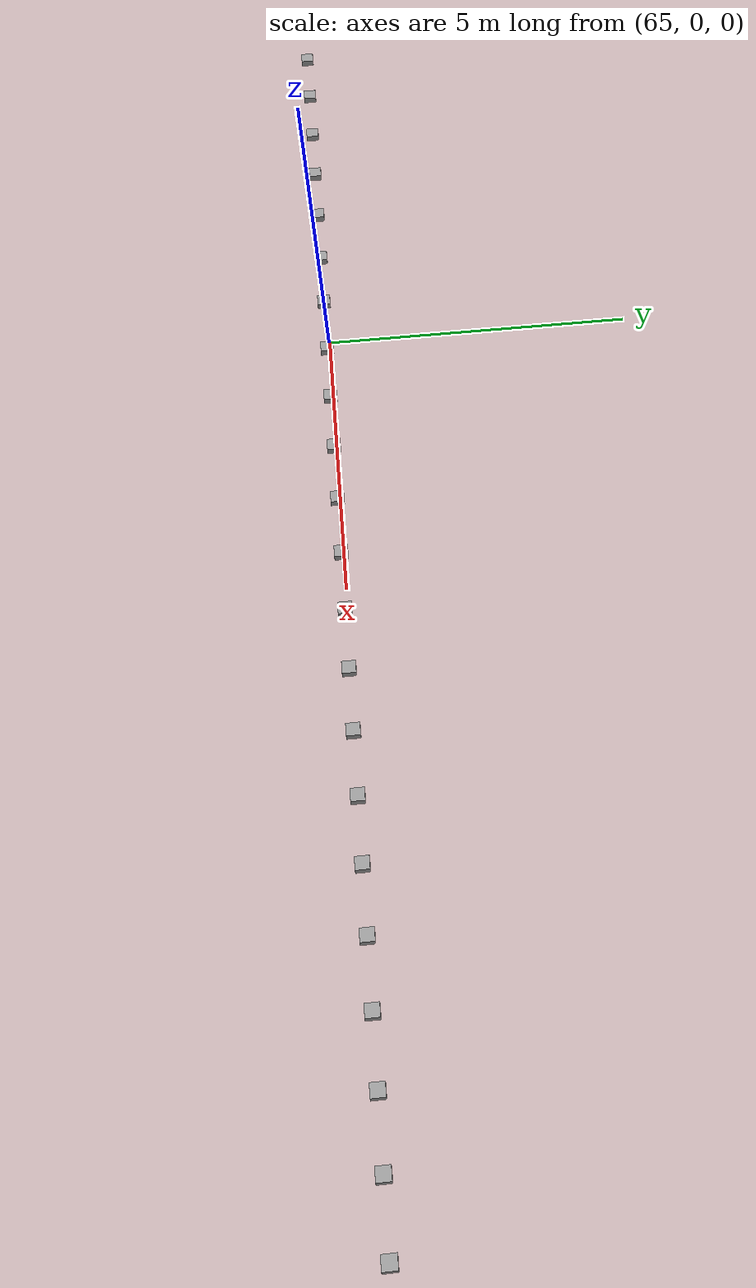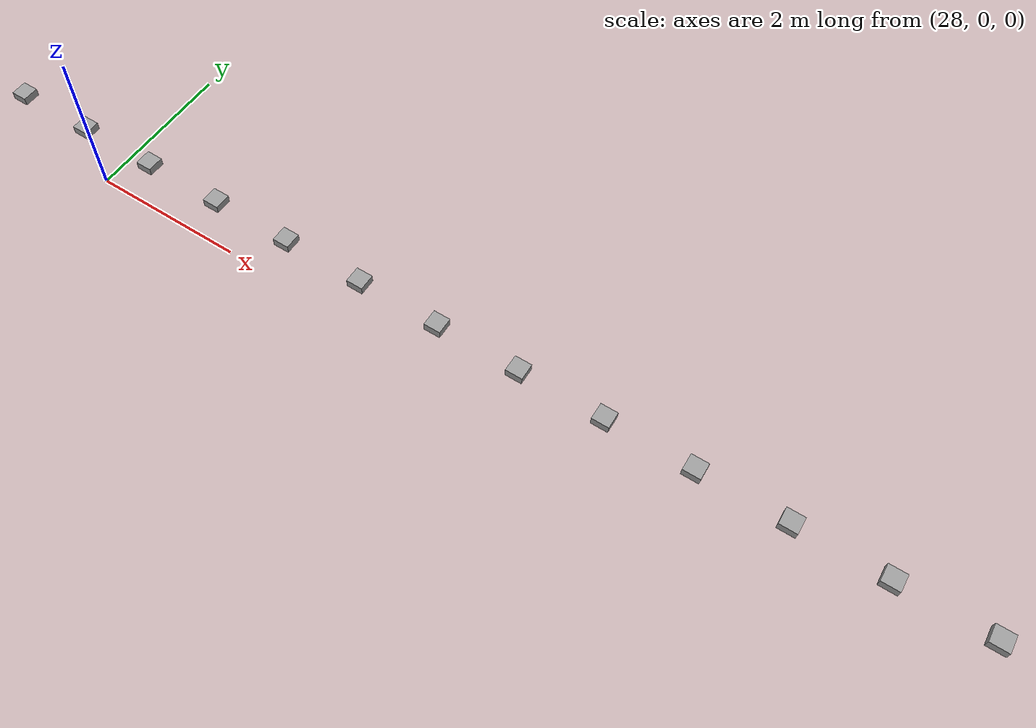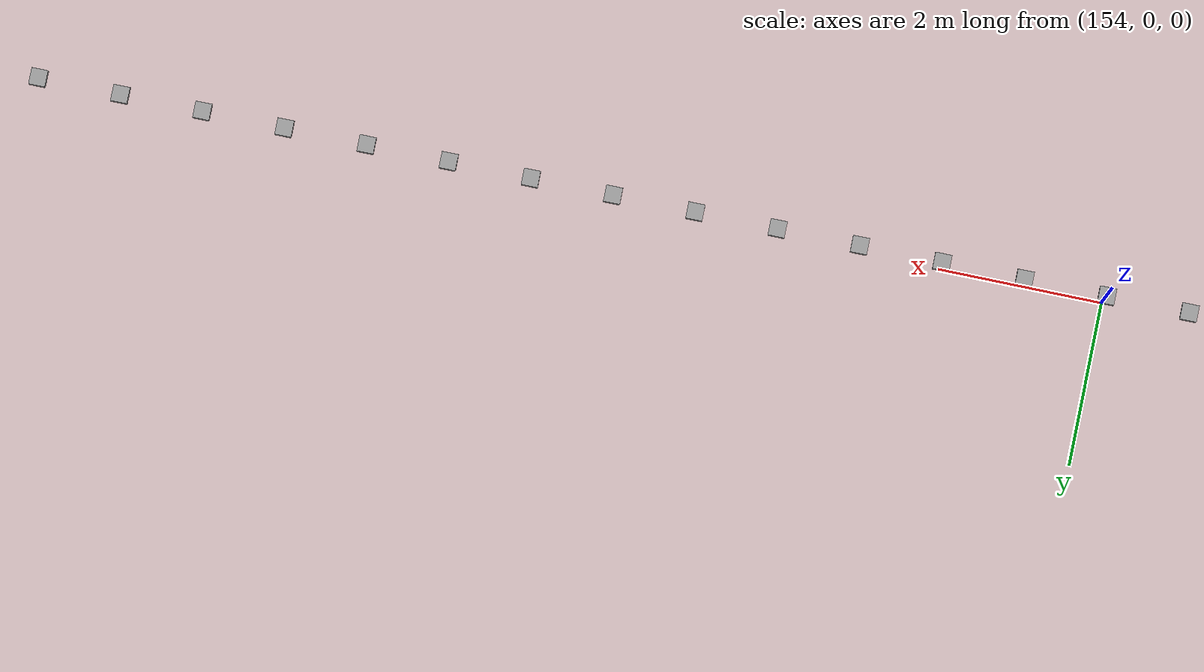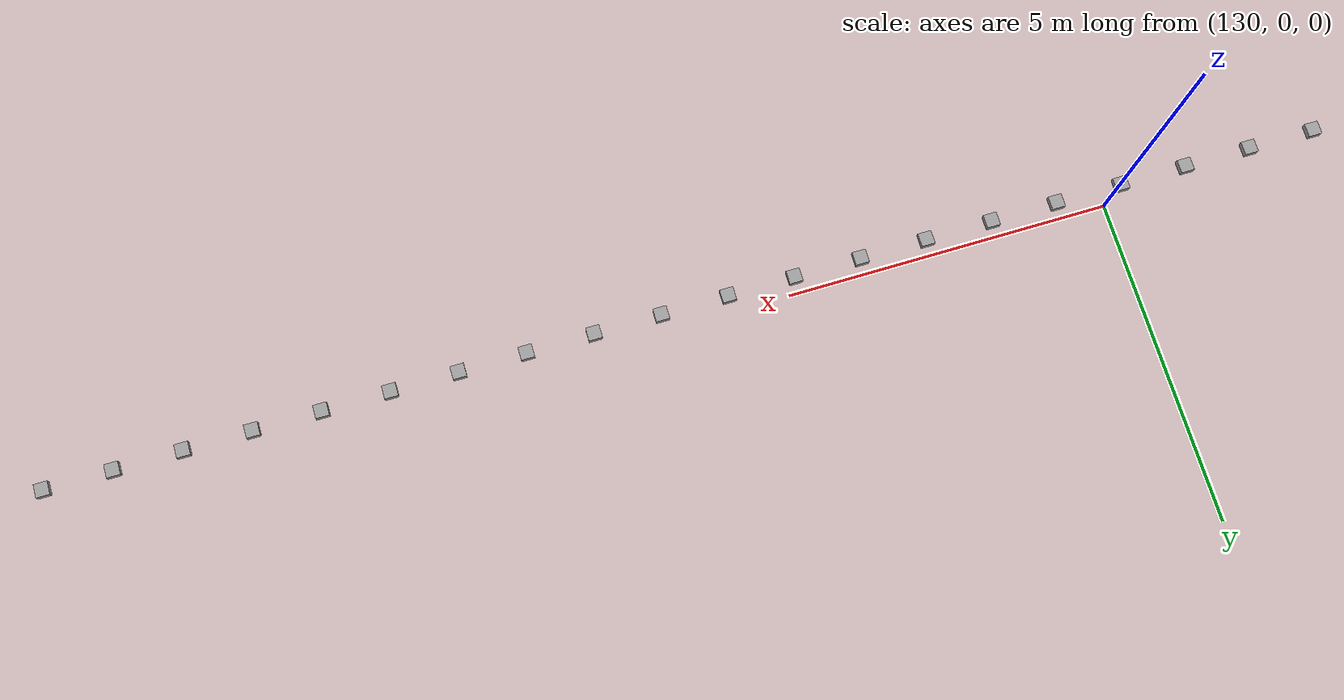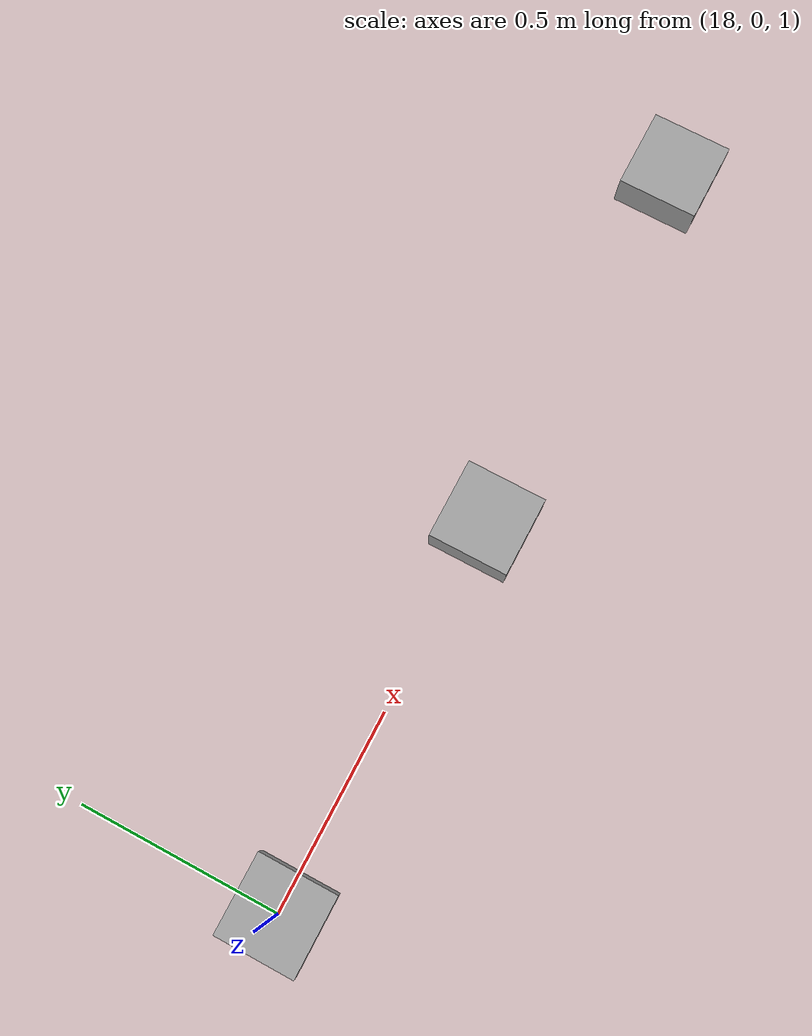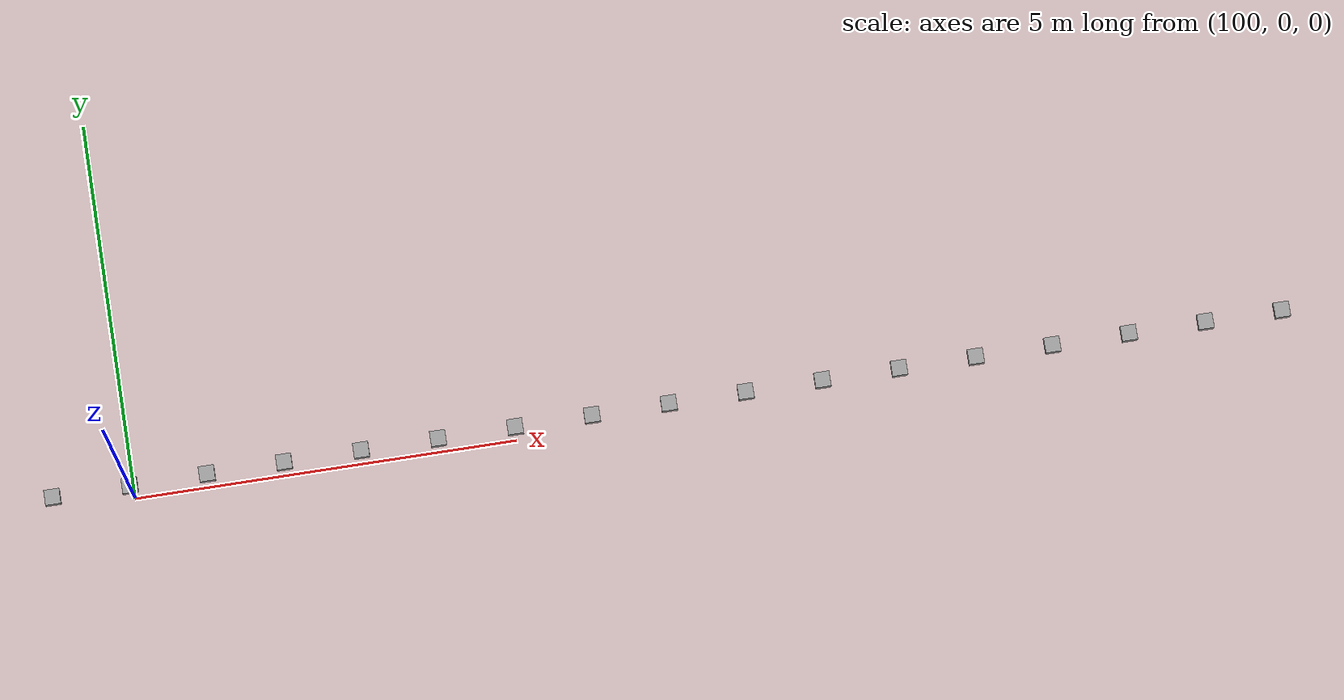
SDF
<?xml version="1.0" ?>

<sdf version="1.5">
  <world name="default">
    <physics type="ode">
      <real_time_update_rate>0.0</real_time_update_rate>
    </physics>
    <!-- A global light source -->
    <include>
      <uri>model://sun</uri>
    </include>

    <model name='box_thruster_0'>
      <link name="box">
        <pose>0 0 1.0  0 0 0</pose>
        <inertial>
          <pose>0 0 0  0 0 0</pose>
          <mass>1.0</mass>
          <inertia>
            <ixx>0.0041666666666666675</ixx>
            <iyy>0.0041666666666666675</iyy>
            <izz>0.006666666666666668</izz>
            <ixy>0</ixy>
            <ixz>0</ixz>
            <iyz>0</iyz>
          </inertia>
        </inertial>
        <collision name="collision">
          <geometry>
            <box>
              <size>0.2 0.2 0.1</size>
            </box>
          </geometry>
        </collision>
        <visual name="visual">
          <geometry>
            <box>
              <size>0.2 0.2 0.1</size>
            </box>
          </geometry>
          <material>
            <script>
              <uri>file://media/materials/scripts/gazebo.material</uri>
              <name>Gazebo/Grey</name>
            </script>
          </material>
        </visual>
      </link>
      <plugin name="box_thruster" filename="libBoxThrusterPlugin.so">
        <angular>3.141592653589793 0 0</angular>
        <linear>0 0 5</linear>
        <thrust_magnitude>12.0</thrust_magnitude>
      </plugin>
    </model>

    <model name='box_thruster_1'>
      <link name="box">
        <pose>1 0 1.0  0 0 0</pose>
        <inertial>
          <pose>0 0 0  0 0 0</pose>
          <mass>1.0</mass>
          <inertia>
            <ixx>0.0041666666666666675</ixx>
            <iyy>0.0041666666666666675</iyy>
            <izz>0.006666666666666668</izz>
            <ixy>0</ixy>
            <ixz>0</ixz>
            <iyz>0</iyz>
          </inertia>
        </inertial>
        <collision name="collision">
          <geometry>
            <box>
              <size>0.2 0.2 0.1</size>
            </box>
          </geometry>
        </collision>
        <visual name="visual">
          <geometry>
            <box>
              <size>0.2 0.2 0.1</size>
            </box>
          </geometry>
          <material>
            <script>
              <uri>file://media/materials/scripts/gazebo.material</uri>
              <name>Gazebo/Grey</name>
            </script>
          </material>
        </visual>
      </link>
      <plugin name="box_thruster" filename="libBoxThrusterPlugin.so">
        <angular>3.141592653589793 0 0</angular>
        <linear>0 0 5</linear>
        <thrust_magnitude>12.0</thrust_magnitude>
      </plugin>
    </model>

    <model name='box_thruster_2'>
      <link name="box">
        <pose>2 0 1.0  0 0 0</pose>
        <inertial>
          <pose>0 0 0  0 0 0</pose>
          <mass>1.0</mass>
          <inertia>
            <ixx>0.0041666666666666675</ixx>
            <iyy>0.0041666666666666675</iyy>
            <izz>0.006666666666666668</izz>
            <ixy>0</ixy>
            <ixz>0</ixz>
            <iyz>0</iyz>
          </inertia>
        </inertial>
        <collision name="collision">
          <geometry>
            <box>
              <size>0.2 0.2 0.1</size>
            </box>
          </geometry>
        </collision>
        <visual name="visual">
          <geometry>
            <box>
              <size>0.2 0.2 0.1</size>
            </box>
          </geometry>
          <material>
            <script>
              <uri>file://media/materials/scripts/gazebo.material</uri>
              <name>Gazebo/Grey</name>
            </script>
          </material>
        </visual>
      </link>
      <plugin name="box_thruster" filename="libBoxThrusterPlugin.so">
        <angular>3.141592653589793 0 0</angular>
        <linear>0 0 5</linear>
        <thrust_magnitude>12.0</thrust_magnitude>
      </plugin>
    </model>

    <model name='box_thruster_3'>
      <link name="box">
        <pose>3 0 1.0  0 0 0</pose>
        <inertial>
          <pose>0 0 0  0 0 0</pose>
          <mass>1.0</mass>
          <inertia>
            <ixx>0.0041666666666666675</ixx>
            <iyy>0.0041666666666666675</iyy>
            <izz>0.006666666666666668</izz>
            <ixy>0</ixy>
            <ixz>0</ixz>
            <iyz>0</iyz>
          </inertia>
        </inertial>
        <collision name="collision">
          <geometry>
            <box>
              <size>0.2 0.2 0.1</size>
            </box>
          </geometry>
        </collision>
        <visual name="visual">
          <geometry>
            <box>
              <size>0.2 0.2 0.1</size>
            </box>
          </geometry>
          <material>
            <script>
              <uri>file://media/materials/scripts/gazebo.material</uri>
              <name>Gazebo/Grey</name>
            </script>
          </material>
        </visual>
      </link>
      <plugin name="box_thruster" filename="libBoxThrusterPlugin.so">
        <angular>3.141592653589793 0 0</angular>
        <linear>0 0 5</linear>
        <thrust_magnitude>12.0</thrust_magnitude>
      </plugin>
    </model>

    <model name='box_thruster_4'>
      <link name="box">
        <pose>4 0 1.0  0 0 0</pose>
        <inertial>
          <pose>0 0 0  0 0 0</pose>
          <mass>1.0</mass>
          <inertia>
            <ixx>0.0041666666666666675</ixx>
            <iyy>0.0041666666666666675</iyy>
            <izz>0.006666666666666668</izz>
            <ixy>0</ixy>
            <ixz>0</ixz>
            <iyz>0</iyz>
          </inertia>
        </inertial>
        <collision name="collision">
          <geometry>
            <box>
              <size>0.2 0.2 0.1</size>
            </box>
          </geometry>
        </collision>
        <visual name="visual">
          <geometry>
            <box>
              <size>0.2 0.2 0.1</size>
            </box>
          </geometry>
          <material>
            <script>
              <uri>file://media/materials/scripts/gazebo.material</uri>
              <name>Gazebo/Grey</name>
            </script>
          </material>
        </visual>
      </link>
      <plugin name="box_thruster" filename="libBoxThrusterPlugin.so">
        <angular>3.141592653589793 0 0</angular>
        <linear>0 0 5</linear>
        <thrust_magnitude>12.0</thrust_magnitude>
      </plugin>
    </model>

    <model name='box_thruster_5'>
      <link name="box">
        <pose>5 0 1.0  0 0 0</pose>
        <inertial>
          <pose>0 0 0  0 0 0</pose>
          <mass>1.0</mass>
          <inertia>
            <ixx>0.0041666666666666675</ixx>
            <iyy>0.0041666666666666675</iyy>
            <izz>0.006666666666666668</izz>
            <ixy>0</ixy>
            <ixz>0</ixz>
            <iyz>0</iyz>
          </inertia>
        </inertial>
        <collision name="collision">
          <geometry>
            <box>
              <size>0.2 0.2 0.1</size>
            </box>
          </geometry>
        </collision>
        <visual name="visual">
          <geometry>
            <box>
              <size>0.2 0.2 0.1</size>
            </box>
          </geometry>
          <material>
            <script>
              <uri>file://media/materials/scripts/gazebo.material</uri>
              <name>Gazebo/Grey</name>
            </script>
          </material>
        </visual>
      </link>
      <plugin name="box_thruster" filename="libBoxThrusterPlugin.so">
        <angular>3.141592653589793 0 0</angular>
        <linear>0 0 5</linear>
        <thrust_magnitude>12.0</thrust_magnitude>
      </plugin>
    </model>

    <model name='box_thruster_6'>
      <link name="box">
        <pose>6 0 1.0  0 0 0</pose>
        <inertial>
          <pose>0 0 0  0 0 0</pose>
          <mass>1.0</mass>
          <inertia>
            <ixx>0.0041666666666666675</ixx>
            <iyy>0.0041666666666666675</iyy>
            <izz>0.006666666666666668</izz>
            <ixy>0</ixy>
            <ixz>0</ixz>
            <iyz>0</iyz>
          </inertia>
        </inertial>
        <collision name="collision">
          <geometry>
            <box>
              <size>0.2 0.2 0.1</size>
            </box>
          </geometry>
        </collision>
        <visual name="visual">
          <geometry>
            <box>
              <size>0.2 0.2 0.1</size>
            </box>
          </geometry>
          <material>
            <script>
              <uri>file://media/materials/scripts/gazebo.material</uri>
              <name>Gazebo/Grey</name>
            </script>
          </material>
        </visual>
      </link>
      <plugin name="box_thruster" filename="libBoxThrusterPlugin.so">
        <angular>3.141592653589793 0 0</angular>
        <linear>0 0 5</linear>
        <thrust_magnitude>12.0</thrust_magnitude>
      </plugin>
    </model>

    <model name='box_thruster_7'>
      <link name="box">
        <pose>7 0 1.0  0 0 0</pose>
        <inertial>
          <pose>0 0 0  0 0 0</pose>
          <mass>1.0</mass>
          <inertia>
            <ixx>0.0041666666666666675</ixx>
            <iyy>0.0041666666666666675</iyy>
            <izz>0.006666666666666668</izz>
            <ixy>0</ixy>
            <ixz>0</ixz>
            <iyz>0</iyz>
          </inertia>
        </inertial>
        <collision name="collision">
          <geometry>
            <box>
              <size>0.2 0.2 0.1</size>
            </box>
          </geometry>
        </collision>
        <visual name="visual">
          <geometry>
            <box>
              <size>0.2 0.2 0.1</size>
            </box>
          </geometry>
          <material>
            <script>
              <uri>file://media/materials/scripts/gazebo.material</uri>
              <name>Gazebo/Grey</name>
            </script>
          </material>
        </visual>
      </link>
      <plugin name="box_thruster" filename="libBoxThrusterPlugin.so">
        <angular>3.141592653589793 0 0</angular>
        <linear>0 0 5</linear>
        <thrust_magnitude>12.0</thrust_magnitude>
      </plugin>
    </model>

    <model name='box_thruster_8'>
      <link name="box">
        <pose>8 0 1.0  0 0 0</pose>
        <inertial>
          <pose>0 0 0  0 0 0</pose>
          <mass>1.0</mass>
          <inertia>
            <ixx>0.0041666666666666675</ixx>
            <iyy>0.0041666666666666675</iyy>
            <izz>0.006666666666666668</izz>
            <ixy>0</ixy>
            <ixz>0</ixz>
            <iyz>0</iyz>
          </inertia>
        </inertial>
        <collision name="collision">
          <geometry>
            <box>
              <size>0.2 0.2 0.1</size>
            </box>
          </geometry>
        </collision>
        <visual name="visual">
          <geometry>
            <box>
              <size>0.2 0.2 0.1</size>
            </box>
          </geometry>
          <material>
            <script>
              <uri>file://media/materials/scripts/gazebo.material</uri>
              <name>Gazebo/Grey</name>
            </script>
          </material>
        </visual>
      </link>
      <plugin name="box_thruster" filename="libBoxThrusterPlugin.so">
        <angular>3.141592653589793 0 0</angular>
        <linear>0 0 5</linear>
        <thrust_magnitude>12.0</thrust_magnitude>
      </plugin>
    </model>

    <model name='box_thruster_9'>
      <link name="box">
        <pose>9 0 1.0  0 0 0</pose>
        <inertial>
          <pose>0 0 0  0 0 0</pose>
          <mass>1.0</mass>
          <inertia>
            <ixx>0.0041666666666666675</ixx>
            <iyy>0.0041666666666666675</iyy>
            <izz>0.006666666666666668</izz>
            <ixy>0</ixy>
            <ixz>0</ixz>
            <iyz>0</iyz>
          </inertia>
        </inertial>
        <collision name="collision">
          <geometry>
            <box>
              <size>0.2 0.2 0.1</size>
            </box>
          </geometry>
        </collision>
        <visual name="visual">
          <geometry>
            <box>
              <size>0.2 0.2 0.1</size>
            </box>
          </geometry>
          <material>
            <script>
              <uri>file://media/materials/scripts/gazebo.material</uri>
              <name>Gazebo/Grey</name>
            </script>
          </material>
        </visual>
      </link>
      <plugin name="box_thruster" filename="libBoxThrusterPlugin.so">
        <angular>3.141592653589793 0 0</angular>
        <linear>0 0 5</linear>
        <thrust_magnitude>12.0</thrust_magnitude>
      </plugin>
    </model>

    <model name='box_thruster_10'>
      <link name="box">
        <pose>10 0 1.0  0 0 0</pose>
        <inertial>
          <pose>0 0 0  0 0 0</pose>
          <mass>1.0</mass>
          <inertia>
            <ixx>0.0041666666666666675</ixx>
            <iyy>0.0041666666666666675</iyy>
            <izz>0.006666666666666668</izz>
            <ixy>0</ixy>
            <ixz>0</ixz>
            <iyz>0</iyz>
          </inertia>
        </inertial>
        <collision name="collision">
          <geometry>
            <box>
              <size>0.2 0.2 0.1</size>
            </box>
          </geometry>
        </collision>
        <visual name="visual">
          <geometry>
            <box>
              <size>0.2 0.2 0.1</size>
            </box>
          </geometry>
          <material>
            <script>
              <uri>file://media/materials/scripts/gazebo.material</uri>
              <name>Gazebo/Grey</name>
            </script>
          </material>
        </visual>
      </link>
      <plugin name="box_thruster" filename="libBoxThrusterPlugin.so">
        <angular>3.141592653589793 0 0</angular>
        <linear>0 0 5</linear>
        <thrust_magnitude>12.0</thrust_magnitude>
      </plugin>
    </model>

    <model name='box_thruster_11'>
      <link name="box">
        <pose>11 0 1.0  0 0 0</pose>
        <inertial>
          <pose>0 0 0  0 0 0</pose>
          <mass>1.0</mass>
          <inertia>
            <ixx>0.0041666666666666675</ixx>
            <iyy>0.0041666666666666675</iyy>
            <izz>0.006666666666666668</izz>
            <ixy>0</ixy>
            <ixz>0</ixz>
            <iyz>0</iyz>
          </inertia>
        </inertial>
        <collision name="collision">
          <geometry>
            <box>
              <size>0.2 0.2 0.1</size>
            </box>
          </geometry>
        </collision>
        <visual name="visual">
          <geometry>
            <box>
              <size>0.2 0.2 0.1</size>
            </box>
          </geometry>
          <material>
            <script>
              <uri>file://media/materials/scripts/gazebo.material</uri>
              <name>Gazebo/Grey</name>
            </script>
          </material>
        </visual>
      </link>
      <plugin name="box_thruster" filename="libBoxThrusterPlugin.so">
        <angular>3.141592653589793 0 0</angular>
        <linear>0 0 5</linear>
        <thrust_magnitude>12.0</thrust_magnitude>
      </plugin>
    </model>

    <model name='box_thruster_12'>
      <link name="box">
        <pose>12 0 1.0  0 0 0</pose>
        <inertial>
          <pose>0 0 0  0 0 0</pose>
          <mass>1.0</mass>
          <inertia>
            <ixx>0.0041666666666666675</ixx>
            <iyy>0.0041666666666666675</iyy>
            <izz>0.006666666666666668</izz>
            <ixy>0</ixy>
            <ixz>0</ixz>
            <iyz>0</iyz>
          </inertia>
        </inertial>
        <collision name="collision">
          <geometry>
            <box>
              <size>0.2 0.2 0.1</size>
            </box>
          </geometry>
        </collision>
        <visual name="visual">
          <geometry>
            <box>
              <size>0.2 0.2 0.1</size>
            </box>
          </geometry>
          <material>
            <script>
              <uri>file://media/materials/scripts/gazebo.material</uri>
              <name>Gazebo/Grey</name>
            </script>
          </material>
        </visual>
      </link>
      <plugin name="box_thruster" filename="libBoxThrusterPlugin.so">
        <angular>3.141592653589793 0 0</angular>
        <linear>0 0 5</linear>
        <thrust_magnitude>12.0</thrust_magnitude>
      </plugin>
    </model>

    <model name='box_thruster_13'>
      <link name="box">
        <pose>13 0 1.0  0 0 0</pose>
        <inertial>
          <pose>0 0 0  0 0 0</pose>
          <mass>1.0</mass>
          <inertia>
            <ixx>0.0041666666666666675</ixx>
            <iyy>0.0041666666666666675</iyy>
            <izz>0.006666666666666668</izz>
            <ixy>0</ixy>
            <ixz>0</ixz>
            <iyz>0</iyz>
          </inertia>
        </inertial>
        <collision name="collision">
          <geometry>
            <box>
              <size>0.2 0.2 0.1</size>
            </box>
          </geometry>
        </collision>
        <visual name="visual">
          <geometry>
            <box>
              <size>0.2 0.2 0.1</size>
            </box>
          </geometry>
          <material>
            <script>
              <uri>file://media/materials/scripts/gazebo.material</uri>
              <name>Gazebo/Grey</name>
            </script>
          </material>
        </visual>
      </link>
      <plugin name="box_thruster" filename="libBoxThrusterPlugin.so">
        <angular>3.141592653589793 0 0</angular>
        <linear>0 0 5</linear>
        <thrust_magnitude>12.0</thrust_magnitude>
      </plugin>
    </model>

    <model name='box_thruster_14'>
      <link name="box">
        <pose>14 0 1.0  0 0 0</pose>
        <inertial>
          <pose>0 0 0  0 0 0</pose>
          <mass>1.0</mass>
          <inertia>
            <ixx>0.0041666666666666675</ixx>
            <iyy>0.0041666666666666675</iyy>
            <izz>0.006666666666666668</izz>
            <ixy>0</ixy>
            <ixz>0</ixz>
            <iyz>0</iyz>
          </inertia>
        </inertial>
        <collision name="collision">
          <geometry>
            <box>
              <size>0.2 0.2 0.1</size>
            </box>
          </geometry>
        </collision>
        <visual name="visual">
          <geometry>
            <box>
              <size>0.2 0.2 0.1</size>
            </box>
          </geometry>
          <material>
            <script>
              <uri>file://media/materials/scripts/gazebo.material</uri>
              <name>Gazebo/Grey</name>
            </script>
          </material>
        </visual>
      </link>
      <plugin name="box_thruster" filename="libBoxThrusterPlugin.so">
        <angular>3.141592653589793 0 0</angular>
        <linear>0 0 5</linear>
        <thrust_magnitude>12.0</thrust_magnitude>
      </plugin>
    </model>

    <model name='box_thruster_15'>
      <link name="box">
        <pose>15 0 1.0  0 0 0</pose>
        <inertial>
          <pose>0 0 0  0 0 0</pose>
          <mass>1.0</mass>
          <inertia>
            <ixx>0.0041666666666666675</ixx>
            <iyy>0.0041666666666666675</iyy>
            <izz>0.006666666666666668</izz>
            <ixy>0</ixy>
            <ixz>0</ixz>
            <iyz>0</iyz>
          </inertia>
        </inertial>
        <collision name="collision">
          <geometry>
            <box>
              <size>0.2 0.2 0.1</size>
            </box>
          </geometry>
        </collision>
        <visual name="visual">
          <geometry>
            <box>
              <size>0.2 0.2 0.1</size>
            </box>
          </geometry>
          <material>
            <script>
              <uri>file://media/materials/scripts/gazebo.material</uri>
              <name>Gazebo/Grey</name>
            </script>
          </material>
        </visual>
      </link>
      <plugin name="box_thruster" filename="libBoxThrusterPlugin.so">
        <angular>3.141592653589793 0 0</angular>
        <linear>0 0 5</linear>
        <thrust_magnitude>12.0</thrust_magnitude>
      </plugin>
    </model>

    <model name='box_thruster_16'>
      <link name="box">
        <pose>16 0 1.0  0 0 0</pose>
        <inertial>
          <pose>0 0 0  0 0 0</pose>
          <mass>1.0</mass>
          <inertia>
            <ixx>0.0041666666666666675</ixx>
            <iyy>0.0041666666666666675</iyy>
            <izz>0.006666666666666668</izz>
            <ixy>0</ixy>
            <ixz>0</ixz>
            <iyz>0</iyz>
          </inertia>
        </inertial>
        <collision name="collision">
          <geometry>
            <box>
              <size>0.2 0.2 0.1</size>
            </box>
          </geometry>
        </collision>
        <visual name="visual">
          <geometry>
            <box>
              <size>0.2 0.2 0.1</size>
            </box>
          </geometry>
          <material>
            <script>
              <uri>file://media/materials/scripts/gazebo.material</uri>
              <name>Gazebo/Grey</name>
            </script>
          </material>
        </visual>
      </link>
      <plugin name="box_thruster" filename="libBoxThrusterPlugin.so">
        <angular>3.141592653589793 0 0</angular>
        <linear>0 0 5</linear>
        <thrust_magnitude>12.0</thrust_magnitude>
      </plugin>
    </model>

    <model name='box_thruster_17'>
      <link name="box">
        <pose>17 0 1.0  0 0 0</pose>
        <inertial>
          <pose>0 0 0  0 0 0</pose>
          <mass>1.0</mass>
          <inertia>
            <ixx>0.0041666666666666675</ixx>
            <iyy>0.0041666666666666675</iyy>
            <izz>0.006666666666666668</izz>
            <ixy>0</ixy>
            <ixz>0</ixz>
            <iyz>0</iyz>
          </inertia>
        </inertial>
        <collision name="collision">
          <geometry>
            <box>
              <size>0.2 0.2 0.1</size>
            </box>
          </geometry>
        </collision>
        <visual name="visual">
          <geometry>
            <box>
              <size>0.2 0.2 0.1</size>
            </box>
          </geometry>
          <material>
            <script>
              <uri>file://media/materials/scripts/gazebo.material</uri>
              <name>Gazebo/Grey</name>
            </script>
          </material>
        </visual>
      </link>
      <plugin name="box_thruster" filename="libBoxThrusterPlugin.so">
        <angular>3.141592653589793 0 0</angular>
        <linear>0 0 5</linear>
        <thrust_magnitude>12.0</thrust_magnitude>
      </plugin>
    </model>

    <model name='box_thruster_18'>
      <link name="box">
        <pose>18 0 1.0  0 0 0</pose>
        <inertial>
          <pose>0 0 0  0 0 0</pose>
          <mass>1.0</mass>
          <inertia>
            <ixx>0.0041666666666666675</ixx>
            <iyy>0.0041666666666666675</iyy>
            <izz>0.006666666666666668</izz>
            <ixy>0</ixy>
            <ixz>0</ixz>
            <iyz>0</iyz>
          </inertia>
        </inertial>
        <collision name="collision">
          <geometry>
            <box>
              <size>0.2 0.2 0.1</size>
            </box>
          </geometry>
        </collision>
        <visual name="visual">
          <geometry>
            <box>
              <size>0.2 0.2 0.1</size>
            </box>
          </geometry>
          <material>
            <script>
              <uri>file://media/materials/scripts/gazebo.material</uri>
              <name>Gazebo/Grey</name>
            </script>
          </material>
        </visual>
      </link>
      <plugin name="box_thruster" filename="libBoxThrusterPlugin.so">
        <angular>3.141592653589793 0 0</angular>
        <linear>0 0 5</linear>
        <thrust_magnitude>12.0</thrust_magnitude>
      </plugin>
    </model>

    <model name='box_thruster_19'>
      <link name="box">
        <pose>19 0 1.0  0 0 0</pose>
        <inertial>
          <pose>0 0 0  0 0 0</pose>
          <mass>1.0</mass>
          <inertia>
            <ixx>0.0041666666666666675</ixx>
            <iyy>0.0041666666666666675</iyy>
            <izz>0.006666666666666668</izz>
            <ixy>0</ixy>
            <ixz>0</ixz>
            <iyz>0</iyz>
          </inertia>
        </inertial>
        <collision name="collision">
          <geometry>
            <box>
              <size>0.2 0.2 0.1</size>
            </box>
          </geometry>
        </collision>
        <visual name="visual">
          <geometry>
            <box>
              <size>0.2 0.2 0.1</size>
            </box>
          </geometry>
          <material>
            <script>
              <uri>file://media/materials/scripts/gazebo.material</uri>
              <name>Gazebo/Grey</name>
            </script>
          </material>
        </visual>
      </link>
      <plugin name="box_thruster" filename="libBoxThrusterPlugin.so">
        <angular>3.141592653589793 0 0</angular>
        <linear>0 0 5</linear>
        <thrust_magnitude>12.0</thrust_magnitude>
      </plugin>
    </model>

    <model name='box_thruster_20'>
      <link name="box">
        <pose>20 0 1.0  0 0 0</pose>
        <inertial>
          <pose>0 0 0  0 0 0</pose>
          <mass>1.0</mass>
          <inertia>
            <ixx>0.0041666666666666675</ixx>
            <iyy>0.0041666666666666675</iyy>
            <izz>0.006666666666666668</izz>
            <ixy>0</ixy>
            <ixz>0</ixz>
            <iyz>0</iyz>
          </inertia>
        </inertial>
        <collision name="collision">
          <geometry>
            <box>
              <size>0.2 0.2 0.1</size>
            </box>
          </geometry>
        </collision>
        <visual name="visual">
          <geometry>
            <box>
              <size>0.2 0.2 0.1</size>
            </box>
          </geometry>
          <material>
            <script>
              <uri>file://media/materials/scripts/gazebo.material</uri>
              <name>Gazebo/Grey</name>
            </script>
          </material>
        </visual>
      </link>
      <plugin name="box_thruster" filename="libBoxThrusterPlugin.so">
        <angular>3.141592653589793 0 0</angular>
        <linear>0 0 5</linear>
        <thrust_magnitude>12.0</thrust_magnitude>
      </plugin>
    </model>

    <model name='box_thruster_21'>
      <link name="box">
        <pose>21 0 1.0  0 0 0</pose>
        <inertial>
          <pose>0 0 0  0 0 0</pose>
          <mass>1.0</mass>
          <inertia>
            <ixx>0.0041666666666666675</ixx>
            <iyy>0.0041666666666666675</iyy>
            <izz>0.006666666666666668</izz>
            <ixy>0</ixy>
            <ixz>0</ixz>
            <iyz>0</iyz>
          </inertia>
        </inertial>
        <collision name="collision">
          <geometry>
            <box>
              <size>0.2 0.2 0.1</size>
            </box>
          </geometry>
        </collision>
        <visual name="visual">
          <geometry>
            <box>
              <size>0.2 0.2 0.1</size>
            </box>
          </geometry>
          <material>
            <script>
              <uri>file://media/materials/scripts/gazebo.material</uri>
              <name>Gazebo/Grey</name>
            </script>
          </material>
        </visual>
      </link>
      <plugin name="box_thruster" filename="libBoxThrusterPlugin.so">
        <angular>3.141592653589793 0 0</angular>
        <linear>0 0 5</linear>
        <thrust_magnitude>12.0</thrust_magnitude>
      </plugin>
    </model>

    <model name='box_thruster_22'>
      <link name="box">
        <pose>22 0 1.0  0 0 0</pose>
        <inertial>
          <pose>0 0 0  0 0 0</pose>
          <mass>1.0</mass>
          <inertia>
            <ixx>0.0041666666666666675</ixx>
            <iyy>0.0041666666666666675</iyy>
            <izz>0.006666666666666668</izz>
            <ixy>0</ixy>
            <ixz>0</ixz>
            <iyz>0</iyz>
          </inertia>
        </inertial>
        <collision name="collision">
          <geometry>
            <box>
              <size>0.2 0.2 0.1</size>
            </box>
          </geometry>
        </collision>
        <visual name="visual">
          <geometry>
            <box>
              <size>0.2 0.2 0.1</size>
            </box>
          </geometry>
          <material>
            <script>
              <uri>file://media/materials/scripts/gazebo.material</uri>
              <name>Gazebo/Grey</name>
            </script>
          </material>
        </visual>
      </link>
      <plugin name="box_thruster" filename="libBoxThrusterPlugin.so">
        <angular>3.141592653589793 0 0</angular>
        <linear>0 0 5</linear>
        <thrust_magnitude>12.0</thrust_magnitude>
      </plugin>
    </model>

    <model name='box_thruster_23'>
      <link name="box">
        <pose>23 0 1.0  0 0 0</pose>
        <inertial>
          <pose>0 0 0  0 0 0</pose>
          <mass>1.0</mass>
          <inertia>
            <ixx>0.0041666666666666675</ixx>
            <iyy>0.0041666666666666675</iyy>
            <izz>0.006666666666666668</izz>
            <ixy>0</ixy>
            <ixz>0</ixz>
            <iyz>0</iyz>
          </inertia>
        </inertial>
        <collision name="collision">
          <geometry>
            <box>
              <size>0.2 0.2 0.1</size>
            </box>
          </geometry>
        </collision>
        <visual name="visual">
          <geometry>
            <box>
              <size>0.2 0.2 0.1</size>
            </box>
          </geometry>
          <material>
            <script>
              <uri>file://media/materials/scripts/gazebo.material</uri>
              <name>Gazebo/Grey</name>
            </script>
          </material>
        </visual>
      </link>
      <plugin name="box_thruster" filename="libBoxThrusterPlugin.so">
        <angular>3.141592653589793 0 0</angular>
        <linear>0 0 5</linear>
        <thrust_magnitude>12.0</thrust_magnitude>
      </plugin>
    </model>

    <model name='box_thruster_24'>
      <link name="box">
        <pose>24 0 1.0  0 0 0</pose>
        <inertial>
          <pose>0 0 0  0 0 0</pose>
          <mass>1.0</mass>
          <inertia>
            <ixx>0.0041666666666666675</ixx>
            <iyy>0.0041666666666666675</iyy>
            <izz>0.006666666666666668</izz>
            <ixy>0</ixy>
            <ixz>0</ixz>
            <iyz>0</iyz>
          </inertia>
        </inertial>
        <collision name="collision">
          <geometry>
            <box>
              <size>0.2 0.2 0.1</size>
            </box>
          </geometry>
        </collision>
        <visual name="visual">
          <geometry>
            <box>
              <size>0.2 0.2 0.1</size>
            </box>
          </geometry>
          <material>
            <script>
              <uri>file://media/materials/scripts/gazebo.material</uri>
              <name>Gazebo/Grey</name>
            </script>
          </material>
        </visual>
      </link>
      <plugin name="box_thruster" filename="libBoxThrusterPlugin.so">
        <angular>3.141592653589793 0 0</angular>
        <linear>0 0 5</linear>
        <thrust_magnitude>12.0</thrust_magnitude>
      </plugin>
    </model>

    <model name='box_thruster_25'>
      <link name="box">
        <pose>25 0 1.0  0 0 0</pose>
        <inertial>
          <pose>0 0 0  0 0 0</pose>
          <mass>1.0</mass>
          <inertia>
            <ixx>0.0041666666666666675</ixx>
            <iyy>0.0041666666666666675</iyy>
            <izz>0.006666666666666668</izz>
            <ixy>0</ixy>
            <ixz>0</ixz>
            <iyz>0</iyz>
          </inertia>
        </inertial>
        <collision name="collision">
          <geometry>
            <box>
              <size>0.2 0.2 0.1</size>
            </box>
          </geometry>
        </collision>
        <visual name="visual">
          <geometry>
            <box>
              <size>0.2 0.2 0.1</size>
            </box>
          </geometry>
          <material>
            <script>
              <uri>file://media/materials/scripts/gazebo.material</uri>
              <name>Gazebo/Grey</name>
            </script>
          </material>
        </visual>
      </link>
      <plugin name="box_thruster" filename="libBoxThrusterPlugin.so">
        <angular>3.141592653589793 0 0</angular>
        <linear>0 0 5</linear>
        <thrust_magnitude>12.0</thrust_magnitude>
      </plugin>
    </model>

    <model name='box_thruster_26'>
      <link name="box">
        <pose>26 0 1.0  0 0 0</pose>
        <inertial>
          <pose>0 0 0  0 0 0</pose>
          <mass>1.0</mass>
          <inertia>
            <ixx>0.0041666666666666675</ixx>
            <iyy>0.0041666666666666675</iyy>
            <izz>0.006666666666666668</izz>
            <ixy>0</ixy>
            <ixz>0</ixz>
            <iyz>0</iyz>
          </inertia>
        </inertial>
        <collision name="collision">
          <geometry>
            <box>
              <size>0.2 0.2 0.1</size>
            </box>
          </geometry>
        </collision>
        <visual name="visual">
          <geometry>
            <box>
              <size>0.2 0.2 0.1</size>
            </box>
          </geometry>
          <material>
            <script>
              <uri>file://media/materials/scripts/gazebo.material</uri>
              <name>Gazebo/Grey</name>
            </script>
          </material>
        </visual>
      </link>
      <plugin name="box_thruster" filename="libBoxThrusterPlugin.so">
        <angular>3.141592653589793 0 0</angular>
        <linear>0 0 5</linear>
        <thrust_magnitude>12.0</thrust_magnitude>
      </plugin>
    </model>

    <model name='box_thruster_27'>
      <link name="box">
        <pose>27 0 1.0  0 0 0</pose>
        <inertial>
          <pose>0 0 0  0 0 0</pose>
          <mass>1.0</mass>
          <inertia>
            <ixx>0.0041666666666666675</ixx>
            <iyy>0.0041666666666666675</iyy>
            <izz>0.006666666666666668</izz>
            <ixy>0</ixy>
            <ixz>0</ixz>
            <iyz>0</iyz>
          </inertia>
        </inertial>
        <collision name="collision">
          <geometry>
            <box>
              <size>0.2 0.2 0.1</size>
            </box>
          </geometry>
        </collision>
        <visual name="visual">
          <geometry>
            <box>
              <size>0.2 0.2 0.1</size>
            </box>
          </geometry>
          <material>
            <script>
              <uri>file://media/materials/scripts/gazebo.material</uri>
              <name>Gazebo/Grey</name>
            </script>
          </material>
        </visual>
      </link>
      <plugin name="box_thruster" filename="libBoxThrusterPlugin.so">
        <angular>3.141592653589793 0 0</angular>
        <linear>0 0 5</linear>
        <thrust_magnitude>12.0</thrust_magnitude>
      </plugin>
    </model>

    <model name='box_thruster_28'>
      <link name="box">
        <pose>28 0 1.0  0 0 0</pose>
        <inertial>
          <pose>0 0 0  0 0 0</pose>
          <mass>1.0</mass>
          <inertia>
            <ixx>0.0041666666666666675</ixx>
            <iyy>0.0041666666666666675</iyy>
            <izz>0.006666666666666668</izz>
            <ixy>0</ixy>
            <ixz>0</ixz>
            <iyz>0</iyz>
          </inertia>
        </inertial>
        <collision name="collision">
          <geometry>
            <box>
              <size>0.2 0.2 0.1</size>
            </box>
          </geometry>
        </collision>
        <visual name="visual">
          <geometry>
            <box>
              <size>0.2 0.2 0.1</size>
            </box>
          </geometry>
          <material>
            <script>
              <uri>file://media/materials/scripts/gazebo.material</uri>
              <name>Gazebo/Grey</name>
            </script>
          </material>
        </visual>
      </link>
      <plugin name="box_thruster" filename="libBoxThrusterPlugin.so">
        <angular>3.141592653589793 0 0</angular>
        <linear>0 0 5</linear>
        <thrust_magnitude>12.0</thrust_magnitude>
      </plugin>
    </model>

    <model name='box_thruster_29'>
      <link name="box">
        <pose>29 0 1.0  0 0 0</pose>
        <inertial>
          <pose>0 0 0  0 0 0</pose>
          <mass>1.0</mass>
          <inertia>
            <ixx>0.0041666666666666675</ixx>
            <iyy>0.0041666666666666675</iyy>
            <izz>0.006666666666666668</izz>
            <ixy>0</ixy>
            <ixz>0</ixz>
            <iyz>0</iyz>
          </inertia>
        </inertial>
        <collision name="collision">
          <geometry>
            <box>
              <size>0.2 0.2 0.1</size>
            </box>
          </geometry>
        </collision>
        <visual name="visual">
          <geometry>
            <box>
              <size>0.2 0.2 0.1</size>
            </box>
          </geometry>
          <material>
            <script>
              <uri>file://media/materials/scripts/gazebo.material</uri>
              <name>Gazebo/Grey</name>
            </script>
          </material>
        </visual>
      </link>
      <plugin name="box_thruster" filename="libBoxThrusterPlugin.so">
        <angular>3.141592653589793 0 0</angular>
        <linear>0 0 5</linear>
        <thrust_magnitude>12.0</thrust_magnitude>
      </plugin>
    </model>

    <model name='box_thruster_30'>
      <link name="box">
        <pose>30 0 1.0  0 0 0</pose>
        <inertial>
          <pose>0 0 0  0 0 0</pose>
          <mass>1.0</mass>
          <inertia>
            <ixx>0.0041666666666666675</ixx>
            <iyy>0.0041666666666666675</iyy>
            <izz>0.006666666666666668</izz>
            <ixy>0</ixy>
            <ixz>0</ixz>
            <iyz>0</iyz>
          </inertia>
        </inertial>
        <collision name="collision">
          <geometry>
            <box>
              <size>0.2 0.2 0.1</size>
            </box>
          </geometry>
        </collision>
        <visual name="visual">
          <geometry>
            <box>
              <size>0.2 0.2 0.1</size>
            </box>
          </geometry>
          <material>
            <script>
              <uri>file://media/materials/scripts/gazebo.material</uri>
              <name>Gazebo/Grey</name>
            </script>
          </material>
        </visual>
      </link>
      <plugin name="box_thruster" filename="libBoxThrusterPlugin.so">
        <angular>3.141592653589793 0 0</angular>
        <linear>0 0 5</linear>
        <thrust_magnitude>12.0</thrust_magnitude>
      </plugin>
    </model>

    <model name='box_thruster_31'>
      <link name="box">
        <pose>31 0 1.0  0 0 0</pose>
        <inertial>
          <pose>0 0 0  0 0 0</pose>
          <mass>1.0</mass>
          <inertia>
            <ixx>0.0041666666666666675</ixx>
            <iyy>0.0041666666666666675</iyy>
            <izz>0.006666666666666668</izz>
            <ixy>0</ixy>
            <ixz>0</ixz>
            <iyz>0</iyz>
          </inertia>
        </inertial>
        <collision name="collision">
          <geometry>
            <box>
              <size>0.2 0.2 0.1</size>
            </box>
          </geometry>
        </collision>
        <visual name="visual">
          <geometry>
            <box>
              <size>0.2 0.2 0.1</size>
            </box>
          </geometry>
          <material>
            <script>
              <uri>file://media/materials/scripts/gazebo.material</uri>
              <name>Gazebo/Grey</name>
            </script>
          </material>
        </visual>
      </link>
      <plugin name="box_thruster" filename="libBoxThrusterPlugin.so">
        <angular>3.141592653589793 0 0</angular>
        <linear>0 0 5</linear>
        <thrust_magnitude>12.0</thrust_magnitude>
      </plugin>
    </model>

    <model name='box_thruster_32'>
      <link name="box">
        <pose>32 0 1.0  0 0 0</pose>
        <inertial>
          <pose>0 0 0  0 0 0</pose>
          <mass>1.0</mass>
          <inertia>
            <ixx>0.0041666666666666675</ixx>
            <iyy>0.0041666666666666675</iyy>
            <izz>0.006666666666666668</izz>
            <ixy>0</ixy>
            <ixz>0</ixz>
            <iyz>0</iyz>
          </inertia>
        </inertial>
        <collision name="collision">
          <geometry>
            <box>
              <size>0.2 0.2 0.1</size>
            </box>
          </geometry>
        </collision>
        <visual name="visual">
          <geometry>
            <box>
              <size>0.2 0.2 0.1</size>
            </box>
          </geometry>
          <material>
            <script>
              <uri>file://media/materials/scripts/gazebo.material</uri>
              <name>Gazebo/Grey</name>
            </script>
          </material>
        </visual>
      </link>
      <plugin name="box_thruster" filename="libBoxThrusterPlugin.so">
        <angular>3.141592653589793 0 0</angular>
        <linear>0 0 5</linear>
        <thrust_magnitude>12.0</thrust_magnitude>
      </plugin>
    </model>

    <model name='box_thruster_33'>
      <link name="box">
        <pose>33 0 1.0  0 0 0</pose>
        <inertial>
          <pose>0 0 0  0 0 0</pose>
          <mass>1.0</mass>
          <inertia>
            <ixx>0.0041666666666666675</ixx>
            <iyy>0.0041666666666666675</iyy>
            <izz>0.006666666666666668</izz>
            <ixy>0</ixy>
            <ixz>0</ixz>
            <iyz>0</iyz>
          </inertia>
        </inertial>
        <collision name="collision">
          <geometry>
            <box>
              <size>0.2 0.2 0.1</size>
            </box>
          </geometry>
        </collision>
        <visual name="visual">
          <geometry>
            <box>
              <size>0.2 0.2 0.1</size>
            </box>
          </geometry>
          <material>
            <script>
              <uri>file://media/materials/scripts/gazebo.material</uri>
              <name>Gazebo/Grey</name>
            </script>
          </material>
        </visual>
      </link>
      <plugin name="box_thruster" filename="libBoxThrusterPlugin.so">
        <angular>3.141592653589793 0 0</angular>
        <linear>0 0 5</linear>
        <thrust_magnitude>12.0</thrust_magnitude>
      </plugin>
    </model>

    <model name='box_thruster_34'>
      <link name="box">
        <pose>34 0 1.0  0 0 0</pose>
        <inertial>
          <pose>0 0 0  0 0 0</pose>
          <mass>1.0</mass>
          <inertia>
            <ixx>0.0041666666666666675</ixx>
            <iyy>0.0041666666666666675</iyy>
            <izz>0.006666666666666668</izz>
            <ixy>0</ixy>
            <ixz>0</ixz>
            <iyz>0</iyz>
          </inertia>
        </inertial>
        <collision name="collision">
          <geometry>
            <box>
              <size>0.2 0.2 0.1</size>
            </box>
          </geometry>
        </collision>
        <visual name="visual">
          <geometry>
            <box>
              <size>0.2 0.2 0.1</size>
            </box>
          </geometry>
          <material>
            <script>
              <uri>file://media/materials/scripts/gazebo.material</uri>
              <name>Gazebo/Grey</name>
            </script>
          </material>
        </visual>
      </link>
      <plugin name="box_thruster" filename="libBoxThrusterPlugin.so">
        <angular>3.141592653589793 0 0</angular>
        <linear>0 0 5</linear>
        <thrust_magnitude>12.0</thrust_magnitude>
      </plugin>
    </model>

    <model name='box_thruster_35'>
      <link name="box">
        <pose>35 0 1.0  0 0 0</pose>
        <inertial>
          <pose>0 0 0  0 0 0</pose>
          <mass>1.0</mass>
          <inertia>
            <ixx>0.0041666666666666675</ixx>
            <iyy>0.0041666666666666675</iyy>
            <izz>0.006666666666666668</izz>
            <ixy>0</ixy>
            <ixz>0</ixz>
            <iyz>0</iyz>
          </inertia>
        </inertial>
        <collision name="collision">
          <geometry>
            <box>
              <size>0.2 0.2 0.1</size>
            </box>
          </geometry>
        </collision>
        <visual name="visual">
          <geometry>
            <box>
              <size>0.2 0.2 0.1</size>
            </box>
          </geometry>
          <material>
            <script>
              <uri>file://media/materials/scripts/gazebo.material</uri>
              <name>Gazebo/Grey</name>
            </script>
          </material>
        </visual>
      </link>
      <plugin name="box_thruster" filename="libBoxThrusterPlugin.so">
        <angular>3.141592653589793 0 0</angular>
        <linear>0 0 5</linear>
        <thrust_magnitude>12.0</thrust_magnitude>
      </plugin>
    </model>

    <model name='box_thruster_36'>
      <link name="box">
        <pose>36 0 1.0  0 0 0</pose>
        <inertial>
          <pose>0 0 0  0 0 0</pose>
          <mass>1.0</mass>
          <inertia>
            <ixx>0.0041666666666666675</ixx>
            <iyy>0.0041666666666666675</iyy>
            <izz>0.006666666666666668</izz>
            <ixy>0</ixy>
            <ixz>0</ixz>
            <iyz>0</iyz>
          </inertia>
        </inertial>
        <collision name="collision">
          <geometry>
            <box>
              <size>0.2 0.2 0.1</size>
            </box>
          </geometry>
        </collision>
        <visual name="visual">
          <geometry>
            <box>
              <size>0.2 0.2 0.1</size>
            </box>
          </geometry>
          <material>
            <script>
              <uri>file://media/materials/scripts/gazebo.material</uri>
              <name>Gazebo/Grey</name>
            </script>
          </material>
        </visual>
      </link>
      <plugin name="box_thruster" filename="libBoxThrusterPlugin.so">
        <angular>3.141592653589793 0 0</angular>
        <linear>0 0 5</linear>
        <thrust_magnitude>12.0</thrust_magnitude>
      </plugin>
    </model>

    <model name='box_thruster_37'>
      <link name="box">
        <pose>37 0 1.0  0 0 0</pose>
        <inertial>
          <pose>0 0 0  0 0 0</pose>
          <mass>1.0</mass>
          <inertia>
            <ixx>0.0041666666666666675</ixx>
            <iyy>0.0041666666666666675</iyy>
            <izz>0.006666666666666668</izz>
            <ixy>0</ixy>
            <ixz>0</ixz>
            <iyz>0</iyz>
          </inertia>
        </inertial>
        <collision name="collision">
          <geometry>
            <box>
              <size>0.2 0.2 0.1</size>
            </box>
          </geometry>
        </collision>
        <visual name="visual">
          <geometry>
            <box>
              <size>0.2 0.2 0.1</size>
            </box>
          </geometry>
          <material>
            <script>
              <uri>file://media/materials/scripts/gazebo.material</uri>
              <name>Gazebo/Grey</name>
            </script>
          </material>
        </visual>
      </link>
      <plugin name="box_thruster" filename="libBoxThrusterPlugin.so">
        <angular>3.141592653589793 0 0</angular>
        <linear>0 0 5</linear>
        <thrust_magnitude>12.0</thrust_magnitude>
      </plugin>
    </model>

    <model name='box_thruster_38'>
      <link name="box">
        <pose>38 0 1.0  0 0 0</pose>
        <inertial>
          <pose>0 0 0  0 0 0</pose>
          <mass>1.0</mass>
          <inertia>
            <ixx>0.0041666666666666675</ixx>
            <iyy>0.0041666666666666675</iyy>
            <izz>0.006666666666666668</izz>
            <ixy>0</ixy>
            <ixz>0</ixz>
            <iyz>0</iyz>
          </inertia>
        </inertial>
        <collision name="collision">
          <geometry>
            <box>
              <size>0.2 0.2 0.1</size>
            </box>
          </geometry>
        </collision>
        <visual name="visual">
          <geometry>
            <box>
              <size>0.2 0.2 0.1</size>
            </box>
          </geometry>
          <material>
            <script>
              <uri>file://media/materials/scripts/gazebo.material</uri>
              <name>Gazebo/Grey</name>
            </script>
          </material>
        </visual>
      </link>
      <plugin name="box_thruster" filename="libBoxThrusterPlugin.so">
        <angular>3.141592653589793 0 0</angular>
        <linear>0 0 5</linear>
        <thrust_magnitude>12.0</thrust_magnitude>
      </plugin>
    </model>

    <model name='box_thruster_39'>
      <link name="box">
        <pose>39 0 1.0  0 0 0</pose>
        <inertial>
          <pose>0 0 0  0 0 0</pose>
          <mass>1.0</mass>
          <inertia>
            <ixx>0.0041666666666666675</ixx>
            <iyy>0.0041666666666666675</iyy>
            <izz>0.006666666666666668</izz>
            <ixy>0</ixy>
            <ixz>0</ixz>
            <iyz>0</iyz>
          </inertia>
        </inertial>
        <collision name="collision">
          <geometry>
            <box>
              <size>0.2 0.2 0.1</size>
            </box>
          </geometry>
        </collision>
        <visual name="visual">
          <geometry>
            <box>
              <size>0.2 0.2 0.1</size>
            </box>
          </geometry>
          <material>
            <script>
              <uri>file://media/materials/scripts/gazebo.material</uri>
              <name>Gazebo/Grey</name>
            </script>
          </material>
        </visual>
      </link>
      <plugin name="box_thruster" filename="libBoxThrusterPlugin.so">
        <angular>3.141592653589793 0 0</angular>
        <linear>0 0 5</linear>
        <thrust_magnitude>12.0</thrust_magnitude>
      </plugin>
    </model>

    <model name='box_thruster_40'>
      <link name="box">
        <pose>40 0 1.0  0 0 0</pose>
        <inertial>
          <pose>0 0 0  0 0 0</pose>
          <mass>1.0</mass>
          <inertia>
            <ixx>0.0041666666666666675</ixx>
            <iyy>0.0041666666666666675</iyy>
            <izz>0.006666666666666668</izz>
            <ixy>0</ixy>
            <ixz>0</ixz>
            <iyz>0</iyz>
          </inertia>
        </inertial>
        <collision name="collision">
          <geometry>
            <box>
              <size>0.2 0.2 0.1</size>
            </box>
          </geometry>
        </collision>
        <visual name="visual">
          <geometry>
            <box>
              <size>0.2 0.2 0.1</size>
            </box>
          </geometry>
          <material>
            <script>
              <uri>file://media/materials/scripts/gazebo.material</uri>
              <name>Gazebo/Grey</name>
            </script>
          </material>
        </visual>
      </link>
      <plugin name="box_thruster" filename="libBoxThrusterPlugin.so">
        <angular>3.141592653589793 0 0</angular>
        <linear>0 0 5</linear>
        <thrust_magnitude>12.0</thrust_magnitude>
      </plugin>
    </model>

    <model name='box_thruster_41'>
      <link name="box">
        <pose>41 0 1.0  0 0 0</pose>
        <inertial>
          <pose>0 0 0  0 0 0</pose>
          <mass>1.0</mass>
          <inertia>
            <ixx>0.0041666666666666675</ixx>
            <iyy>0.0041666666666666675</iyy>
            <izz>0.006666666666666668</izz>
            <ixy>0</ixy>
            <ixz>0</ixz>
            <iyz>0</iyz>
          </inertia>
        </inertial>
        <collision name="collision">
          <geometry>
            <box>
              <size>0.2 0.2 0.1</size>
            </box>
          </geometry>
        </collision>
        <visual name="visual">
          <geometry>
            <box>
              <size>0.2 0.2 0.1</size>
            </box>
          </geometry>
          <material>
            <script>
              <uri>file://media/materials/scripts/gazebo.material</uri>
              <name>Gazebo/Grey</name>
            </script>
          </material>
        </visual>
      </link>
      <plugin name="box_thruster" filename="libBoxThrusterPlugin.so">
        <angular>3.141592653589793 0 0</angular>
        <linear>0 0 5</linear>
        <thrust_magnitude>12.0</thrust_magnitude>
      </plugin>
    </model>

    <model name='box_thruster_42'>
      <link name="box">
        <pose>42 0 1.0  0 0 0</pose>
        <inertial>
          <pose>0 0 0  0 0 0</pose>
          <mass>1.0</mass>
          <inertia>
            <ixx>0.0041666666666666675</ixx>
            <iyy>0.0041666666666666675</iyy>
            <izz>0.006666666666666668</izz>
            <ixy>0</ixy>
            <ixz>0</ixz>
            <iyz>0</iyz>
          </inertia>
        </inertial>
        <collision name="collision">
          <geometry>
            <box>
              <size>0.2 0.2 0.1</size>
            </box>
          </geometry>
        </collision>
        <visual name="visual">
          <geometry>
            <box>
              <size>0.2 0.2 0.1</size>
            </box>
          </geometry>
          <material>
            <script>
              <uri>file://media/materials/scripts/gazebo.material</uri>
              <name>Gazebo/Grey</name>
            </script>
          </material>
        </visual>
      </link>
      <plugin name="box_thruster" filename="libBoxThrusterPlugin.so">
        <angular>3.141592653589793 0 0</angular>
        <linear>0 0 5</linear>
        <thrust_magnitude>12.0</thrust_magnitude>
      </plugin>
    </model>

    <model name='box_thruster_43'>
      <link name="box">
        <pose>43 0 1.0  0 0 0</pose>
        <inertial>
          <pose>0 0 0  0 0 0</pose>
          <mass>1.0</mass>
          <inertia>
            <ixx>0.0041666666666666675</ixx>
            <iyy>0.0041666666666666675</iyy>
            <izz>0.006666666666666668</izz>
            <ixy>0</ixy>
            <ixz>0</ixz>
            <iyz>0</iyz>
          </inertia>
        </inertial>
        <collision name="collision">
          <geometry>
            <box>
              <size>0.2 0.2 0.1</size>
            </box>
          </geometry>
        </collision>
        <visual name="visual">
          <geometry>
            <box>
              <size>0.2 0.2 0.1</size>
            </box>
          </geometry>
          <material>
            <script>
              <uri>file://media/materials/scripts/gazebo.material</uri>
              <name>Gazebo/Grey</name>
            </script>
          </material>
        </visual>
      </link>
      <plugin name="box_thruster" filename="libBoxThrusterPlugin.so">
        <angular>3.141592653589793 0 0</angular>
        <linear>0 0 5</linear>
        <thrust_magnitude>12.0</thrust_magnitude>
      </plugin>
    </model>

    <model name='box_thruster_44'>
      <link name="box">
        <pose>44 0 1.0  0 0 0</pose>
        <inertial>
          <pose>0 0 0  0 0 0</pose>
          <mass>1.0</mass>
          <inertia>
            <ixx>0.0041666666666666675</ixx>
            <iyy>0.0041666666666666675</iyy>
            <izz>0.006666666666666668</izz>
            <ixy>0</ixy>
            <ixz>0</ixz>
            <iyz>0</iyz>
          </inertia>
        </inertial>
        <collision name="collision">
          <geometry>
            <box>
              <size>0.2 0.2 0.1</size>
            </box>
          </geometry>
        </collision>
        <visual name="visual">
          <geometry>
            <box>
              <size>0.2 0.2 0.1</size>
            </box>
          </geometry>
          <material>
            <script>
              <uri>file://media/materials/scripts/gazebo.material</uri>
              <name>Gazebo/Grey</name>
            </script>
          </material>
        </visual>
      </link>
      <plugin name="box_thruster" filename="libBoxThrusterPlugin.so">
        <angular>3.141592653589793 0 0</angular>
        <linear>0 0 5</linear>
        <thrust_magnitude>12.0</thrust_magnitude>
      </plugin>
    </model>

    <model name='box_thruster_45'>
      <link name="box">
        <pose>45 0 1.0  0 0 0</pose>
        <inertial>
          <pose>0 0 0  0 0 0</pose>
          <mass>1.0</mass>
          <inertia>
            <ixx>0.0041666666666666675</ixx>
            <iyy>0.0041666666666666675</iyy>
            <izz>0.006666666666666668</izz>
            <ixy>0</ixy>
            <ixz>0</ixz>
            <iyz>0</iyz>
          </inertia>
        </inertial>
        <collision name="collision">
          <geometry>
            <box>
              <size>0.2 0.2 0.1</size>
            </box>
          </geometry>
        </collision>
        <visual name="visual">
          <geometry>
            <box>
              <size>0.2 0.2 0.1</size>
            </box>
          </geometry>
          <material>
            <script>
              <uri>file://media/materials/scripts/gazebo.material</uri>
              <name>Gazebo/Grey</name>
            </script>
          </material>
        </visual>
      </link>
      <plugin name="box_thruster" filename="libBoxThrusterPlugin.so">
        <angular>3.141592653589793 0 0</angular>
        <linear>0 0 5</linear>
        <thrust_magnitude>12.0</thrust_magnitude>
      </plugin>
    </model>

    <model name='box_thruster_46'>
      <link name="box">
        <pose>46 0 1.0  0 0 0</pose>
        <inertial>
          <pose>0 0 0  0 0 0</pose>
          <mass>1.0</mass>
          <inertia>
            <ixx>0.0041666666666666675</ixx>
            <iyy>0.0041666666666666675</iyy>
            <izz>0.006666666666666668</izz>
            <ixy>0</ixy>
            <ixz>0</ixz>
            <iyz>0</iyz>
          </inertia>
        </inertial>
        <collision name="collision">
          <geometry>
            <box>
              <size>0.2 0.2 0.1</size>
            </box>
          </geometry>
        </collision>
        <visual name="visual">
          <geometry>
            <box>
              <size>0.2 0.2 0.1</size>
            </box>
          </geometry>
          <material>
            <script>
              <uri>file://media/materials/scripts/gazebo.material</uri>
              <name>Gazebo/Grey</name>
            </script>
          </material>
        </visual>
      </link>
      <plugin name="box_thruster" filename="libBoxThrusterPlugin.so">
        <angular>3.141592653589793 0 0</angular>
        <linear>0 0 5</linear>
        <thrust_magnitude>12.0</thrust_magnitude>
      </plugin>
    </model>

    <model name='box_thruster_47'>
      <link name="box">
        <pose>47 0 1.0  0 0 0</pose>
        <inertial>
          <pose>0 0 0  0 0 0</pose>
          <mass>1.0</mass>
          <inertia>
            <ixx>0.0041666666666666675</ixx>
            <iyy>0.0041666666666666675</iyy>
            <izz>0.006666666666666668</izz>
            <ixy>0</ixy>
            <ixz>0</ixz>
            <iyz>0</iyz>
          </inertia>
        </inertial>
        <collision name="collision">
          <geometry>
            <box>
              <size>0.2 0.2 0.1</size>
            </box>
          </geometry>
        </collision>
        <visual name="visual">
          <geometry>
            <box>
              <size>0.2 0.2 0.1</size>
            </box>
          </geometry>
          <material>
            <script>
              <uri>file://media/materials/scripts/gazebo.material</uri>
              <name>Gazebo/Grey</name>
            </script>
          </material>
        </visual>
      </link>
      <plugin name="box_thruster" filename="libBoxThrusterPlugin.so">
        <angular>3.141592653589793 0 0</angular>
        <linear>0 0 5</linear>
        <thrust_magnitude>12.0</thrust_magnitude>
      </plugin>
    </model>

    <model name='box_thruster_48'>
      <link name="box">
        <pose>48 0 1.0  0 0 0</pose>
        <inertial>
          <pose>0 0 0  0 0 0</pose>
          <mass>1.0</mass>
          <inertia>
            <ixx>0.0041666666666666675</ixx>
            <iyy>0.0041666666666666675</iyy>
            <izz>0.006666666666666668</izz>
            <ixy>0</ixy>
            <ixz>0</ixz>
            <iyz>0</iyz>
          </inertia>
        </inertial>
        <collision name="collision">
          <geometry>
            <box>
              <size>0.2 0.2 0.1</size>
            </box>
          </geometry>
        </collision>
        <visual name="visual">
          <geometry>
            <box>
              <size>0.2 0.2 0.1</size>
            </box>
          </geometry>
          <material>
            <script>
              <uri>file://media/materials/scripts/gazebo.material</uri>
              <name>Gazebo/Grey</name>
            </script>
          </material>
        </visual>
      </link>
      <plugin name="box_thruster" filename="libBoxThrusterPlugin.so">
        <angular>3.141592653589793 0 0</angular>
        <linear>0 0 5</linear>
        <thrust_magnitude>12.0</thrust_magnitude>
      </plugin>
    </model>

    <model name='box_thruster_49'>
      <link name="box">
        <pose>49 0 1.0  0 0 0</pose>
        <inertial>
          <pose>0 0 0  0 0 0</pose>
          <mass>1.0</mass>
          <inertia>
            <ixx>0.0041666666666666675</ixx>
            <iyy>0.0041666666666666675</iyy>
            <izz>0.006666666666666668</izz>
            <ixy>0</ixy>
            <ixz>0</ixz>
            <iyz>0</iyz>
          </inertia>
        </inertial>
        <collision name="collision">
          <geometry>
            <box>
              <size>0.2 0.2 0.1</size>
            </box>
          </geometry>
        </collision>
        <visual name="visual">
          <geometry>
            <box>
              <size>0.2 0.2 0.1</size>
            </box>
          </geometry>
          <material>
            <script>
              <uri>file://media/materials/scripts/gazebo.material</uri>
              <name>Gazebo/Grey</name>
            </script>
          </material>
        </visual>
      </link>
      <plugin name="box_thruster" filename="libBoxThrusterPlugin.so">
        <angular>3.141592653589793 0 0</angular>
        <linear>0 0 5</linear>
        <thrust_magnitude>12.0</thrust_magnitude>
      </plugin>
    </model>

    <model name='box_thruster_50'>
      <link name="box">
        <pose>50 0 1.0  0 0 0</pose>
        <inertial>
          <pose>0 0 0  0 0 0</pose>
          <mass>1.0</mass>
          <inertia>
            <ixx>0.0041666666666666675</ixx>
            <iyy>0.0041666666666666675</iyy>
            <izz>0.006666666666666668</izz>
            <ixy>0</ixy>
            <ixz>0</ixz>
            <iyz>0</iyz>
          </inertia>
        </inertial>
        <collision name="collision">
          <geometry>
            <box>
              <size>0.2 0.2 0.1</size>
            </box>
          </geometry>
        </collision>
        <visual name="visual">
          <geometry>
            <box>
              <size>0.2 0.2 0.1</size>
            </box>
          </geometry>
          <material>
            <script>
              <uri>file://media/materials/scripts/gazebo.material</uri>
              <name>Gazebo/Grey</name>
            </script>
          </material>
        </visual>
      </link>
      <plugin name="box_thruster" filename="libBoxThrusterPlugin.so">
        <angular>3.141592653589793 0 0</angular>
        <linear>0 0 5</linear>
        <thrust_magnitude>12.0</thrust_magnitude>
      </plugin>
    </model>

    <model name='box_thruster_51'>
      <link name="box">
        <pose>51 0 1.0  0 0 0</pose>
        <inertial>
          <pose>0 0 0  0 0 0</pose>
          <mass>1.0</mass>
          <inertia>
            <ixx>0.0041666666666666675</ixx>
            <iyy>0.0041666666666666675</iyy>
            <izz>0.006666666666666668</izz>
            <ixy>0</ixy>
            <ixz>0</ixz>
            <iyz>0</iyz>
          </inertia>
        </inertial>
        <collision name="collision">
          <geometry>
            <box>
              <size>0.2 0.2 0.1</size>
            </box>
          </geometry>
        </collision>
        <visual name="visual">
          <geometry>
            <box>
              <size>0.2 0.2 0.1</size>
            </box>
          </geometry>
          <material>
            <script>
              <uri>file://media/materials/scripts/gazebo.material</uri>
              <name>Gazebo/Grey</name>
            </script>
          </material>
        </visual>
      </link>
      <plugin name="box_thruster" filename="libBoxThrusterPlugin.so">
        <angular>3.141592653589793 0 0</angular>
        <linear>0 0 5</linear>
        <thrust_magnitude>12.0</thrust_magnitude>
      </plugin>
    </model>

    <model name='box_thruster_52'>
      <link name="box">
        <pose>52 0 1.0  0 0 0</pose>
        <inertial>
          <pose>0 0 0  0 0 0</pose>
          <mass>1.0</mass>
          <inertia>
            <ixx>0.0041666666666666675</ixx>
            <iyy>0.0041666666666666675</iyy>
            <izz>0.006666666666666668</izz>
            <ixy>0</ixy>
            <ixz>0</ixz>
            <iyz>0</iyz>
          </inertia>
        </inertial>
        <collision name="collision">
          <geometry>
            <box>
              <size>0.2 0.2 0.1</size>
            </box>
          </geometry>
        </collision>
        <visual name="visual">
          <geometry>
            <box>
              <size>0.2 0.2 0.1</size>
            </box>
          </geometry>
          <material>
            <script>
              <uri>file://media/materials/scripts/gazebo.material</uri>
              <name>Gazebo/Grey</name>
            </script>
          </material>
        </visual>
      </link>
      <plugin name="box_thruster" filename="libBoxThrusterPlugin.so">
        <angular>3.141592653589793 0 0</angular>
        <linear>0 0 5</linear>
        <thrust_magnitude>12.0</thrust_magnitude>
      </plugin>
    </model>

    <model name='box_thruster_53'>
      <link name="box">
        <pose>53 0 1.0  0 0 0</pose>
        <inertial>
          <pose>0 0 0  0 0 0</pose>
          <mass>1.0</mass>
          <inertia>
            <ixx>0.0041666666666666675</ixx>
            <iyy>0.0041666666666666675</iyy>
            <izz>0.006666666666666668</izz>
            <ixy>0</ixy>
            <ixz>0</ixz>
            <iyz>0</iyz>
          </inertia>
        </inertial>
        <collision name="collision">
          <geometry>
            <box>
              <size>0.2 0.2 0.1</size>
            </box>
          </geometry>
        </collision>
        <visual name="visual">
          <geometry>
            <box>
              <size>0.2 0.2 0.1</size>
            </box>
          </geometry>
          <material>
            <script>
              <uri>file://media/materials/scripts/gazebo.material</uri>
              <name>Gazebo/Grey</name>
            </script>
          </material>
        </visual>
      </link>
      <plugin name="box_thruster" filename="libBoxThrusterPlugin.so">
        <angular>3.141592653589793 0 0</angular>
        <linear>0 0 5</linear>
        <thrust_magnitude>12.0</thrust_magnitude>
      </plugin>
    </model>

    <model name='box_thruster_54'>
      <link name="box">
        <pose>54 0 1.0  0 0 0</pose>
        <inertial>
          <pose>0 0 0  0 0 0</pose>
          <mass>1.0</mass>
          <inertia>
            <ixx>0.0041666666666666675</ixx>
            <iyy>0.0041666666666666675</iyy>
            <izz>0.006666666666666668</izz>
            <ixy>0</ixy>
            <ixz>0</ixz>
            <iyz>0</iyz>
          </inertia>
        </inertial>
        <collision name="collision">
          <geometry>
            <box>
              <size>0.2 0.2 0.1</size>
            </box>
          </geometry>
        </collision>
        <visual name="visual">
          <geometry>
            <box>
              <size>0.2 0.2 0.1</size>
            </box>
          </geometry>
          <material>
            <script>
              <uri>file://media/materials/scripts/gazebo.material</uri>
              <name>Gazebo/Grey</name>
            </script>
          </material>
        </visual>
      </link>
      <plugin name="box_thruster" filename="libBoxThrusterPlugin.so">
        <angular>3.141592653589793 0 0</angular>
        <linear>0 0 5</linear>
        <thrust_magnitude>12.0</thrust_magnitude>
      </plugin>
    </model>

    <model name='box_thruster_55'>
      <link name="box">
        <pose>55 0 1.0  0 0 0</pose>
        <inertial>
          <pose>0 0 0  0 0 0</pose>
          <mass>1.0</mass>
          <inertia>
            <ixx>0.0041666666666666675</ixx>
            <iyy>0.0041666666666666675</iyy>
            <izz>0.006666666666666668</izz>
            <ixy>0</ixy>
            <ixz>0</ixz>
            <iyz>0</iyz>
          </inertia>
        </inertial>
        <collision name="collision">
          <geometry>
            <box>
              <size>0.2 0.2 0.1</size>
            </box>
          </geometry>
        </collision>
        <visual name="visual">
          <geometry>
            <box>
              <size>0.2 0.2 0.1</size>
            </box>
          </geometry>
          <material>
            <script>
              <uri>file://media/materials/scripts/gazebo.material</uri>
              <name>Gazebo/Grey</name>
            </script>
          </material>
        </visual>
      </link>
      <plugin name="box_thruster" filename="libBoxThrusterPlugin.so">
        <angular>3.141592653589793 0 0</angular>
        <linear>0 0 5</linear>
        <thrust_magnitude>12.0</thrust_magnitude>
      </plugin>
    </model>

    <model name='box_thruster_56'>
      <link name="box">
        <pose>56 0 1.0  0 0 0</pose>
        <inertial>
          <pose>0 0 0  0 0 0</pose>
          <mass>1.0</mass>
          <inertia>
            <ixx>0.0041666666666666675</ixx>
            <iyy>0.0041666666666666675</iyy>
            <izz>0.006666666666666668</izz>
            <ixy>0</ixy>
            <ixz>0</ixz>
            <iyz>0</iyz>
          </inertia>
        </inertial>
        <collision name="collision">
          <geometry>
            <box>
              <size>0.2 0.2 0.1</size>
            </box>
          </geometry>
        </collision>
        <visual name="visual">
          <geometry>
            <box>
              <size>0.2 0.2 0.1</size>
            </box>
          </geometry>
          <material>
            <script>
              <uri>file://media/materials/scripts/gazebo.material</uri>
              <name>Gazebo/Grey</name>
            </script>
          </material>
        </visual>
      </link>
      <plugin name="box_thruster" filename="libBoxThrusterPlugin.so">
        <angular>3.141592653589793 0 0</angular>
        <linear>0 0 5</linear>
        <thrust_magnitude>12.0</thrust_magnitude>
      </plugin>
    </model>

    <model name='box_thruster_57'>
      <link name="box">
        <pose>57 0 1.0  0 0 0</pose>
        <inertial>
          <pose>0 0 0  0 0 0</pose>
          <mass>1.0</mass>
          <inertia>
            <ixx>0.0041666666666666675</ixx>
            <iyy>0.0041666666666666675</iyy>
            <izz>0.006666666666666668</izz>
            <ixy>0</ixy>
            <ixz>0</ixz>
            <iyz>0</iyz>
          </inertia>
        </inertial>
        <collision name="collision">
          <geometry>
            <box>
              <size>0.2 0.2 0.1</size>
            </box>
          </geometry>
        </collision>
        <visual name="visual">
          <geometry>
            <box>
              <size>0.2 0.2 0.1</size>
            </box>
          </geometry>
          <material>
            <script>
              <uri>file://media/materials/scripts/gazebo.material</uri>
              <name>Gazebo/Grey</name>
            </script>
          </material>
        </visual>
      </link>
      <plugin name="box_thruster" filename="libBoxThrusterPlugin.so">
        <angular>3.141592653589793 0 0</angular>
        <linear>0 0 5</linear>
        <thrust_magnitude>12.0</thrust_magnitude>
      </plugin>
    </model>

    <model name='box_thruster_58'>
      <link name="box">
        <pose>58 0 1.0  0 0 0</pose>
        <inertial>
          <pose>0 0 0  0 0 0</pose>
          <mass>1.0</mass>
          <inertia>
            <ixx>0.0041666666666666675</ixx>
            <iyy>0.0041666666666666675</iyy>
            <izz>0.006666666666666668</izz>
            <ixy>0</ixy>
            <ixz>0</ixz>
            <iyz>0</iyz>
          </inertia>
        </inertial>
        <collision name="collision">
          <geometry>
            <box>
              <size>0.2 0.2 0.1</size>
            </box>
          </geometry>
        </collision>
        <visual name="visual">
          <geometry>
            <box>
              <size>0.2 0.2 0.1</size>
            </box>
          </geometry>
          <material>
            <script>
              <uri>file://media/materials/scripts/gazebo.material</uri>
              <name>Gazebo/Grey</name>
            </script>
          </material>
        </visual>
      </link>
      <plugin name="box_thruster" filename="libBoxThrusterPlugin.so">
        <angular>3.141592653589793 0 0</angular>
        <linear>0 0 5</linear>
        <thrust_magnitude>12.0</thrust_magnitude>
      </plugin>
    </model>

    <model name='box_thruster_59'>
      <link name="box">
        <pose>59 0 1.0  0 0 0</pose>
        <inertial>
          <pose>0 0 0  0 0 0</pose>
          <mass>1.0</mass>
          <inertia>
            <ixx>0.0041666666666666675</ixx>
            <iyy>0.0041666666666666675</iyy>
            <izz>0.006666666666666668</izz>
            <ixy>0</ixy>
            <ixz>0</ixz>
            <iyz>0</iyz>
          </inertia>
        </inertial>
        <collision name="collision">
          <geometry>
            <box>
              <size>0.2 0.2 0.1</size>
            </box>
          </geometry>
        </collision>
        <visual name="visual">
          <geometry>
            <box>
              <size>0.2 0.2 0.1</size>
            </box>
          </geometry>
          <material>
            <script>
              <uri>file://media/materials/scripts/gazebo.material</uri>
              <name>Gazebo/Grey</name>
            </script>
          </material>
        </visual>
      </link>
      <plugin name="box_thruster" filename="libBoxThrusterPlugin.so">
        <angular>3.141592653589793 0 0</angular>
        <linear>0 0 5</linear>
        <thrust_magnitude>12.0</thrust_magnitude>
      </plugin>
    </model>

    <model name='box_thruster_60'>
      <link name="box">
        <pose>60 0 1.0  0 0 0</pose>
        <inertial>
          <pose>0 0 0  0 0 0</pose>
          <mass>1.0</mass>
          <inertia>
            <ixx>0.0041666666666666675</ixx>
            <iyy>0.0041666666666666675</iyy>
            <izz>0.006666666666666668</izz>
            <ixy>0</ixy>
            <ixz>0</ixz>
            <iyz>0</iyz>
          </inertia>
        </inertial>
        <collision name="collision">
          <geometry>
            <box>
              <size>0.2 0.2 0.1</size>
            </box>
          </geometry>
        </collision>
        <visual name="visual">
          <geometry>
            <box>
              <size>0.2 0.2 0.1</size>
            </box>
          </geometry>
          <material>
            <script>
              <uri>file://media/materials/scripts/gazebo.material</uri>
              <name>Gazebo/Grey</name>
            </script>
          </material>
        </visual>
      </link>
      <plugin name="box_thruster" filename="libBoxThrusterPlugin.so">
        <angular>3.141592653589793 0 0</angular>
        <linear>0 0 5</linear>
        <thrust_magnitude>12.0</thrust_magnitude>
      </plugin>
    </model>

    <model name='box_thruster_61'>
      <link name="box">
        <pose>61 0 1.0  0 0 0</pose>
        <inertial>
          <pose>0 0 0  0 0 0</pose>
          <mass>1.0</mass>
          <inertia>
            <ixx>0.0041666666666666675</ixx>
            <iyy>0.0041666666666666675</iyy>
            <izz>0.006666666666666668</izz>
            <ixy>0</ixy>
            <ixz>0</ixz>
            <iyz>0</iyz>
          </inertia>
        </inertial>
        <collision name="collision">
          <geometry>
            <box>
              <size>0.2 0.2 0.1</size>
            </box>
          </geometry>
        </collision>
        <visual name="visual">
          <geometry>
            <box>
              <size>0.2 0.2 0.1</size>
            </box>
          </geometry>
          <material>
            <script>
              <uri>file://media/materials/scripts/gazebo.material</uri>
              <name>Gazebo/Grey</name>
            </script>
          </material>
        </visual>
      </link>
      <plugin name="box_thruster" filename="libBoxThrusterPlugin.so">
        <angular>3.141592653589793 0 0</angular>
        <linear>0 0 5</linear>
        <thrust_magnitude>12.0</thrust_magnitude>
      </plugin>
    </model>

    <model name='box_thruster_62'>
      <link name="box">
        <pose>62 0 1.0  0 0 0</pose>
        <inertial>
          <pose>0 0 0  0 0 0</pose>
          <mass>1.0</mass>
          <inertia>
            <ixx>0.0041666666666666675</ixx>
            <iyy>0.0041666666666666675</iyy>
            <izz>0.006666666666666668</izz>
            <ixy>0</ixy>
            <ixz>0</ixz>
            <iyz>0</iyz>
          </inertia>
        </inertial>
        <collision name="collision">
          <geometry>
            <box>
              <size>0.2 0.2 0.1</size>
            </box>
          </geometry>
        </collision>
        <visual name="visual">
          <geometry>
            <box>
              <size>0.2 0.2 0.1</size>
            </box>
          </geometry>
          <material>
            <script>
              <uri>file://media/materials/scripts/gazebo.material</uri>
              <name>Gazebo/Grey</name>
            </script>
          </material>
        </visual>
      </link>
      <plugin name="box_thruster" filename="libBoxThrusterPlugin.so">
        <angular>3.141592653589793 0 0</angular>
        <linear>0 0 5</linear>
        <thrust_magnitude>12.0</thrust_magnitude>
      </plugin>
    </model>

    <model name='box_thruster_63'>
      <link name="box">
        <pose>63 0 1.0  0 0 0</pose>
        <inertial>
          <pose>0 0 0  0 0 0</pose>
          <mass>1.0</mass>
          <inertia>
            <ixx>0.0041666666666666675</ixx>
            <iyy>0.0041666666666666675</iyy>
            <izz>0.006666666666666668</izz>
            <ixy>0</ixy>
            <ixz>0</ixz>
            <iyz>0</iyz>
          </inertia>
        </inertial>
        <collision name="collision">
          <geometry>
            <box>
              <size>0.2 0.2 0.1</size>
            </box>
          </geometry>
        </collision>
        <visual name="visual">
          <geometry>
            <box>
              <size>0.2 0.2 0.1</size>
            </box>
          </geometry>
          <material>
            <script>
              <uri>file://media/materials/scripts/gazebo.material</uri>
              <name>Gazebo/Grey</name>
            </script>
          </material>
        </visual>
      </link>
      <plugin name="box_thruster" filename="libBoxThrusterPlugin.so">
        <angular>3.141592653589793 0 0</angular>
        <linear>0 0 5</linear>
        <thrust_magnitude>12.0</thrust_magnitude>
      </plugin>
    </model>

    <model name='box_thruster_64'>
      <link name="box">
        <pose>64 0 1.0  0 0 0</pose>
        <inertial>
          <pose>0 0 0  0 0 0</pose>
          <mass>1.0</mass>
          <inertia>
            <ixx>0.0041666666666666675</ixx>
            <iyy>0.0041666666666666675</iyy>
            <izz>0.006666666666666668</izz>
            <ixy>0</ixy>
            <ixz>0</ixz>
            <iyz>0</iyz>
          </inertia>
        </inertial>
        <collision name="collision">
          <geometry>
            <box>
              <size>0.2 0.2 0.1</size>
            </box>
          </geometry>
        </collision>
        <visual name="visual">
          <geometry>
            <box>
              <size>0.2 0.2 0.1</size>
            </box>
          </geometry>
          <material>
            <script>
              <uri>file://media/materials/scripts/gazebo.material</uri>
              <name>Gazebo/Grey</name>
            </script>
          </material>
        </visual>
      </link>
      <plugin name="box_thruster" filename="libBoxThrusterPlugin.so">
        <angular>3.141592653589793 0 0</angular>
        <linear>0 0 5</linear>
        <thrust_magnitude>12.0</thrust_magnitude>
      </plugin>
    </model>

    <model name='box_thruster_65'>
      <link name="box">
        <pose>65 0 1.0  0 0 0</pose>
        <inertial>
          <pose>0 0 0  0 0 0</pose>
          <mass>1.0</mass>
          <inertia>
            <ixx>0.0041666666666666675</ixx>
            <iyy>0.0041666666666666675</iyy>
            <izz>0.006666666666666668</izz>
            <ixy>0</ixy>
            <ixz>0</ixz>
            <iyz>0</iyz>
          </inertia>
        </inertial>
        <collision name="collision">
          <geometry>
            <box>
              <size>0.2 0.2 0.1</size>
            </box>
          </geometry>
        </collision>
        <visual name="visual">
          <geometry>
            <box>
              <size>0.2 0.2 0.1</size>
            </box>
          </geometry>
          <material>
            <script>
              <uri>file://media/materials/scripts/gazebo.material</uri>
              <name>Gazebo/Grey</name>
            </script>
          </material>
        </visual>
      </link>
      <plugin name="box_thruster" filename="libBoxThrusterPlugin.so">
        <angular>3.141592653589793 0 0</angular>
        <linear>0 0 5</linear>
        <thrust_magnitude>12.0</thrust_magnitude>
      </plugin>
    </model>

    <model name='box_thruster_66'>
      <link name="box">
        <pose>66 0 1.0  0 0 0</pose>
        <inertial>
          <pose>0 0 0  0 0 0</pose>
          <mass>1.0</mass>
          <inertia>
            <ixx>0.0041666666666666675</ixx>
            <iyy>0.0041666666666666675</iyy>
            <izz>0.006666666666666668</izz>
            <ixy>0</ixy>
            <ixz>0</ixz>
            <iyz>0</iyz>
          </inertia>
        </inertial>
        <collision name="collision">
          <geometry>
            <box>
              <size>0.2 0.2 0.1</size>
            </box>
          </geometry>
        </collision>
        <visual name="visual">
          <geometry>
            <box>
              <size>0.2 0.2 0.1</size>
            </box>
          </geometry>
          <material>
            <script>
              <uri>file://media/materials/scripts/gazebo.material</uri>
              <name>Gazebo/Grey</name>
            </script>
          </material>
        </visual>
      </link>
      <plugin name="box_thruster" filename="libBoxThrusterPlugin.so">
        <angular>3.141592653589793 0 0</angular>
        <linear>0 0 5</linear>
        <thrust_magnitude>12.0</thrust_magnitude>
      </plugin>
    </model>

    <model name='box_thruster_67'>
      <link name="box">
        <pose>67 0 1.0  0 0 0</pose>
        <inertial>
          <pose>0 0 0  0 0 0</pose>
          <mass>1.0</mass>
          <inertia>
            <ixx>0.0041666666666666675</ixx>
            <iyy>0.0041666666666666675</iyy>
            <izz>0.006666666666666668</izz>
            <ixy>0</ixy>
            <ixz>0</ixz>
            <iyz>0</iyz>
          </inertia>
        </inertial>
        <collision name="collision">
          <geometry>
            <box>
              <size>0.2 0.2 0.1</size>
            </box>
          </geometry>
        </collision>
        <visual name="visual">
          <geometry>
            <box>
              <size>0.2 0.2 0.1</size>
            </box>
          </geometry>
          <material>
            <script>
              <uri>file://media/materials/scripts/gazebo.material</uri>
              <name>Gazebo/Grey</name>
            </script>
          </material>
        </visual>
      </link>
      <plugin name="box_thruster" filename="libBoxThrusterPlugin.so">
        <angular>3.141592653589793 0 0</angular>
        <linear>0 0 5</linear>
        <thrust_magnitude>12.0</thrust_magnitude>
      </plugin>
    </model>

    <model name='box_thruster_68'>
      <link name="box">
        <pose>68 0 1.0  0 0 0</pose>
        <inertial>
          <pose>0 0 0  0 0 0</pose>
          <mass>1.0</mass>
          <inertia>
            <ixx>0.0041666666666666675</ixx>
            <iyy>0.0041666666666666675</iyy>
            <izz>0.006666666666666668</izz>
            <ixy>0</ixy>
            <ixz>0</ixz>
            <iyz>0</iyz>
          </inertia>
        </inertial>
        <collision name="collision">
          <geometry>
            <box>
              <size>0.2 0.2 0.1</size>
            </box>
          </geometry>
        </collision>
        <visual name="visual">
          <geometry>
            <box>
              <size>0.2 0.2 0.1</size>
            </box>
          </geometry>
          <material>
            <script>
              <uri>file://media/materials/scripts/gazebo.material</uri>
              <name>Gazebo/Grey</name>
            </script>
          </material>
        </visual>
      </link>
      <plugin name="box_thruster" filename="libBoxThrusterPlugin.so">
        <angular>3.141592653589793 0 0</angular>
        <linear>0 0 5</linear>
        <thrust_magnitude>12.0</thrust_magnitude>
      </plugin>
    </model>

    <model name='box_thruster_69'>
      <link name="box">
        <pose>69 0 1.0  0 0 0</pose>
        <inertial>
          <pose>0 0 0  0 0 0</pose>
          <mass>1.0</mass>
          <inertia>
            <ixx>0.0041666666666666675</ixx>
            <iyy>0.0041666666666666675</iyy>
            <izz>0.006666666666666668</izz>
            <ixy>0</ixy>
            <ixz>0</ixz>
            <iyz>0</iyz>
          </inertia>
        </inertial>
        <collision name="collision">
          <geometry>
            <box>
              <size>0.2 0.2 0.1</size>
            </box>
          </geometry>
        </collision>
        <visual name="visual">
          <geometry>
            <box>
              <size>0.2 0.2 0.1</size>
            </box>
          </geometry>
          <material>
            <script>
              <uri>file://media/materials/scripts/gazebo.material</uri>
              <name>Gazebo/Grey</name>
            </script>
          </material>
        </visual>
      </link>
      <plugin name="box_thruster" filename="libBoxThrusterPlugin.so">
        <angular>3.141592653589793 0 0</angular>
        <linear>0 0 5</linear>
        <thrust_magnitude>12.0</thrust_magnitude>
      </plugin>
    </model>

    <model name='box_thruster_70'>
      <link name="box">
        <pose>70 0 1.0  0 0 0</pose>
        <inertial>
          <pose>0 0 0  0 0 0</pose>
          <mass>1.0</mass>
          <inertia>
            <ixx>0.0041666666666666675</ixx>
            <iyy>0.0041666666666666675</iyy>
            <izz>0.006666666666666668</izz>
            <ixy>0</ixy>
            <ixz>0</ixz>
            <iyz>0</iyz>
          </inertia>
        </inertial>
        <collision name="collision">
          <geometry>
            <box>
              <size>0.2 0.2 0.1</size>
            </box>
          </geometry>
        </collision>
        <visual name="visual">
          <geometry>
            <box>
              <size>0.2 0.2 0.1</size>
            </box>
          </geometry>
          <material>
            <script>
              <uri>file://media/materials/scripts/gazebo.material</uri>
              <name>Gazebo/Grey</name>
            </script>
          </material>
        </visual>
      </link>
      <plugin name="box_thruster" filename="libBoxThrusterPlugin.so">
        <angular>3.141592653589793 0 0</angular>
        <linear>0 0 5</linear>
        <thrust_magnitude>12.0</thrust_magnitude>
      </plugin>
    </model>

    <model name='box_thruster_71'>
      <link name="box">
        <pose>71 0 1.0  0 0 0</pose>
        <inertial>
          <pose>0 0 0  0 0 0</pose>
          <mass>1.0</mass>
          <inertia>
            <ixx>0.0041666666666666675</ixx>
            <iyy>0.0041666666666666675</iyy>
            <izz>0.006666666666666668</izz>
            <ixy>0</ixy>
            <ixz>0</ixz>
            <iyz>0</iyz>
          </inertia>
        </inertial>
        <collision name="collision">
          <geometry>
            <box>
              <size>0.2 0.2 0.1</size>
            </box>
          </geometry>
        </collision>
        <visual name="visual">
          <geometry>
            <box>
              <size>0.2 0.2 0.1</size>
            </box>
          </geometry>
          <material>
            <script>
              <uri>file://media/materials/scripts/gazebo.material</uri>
              <name>Gazebo/Grey</name>
            </script>
          </material>
        </visual>
      </link>
      <plugin name="box_thruster" filename="libBoxThrusterPlugin.so">
        <angular>3.141592653589793 0 0</angular>
        <linear>0 0 5</linear>
        <thrust_magnitude>12.0</thrust_magnitude>
      </plugin>
    </model>

    <model name='box_thruster_72'>
      <link name="box">
        <pose>72 0 1.0  0 0 0</pose>
        <inertial>
          <pose>0 0 0  0 0 0</pose>
          <mass>1.0</mass>
          <inertia>
            <ixx>0.0041666666666666675</ixx>
            <iyy>0.0041666666666666675</iyy>
            <izz>0.006666666666666668</izz>
            <ixy>0</ixy>
            <ixz>0</ixz>
            <iyz>0</iyz>
          </inertia>
        </inertial>
        <collision name="collision">
          <geometry>
            <box>
              <size>0.2 0.2 0.1</size>
            </box>
          </geometry>
        </collision>
        <visual name="visual">
          <geometry>
            <box>
              <size>0.2 0.2 0.1</size>
            </box>
          </geometry>
          <material>
            <script>
              <uri>file://media/materials/scripts/gazebo.material</uri>
              <name>Gazebo/Grey</name>
            </script>
          </material>
        </visual>
      </link>
      <plugin name="box_thruster" filename="libBoxThrusterPlugin.so">
        <angular>3.141592653589793 0 0</angular>
        <linear>0 0 5</linear>
        <thrust_magnitude>12.0</thrust_magnitude>
      </plugin>
    </model>

    <model name='box_thruster_73'>
      <link name="box">
        <pose>73 0 1.0  0 0 0</pose>
        <inertial>
          <pose>0 0 0  0 0 0</pose>
          <mass>1.0</mass>
          <inertia>
            <ixx>0.0041666666666666675</ixx>
            <iyy>0.0041666666666666675</iyy>
            <izz>0.006666666666666668</izz>
            <ixy>0</ixy>
            <ixz>0</ixz>
            <iyz>0</iyz>
          </inertia>
        </inertial>
        <collision name="collision">
          <geometry>
            <box>
              <size>0.2 0.2 0.1</size>
            </box>
          </geometry>
        </collision>
        <visual name="visual">
          <geometry>
            <box>
              <size>0.2 0.2 0.1</size>
            </box>
          </geometry>
          <material>
            <script>
              <uri>file://media/materials/scripts/gazebo.material</uri>
              <name>Gazebo/Grey</name>
            </script>
          </material>
        </visual>
      </link>
      <plugin name="box_thruster" filename="libBoxThrusterPlugin.so">
        <angular>3.141592653589793 0 0</angular>
        <linear>0 0 5</linear>
        <thrust_magnitude>12.0</thrust_magnitude>
      </plugin>
    </model>

    <model name='box_thruster_74'>
      <link name="box">
        <pose>74 0 1.0  0 0 0</pose>
        <inertial>
          <pose>0 0 0  0 0 0</pose>
          <mass>1.0</mass>
          <inertia>
            <ixx>0.0041666666666666675</ixx>
            <iyy>0.0041666666666666675</iyy>
            <izz>0.006666666666666668</izz>
            <ixy>0</ixy>
            <ixz>0</ixz>
            <iyz>0</iyz>
          </inertia>
        </inertial>
        <collision name="collision">
          <geometry>
            <box>
              <size>0.2 0.2 0.1</size>
            </box>
          </geometry>
        </collision>
        <visual name="visual">
          <geometry>
            <box>
              <size>0.2 0.2 0.1</size>
            </box>
          </geometry>
          <material>
            <script>
              <uri>file://media/materials/scripts/gazebo.material</uri>
              <name>Gazebo/Grey</name>
            </script>
          </material>
        </visual>
      </link>
      <plugin name="box_thruster" filename="libBoxThrusterPlugin.so">
        <angular>3.141592653589793 0 0</angular>
        <linear>0 0 5</linear>
        <thrust_magnitude>12.0</thrust_magnitude>
      </plugin>
    </model>

    <model name='box_thruster_75'>
      <link name="box">
        <pose>75 0 1.0  0 0 0</pose>
        <inertial>
          <pose>0 0 0  0 0 0</pose>
          <mass>1.0</mass>
          <inertia>
            <ixx>0.0041666666666666675</ixx>
            <iyy>0.0041666666666666675</iyy>
            <izz>0.006666666666666668</izz>
            <ixy>0</ixy>
            <ixz>0</ixz>
            <iyz>0</iyz>
          </inertia>
        </inertial>
        <collision name="collision">
          <geometry>
            <box>
              <size>0.2 0.2 0.1</size>
            </box>
          </geometry>
        </collision>
        <visual name="visual">
          <geometry>
            <box>
              <size>0.2 0.2 0.1</size>
            </box>
          </geometry>
          <material>
            <script>
              <uri>file://media/materials/scripts/gazebo.material</uri>
              <name>Gazebo/Grey</name>
            </script>
          </material>
        </visual>
      </link>
      <plugin name="box_thruster" filename="libBoxThrusterPlugin.so">
        <angular>3.141592653589793 0 0</angular>
        <linear>0 0 5</linear>
        <thrust_magnitude>12.0</thrust_magnitude>
      </plugin>
    </model>

    <model name='box_thruster_76'>
      <link name="box">
        <pose>76 0 1.0  0 0 0</pose>
        <inertial>
          <pose>0 0 0  0 0 0</pose>
          <mass>1.0</mass>
          <inertia>
            <ixx>0.0041666666666666675</ixx>
            <iyy>0.0041666666666666675</iyy>
            <izz>0.006666666666666668</izz>
            <ixy>0</ixy>
            <ixz>0</ixz>
            <iyz>0</iyz>
          </inertia>
        </inertial>
        <collision name="collision">
          <geometry>
            <box>
              <size>0.2 0.2 0.1</size>
            </box>
          </geometry>
        </collision>
        <visual name="visual">
          <geometry>
            <box>
              <size>0.2 0.2 0.1</size>
            </box>
          </geometry>
          <material>
            <script>
              <uri>file://media/materials/scripts/gazebo.material</uri>
              <name>Gazebo/Grey</name>
            </script>
          </material>
        </visual>
      </link>
      <plugin name="box_thruster" filename="libBoxThrusterPlugin.so">
        <angular>3.141592653589793 0 0</angular>
        <linear>0 0 5</linear>
        <thrust_magnitude>12.0</thrust_magnitude>
      </plugin>
    </model>

    <model name='box_thruster_77'>
      <link name="box">
        <pose>77 0 1.0  0 0 0</pose>
        <inertial>
          <pose>0 0 0  0 0 0</pose>
          <mass>1.0</mass>
          <inertia>
            <ixx>0.0041666666666666675</ixx>
            <iyy>0.0041666666666666675</iyy>
            <izz>0.006666666666666668</izz>
            <ixy>0</ixy>
            <ixz>0</ixz>
            <iyz>0</iyz>
          </inertia>
        </inertial>
        <collision name="collision">
          <geometry>
            <box>
              <size>0.2 0.2 0.1</size>
            </box>
          </geometry>
        </collision>
        <visual name="visual">
          <geometry>
            <box>
              <size>0.2 0.2 0.1</size>
            </box>
          </geometry>
          <material>
            <script>
              <uri>file://media/materials/scripts/gazebo.material</uri>
              <name>Gazebo/Grey</name>
            </script>
          </material>
        </visual>
      </link>
      <plugin name="box_thruster" filename="libBoxThrusterPlugin.so">
        <angular>3.141592653589793 0 0</angular>
        <linear>0 0 5</linear>
        <thrust_magnitude>12.0</thrust_magnitude>
      </plugin>
    </model>

    <model name='box_thruster_78'>
      <link name="box">
        <pose>78 0 1.0  0 0 0</pose>
        <inertial>
          <pose>0 0 0  0 0 0</pose>
          <mass>1.0</mass>
          <inertia>
            <ixx>0.0041666666666666675</ixx>
            <iyy>0.0041666666666666675</iyy>
            <izz>0.006666666666666668</izz>
            <ixy>0</ixy>
            <ixz>0</ixz>
            <iyz>0</iyz>
          </inertia>
        </inertial>
        <collision name="collision">
          <geometry>
            <box>
              <size>0.2 0.2 0.1</size>
            </box>
          </geometry>
        </collision>
        <visual name="visual">
          <geometry>
            <box>
              <size>0.2 0.2 0.1</size>
            </box>
          </geometry>
          <material>
            <script>
              <uri>file://media/materials/scripts/gazebo.material</uri>
              <name>Gazebo/Grey</name>
            </script>
          </material>
        </visual>
      </link>
      <plugin name="box_thruster" filename="libBoxThrusterPlugin.so">
        <angular>3.141592653589793 0 0</angular>
        <linear>0 0 5</linear>
        <thrust_magnitude>12.0</thrust_magnitude>
      </plugin>
    </model>

    <model name='box_thruster_79'>
      <link name="box">
        <pose>79 0 1.0  0 0 0</pose>
        <inertial>
          <pose>0 0 0  0 0 0</pose>
          <mass>1.0</mass>
          <inertia>
            <ixx>0.0041666666666666675</ixx>
            <iyy>0.0041666666666666675</iyy>
            <izz>0.006666666666666668</izz>
            <ixy>0</ixy>
            <ixz>0</ixz>
            <iyz>0</iyz>
          </inertia>
        </inertial>
        <collision name="collision">
          <geometry>
            <box>
              <size>0.2 0.2 0.1</size>
            </box>
          </geometry>
        </collision>
        <visual name="visual">
          <geometry>
            <box>
              <size>0.2 0.2 0.1</size>
            </box>
          </geometry>
          <material>
            <script>
              <uri>file://media/materials/scripts/gazebo.material</uri>
              <name>Gazebo/Grey</name>
            </script>
          </material>
        </visual>
      </link>
      <plugin name="box_thruster" filename="libBoxThrusterPlugin.so">
        <angular>3.141592653589793 0 0</angular>
        <linear>0 0 5</linear>
        <thrust_magnitude>12.0</thrust_magnitude>
      </plugin>
    </model>

    <model name='box_thruster_80'>
      <link name="box">
        <pose>80 0 1.0  0 0 0</pose>
        <inertial>
          <pose>0 0 0  0 0 0</pose>
          <mass>1.0</mass>
          <inertia>
            <ixx>0.0041666666666666675</ixx>
            <iyy>0.0041666666666666675</iyy>
            <izz>0.006666666666666668</izz>
            <ixy>0</ixy>
            <ixz>0</ixz>
            <iyz>0</iyz>
          </inertia>
        </inertial>
        <collision name="collision">
          <geometry>
            <box>
              <size>0.2 0.2 0.1</size>
            </box>
          </geometry>
        </collision>
        <visual name="visual">
          <geometry>
            <box>
              <size>0.2 0.2 0.1</size>
            </box>
          </geometry>
          <material>
            <script>
              <uri>file://media/materials/scripts/gazebo.material</uri>
              <name>Gazebo/Grey</name>
            </script>
          </material>
        </visual>
      </link>
      <plugin name="box_thruster" filename="libBoxThrusterPlugin.so">
        <angular>3.141592653589793 0 0</angular>
        <linear>0 0 5</linear>
        <thrust_magnitude>12.0</thrust_magnitude>
      </plugin>
    </model>

    <model name='box_thruster_81'>
      <link name="box">
        <pose>81 0 1.0  0 0 0</pose>
        <inertial>
          <pose>0 0 0  0 0 0</pose>
          <mass>1.0</mass>
          <inertia>
            <ixx>0.0041666666666666675</ixx>
            <iyy>0.0041666666666666675</iyy>
            <izz>0.006666666666666668</izz>
            <ixy>0</ixy>
            <ixz>0</ixz>
            <iyz>0</iyz>
          </inertia>
        </inertial>
        <collision name="collision">
          <geometry>
            <box>
              <size>0.2 0.2 0.1</size>
            </box>
          </geometry>
        </collision>
        <visual name="visual">
          <geometry>
            <box>
              <size>0.2 0.2 0.1</size>
            </box>
          </geometry>
          <material>
            <script>
              <uri>file://media/materials/scripts/gazebo.material</uri>
              <name>Gazebo/Grey</name>
            </script>
          </material>
        </visual>
      </link>
      <plugin name="box_thruster" filename="libBoxThrusterPlugin.so">
        <angular>3.141592653589793 0 0</angular>
        <linear>0 0 5</linear>
        <thrust_magnitude>12.0</thrust_magnitude>
      </plugin>
    </model>

    <model name='box_thruster_82'>
      <link name="box">
        <pose>82 0 1.0  0 0 0</pose>
        <inertial>
          <pose>0 0 0  0 0 0</pose>
          <mass>1.0</mass>
          <inertia>
            <ixx>0.0041666666666666675</ixx>
            <iyy>0.0041666666666666675</iyy>
            <izz>0.006666666666666668</izz>
            <ixy>0</ixy>
            <ixz>0</ixz>
            <iyz>0</iyz>
          </inertia>
        </inertial>
        <collision name="collision">
          <geometry>
            <box>
              <size>0.2 0.2 0.1</size>
            </box>
          </geometry>
        </collision>
        <visual name="visual">
          <geometry>
            <box>
              <size>0.2 0.2 0.1</size>
            </box>
          </geometry>
          <material>
            <script>
              <uri>file://media/materials/scripts/gazebo.material</uri>
              <name>Gazebo/Grey</name>
            </script>
          </material>
        </visual>
      </link>
      <plugin name="box_thruster" filename="libBoxThrusterPlugin.so">
        <angular>3.141592653589793 0 0</angular>
        <linear>0 0 5</linear>
        <thrust_magnitude>12.0</thrust_magnitude>
      </plugin>
    </model>

    <model name='box_thruster_83'>
      <link name="box">
        <pose>83 0 1.0  0 0 0</pose>
        <inertial>
          <pose>0 0 0  0 0 0</pose>
          <mass>1.0</mass>
          <inertia>
            <ixx>0.0041666666666666675</ixx>
            <iyy>0.0041666666666666675</iyy>
            <izz>0.006666666666666668</izz>
            <ixy>0</ixy>
            <ixz>0</ixz>
            <iyz>0</iyz>
          </inertia>
        </inertial>
        <collision name="collision">
          <geometry>
            <box>
              <size>0.2 0.2 0.1</size>
            </box>
          </geometry>
        </collision>
        <visual name="visual">
          <geometry>
            <box>
              <size>0.2 0.2 0.1</size>
            </box>
          </geometry>
          <material>
            <script>
              <uri>file://media/materials/scripts/gazebo.material</uri>
              <name>Gazebo/Grey</name>
            </script>
          </material>
        </visual>
      </link>
      <plugin name="box_thruster" filename="libBoxThrusterPlugin.so">
        <angular>3.141592653589793 0 0</angular>
        <linear>0 0 5</linear>
        <thrust_magnitude>12.0</thrust_magnitude>
      </plugin>
    </model>

    <model name='box_thruster_84'>
      <link name="box">
        <pose>84 0 1.0  0 0 0</pose>
        <inertial>
          <pose>0 0 0  0 0 0</pose>
          <mass>1.0</mass>
          <inertia>
            <ixx>0.0041666666666666675</ixx>
            <iyy>0.0041666666666666675</iyy>
            <izz>0.006666666666666668</izz>
            <ixy>0</ixy>
            <ixz>0</ixz>
            <iyz>0</iyz>
          </inertia>
        </inertial>
        <collision name="collision">
          <geometry>
            <box>
              <size>0.2 0.2 0.1</size>
            </box>
          </geometry>
        </collision>
        <visual name="visual">
          <geometry>
            <box>
              <size>0.2 0.2 0.1</size>
            </box>
          </geometry>
          <material>
            <script>
              <uri>file://media/materials/scripts/gazebo.material</uri>
              <name>Gazebo/Grey</name>
            </script>
          </material>
        </visual>
      </link>
      <plugin name="box_thruster" filename="libBoxThrusterPlugin.so">
        <angular>3.141592653589793 0 0</angular>
        <linear>0 0 5</linear>
        <thrust_magnitude>12.0</thrust_magnitude>
      </plugin>
    </model>

    <model name='box_thruster_85'>
      <link name="box">
        <pose>85 0 1.0  0 0 0</pose>
        <inertial>
          <pose>0 0 0  0 0 0</pose>
          <mass>1.0</mass>
          <inertia>
            <ixx>0.0041666666666666675</ixx>
            <iyy>0.0041666666666666675</iyy>
            <izz>0.006666666666666668</izz>
            <ixy>0</ixy>
            <ixz>0</ixz>
            <iyz>0</iyz>
          </inertia>
        </inertial>
        <collision name="collision">
          <geometry>
            <box>
              <size>0.2 0.2 0.1</size>
            </box>
          </geometry>
        </collision>
        <visual name="visual">
          <geometry>
            <box>
              <size>0.2 0.2 0.1</size>
            </box>
          </geometry>
          <material>
            <script>
              <uri>file://media/materials/scripts/gazebo.material</uri>
              <name>Gazebo/Grey</name>
            </script>
          </material>
        </visual>
      </link>
      <plugin name="box_thruster" filename="libBoxThrusterPlugin.so">
        <angular>3.141592653589793 0 0</angular>
        <linear>0 0 5</linear>
        <thrust_magnitude>12.0</thrust_magnitude>
      </plugin>
    </model>

    <model name='box_thruster_86'>
      <link name="box">
        <pose>86 0 1.0  0 0 0</pose>
        <inertial>
          <pose>0 0 0  0 0 0</pose>
          <mass>1.0</mass>
          <inertia>
            <ixx>0.0041666666666666675</ixx>
            <iyy>0.0041666666666666675</iyy>
            <izz>0.006666666666666668</izz>
            <ixy>0</ixy>
            <ixz>0</ixz>
            <iyz>0</iyz>
          </inertia>
        </inertial>
        <collision name="collision">
          <geometry>
            <box>
              <size>0.2 0.2 0.1</size>
            </box>
          </geometry>
        </collision>
        <visual name="visual">
          <geometry>
            <box>
              <size>0.2 0.2 0.1</size>
            </box>
          </geometry>
          <material>
            <script>
              <uri>file://media/materials/scripts/gazebo.material</uri>
              <name>Gazebo/Grey</name>
            </script>
          </material>
        </visual>
      </link>
      <plugin name="box_thruster" filename="libBoxThrusterPlugin.so">
        <angular>3.141592653589793 0 0</angular>
        <linear>0 0 5</linear>
        <thrust_magnitude>12.0</thrust_magnitude>
      </plugin>
    </model>

    <model name='box_thruster_87'>
      <link name="box">
        <pose>87 0 1.0  0 0 0</pose>
        <inertial>
          <pose>0 0 0  0 0 0</pose>
          <mass>1.0</mass>
          <inertia>
            <ixx>0.0041666666666666675</ixx>
            <iyy>0.0041666666666666675</iyy>
            <izz>0.006666666666666668</izz>
            <ixy>0</ixy>
            <ixz>0</ixz>
            <iyz>0</iyz>
          </inertia>
        </inertial>
        <collision name="collision">
          <geometry>
            <box>
              <size>0.2 0.2 0.1</size>
            </box>
          </geometry>
        </collision>
        <visual name="visual">
          <geometry>
            <box>
              <size>0.2 0.2 0.1</size>
            </box>
          </geometry>
          <material>
            <script>
              <uri>file://media/materials/scripts/gazebo.material</uri>
              <name>Gazebo/Grey</name>
            </script>
          </material>
        </visual>
      </link>
      <plugin name="box_thruster" filename="libBoxThrusterPlugin.so">
        <angular>3.141592653589793 0 0</angular>
        <linear>0 0 5</linear>
        <thrust_magnitude>12.0</thrust_magnitude>
      </plugin>
    </model>

    <model name='box_thruster_88'>
      <link name="box">
        <pose>88 0 1.0  0 0 0</pose>
        <inertial>
          <pose>0 0 0  0 0 0</pose>
          <mass>1.0</mass>
          <inertia>
            <ixx>0.0041666666666666675</ixx>
            <iyy>0.0041666666666666675</iyy>
            <izz>0.006666666666666668</izz>
            <ixy>0</ixy>
            <ixz>0</ixz>
            <iyz>0</iyz>
          </inertia>
        </inertial>
        <collision name="collision">
          <geometry>
            <box>
              <size>0.2 0.2 0.1</size>
            </box>
          </geometry>
        </collision>
        <visual name="visual">
          <geometry>
            <box>
              <size>0.2 0.2 0.1</size>
            </box>
          </geometry>
          <material>
            <script>
              <uri>file://media/materials/scripts/gazebo.material</uri>
              <name>Gazebo/Grey</name>
            </script>
          </material>
        </visual>
      </link>
      <plugin name="box_thruster" filename="libBoxThrusterPlugin.so">
        <angular>3.141592653589793 0 0</angular>
        <linear>0 0 5</linear>
        <thrust_magnitude>12.0</thrust_magnitude>
      </plugin>
    </model>

    <model name='box_thruster_89'>
      <link name="box">
        <pose>89 0 1.0  0 0 0</pose>
        <inertial>
          <pose>0 0 0  0 0 0</pose>
          <mass>1.0</mass>
          <inertia>
            <ixx>0.0041666666666666675</ixx>
            <iyy>0.0041666666666666675</iyy>
            <izz>0.006666666666666668</izz>
            <ixy>0</ixy>
            <ixz>0</ixz>
            <iyz>0</iyz>
          </inertia>
        </inertial>
        <collision name="collision">
          <geometry>
            <box>
              <size>0.2 0.2 0.1</size>
            </box>
          </geometry>
        </collision>
        <visual name="visual">
          <geometry>
            <box>
              <size>0.2 0.2 0.1</size>
            </box>
          </geometry>
          <material>
            <script>
              <uri>file://media/materials/scripts/gazebo.material</uri>
              <name>Gazebo/Grey</name>
            </script>
          </material>
        </visual>
      </link>
      <plugin name="box_thruster" filename="libBoxThrusterPlugin.so">
        <angular>3.141592653589793 0 0</angular>
        <linear>0 0 5</linear>
        <thrust_magnitude>12.0</thrust_magnitude>
      </plugin>
    </model>

    <model name='box_thruster_90'>
      <link name="box">
        <pose>90 0 1.0  0 0 0</pose>
        <inertial>
          <pose>0 0 0  0 0 0</pose>
          <mass>1.0</mass>
          <inertia>
            <ixx>0.0041666666666666675</ixx>
            <iyy>0.0041666666666666675</iyy>
            <izz>0.006666666666666668</izz>
            <ixy>0</ixy>
            <ixz>0</ixz>
            <iyz>0</iyz>
          </inertia>
        </inertial>
        <collision name="collision">
          <geometry>
            <box>
              <size>0.2 0.2 0.1</size>
            </box>
          </geometry>
        </collision>
        <visual name="visual">
          <geometry>
            <box>
              <size>0.2 0.2 0.1</size>
            </box>
          </geometry>
          <material>
            <script>
              <uri>file://media/materials/scripts/gazebo.material</uri>
              <name>Gazebo/Grey</name>
            </script>
          </material>
        </visual>
      </link>
      <plugin name="box_thruster" filename="libBoxThrusterPlugin.so">
        <angular>3.141592653589793 0 0</angular>
        <linear>0 0 5</linear>
        <thrust_magnitude>12.0</thrust_magnitude>
      </plugin>
    </model>

    <model name='box_thruster_91'>
      <link name="box">
        <pose>91 0 1.0  0 0 0</pose>
        <inertial>
          <pose>0 0 0  0 0 0</pose>
          <mass>1.0</mass>
          <inertia>
            <ixx>0.0041666666666666675</ixx>
            <iyy>0.0041666666666666675</iyy>
            <izz>0.006666666666666668</izz>
            <ixy>0</ixy>
            <ixz>0</ixz>
            <iyz>0</iyz>
          </inertia>
        </inertial>
        <collision name="collision">
          <geometry>
            <box>
              <size>0.2 0.2 0.1</size>
            </box>
          </geometry>
        </collision>
        <visual name="visual">
          <geometry>
            <box>
              <size>0.2 0.2 0.1</size>
            </box>
          </geometry>
          <material>
            <script>
              <uri>file://media/materials/scripts/gazebo.material</uri>
              <name>Gazebo/Grey</name>
            </script>
          </material>
        </visual>
      </link>
      <plugin name="box_thruster" filename="libBoxThrusterPlugin.so">
        <angular>3.141592653589793 0 0</angular>
        <linear>0 0 5</linear>
        <thrust_magnitude>12.0</thrust_magnitude>
      </plugin>
    </model>

    <model name='box_thruster_92'>
      <link name="box">
        <pose>92 0 1.0  0 0 0</pose>
        <inertial>
          <pose>0 0 0  0 0 0</pose>
          <mass>1.0</mass>
          <inertia>
            <ixx>0.0041666666666666675</ixx>
            <iyy>0.0041666666666666675</iyy>
            <izz>0.006666666666666668</izz>
            <ixy>0</ixy>
            <ixz>0</ixz>
            <iyz>0</iyz>
          </inertia>
        </inertial>
        <collision name="collision">
          <geometry>
            <box>
              <size>0.2 0.2 0.1</size>
            </box>
          </geometry>
        </collision>
        <visual name="visual">
          <geometry>
            <box>
              <size>0.2 0.2 0.1</size>
            </box>
          </geometry>
          <material>
            <script>
              <uri>file://media/materials/scripts/gazebo.material</uri>
              <name>Gazebo/Grey</name>
            </script>
          </material>
        </visual>
      </link>
      <plugin name="box_thruster" filename="libBoxThrusterPlugin.so">
        <angular>3.141592653589793 0 0</angular>
        <linear>0 0 5</linear>
        <thrust_magnitude>12.0</thrust_magnitude>
      </plugin>
    </model>

    <model name='box_thruster_93'>
      <link name="box">
        <pose>93 0 1.0  0 0 0</pose>
        <inertial>
          <pose>0 0 0  0 0 0</pose>
          <mass>1.0</mass>
          <inertia>
            <ixx>0.0041666666666666675</ixx>
            <iyy>0.0041666666666666675</iyy>
            <izz>0.006666666666666668</izz>
            <ixy>0</ixy>
            <ixz>0</ixz>
            <iyz>0</iyz>
          </inertia>
        </inertial>
        <collision name="collision">
          <geometry>
            <box>
              <size>0.2 0.2 0.1</size>
            </box>
          </geometry>
        </collision>
        <visual name="visual">
          <geometry>
            <box>
              <size>0.2 0.2 0.1</size>
            </box>
          </geometry>
          <material>
            <script>
              <uri>file://media/materials/scripts/gazebo.material</uri>
              <name>Gazebo/Grey</name>
            </script>
          </material>
        </visual>
      </link>
      <plugin name="box_thruster" filename="libBoxThrusterPlugin.so">
        <angular>3.141592653589793 0 0</angular>
        <linear>0 0 5</linear>
        <thrust_magnitude>12.0</thrust_magnitude>
      </plugin>
    </model>

    <model name='box_thruster_94'>
      <link name="box">
        <pose>94 0 1.0  0 0 0</pose>
        <inertial>
          <pose>0 0 0  0 0 0</pose>
          <mass>1.0</mass>
          <inertia>
            <ixx>0.0041666666666666675</ixx>
            <iyy>0.0041666666666666675</iyy>
            <izz>0.006666666666666668</izz>
            <ixy>0</ixy>
            <ixz>0</ixz>
            <iyz>0</iyz>
          </inertia>
        </inertial>
        <collision name="collision">
          <geometry>
            <box>
              <size>0.2 0.2 0.1</size>
            </box>
          </geometry>
        </collision>
        <visual name="visual">
          <geometry>
            <box>
              <size>0.2 0.2 0.1</size>
            </box>
          </geometry>
          <material>
            <script>
              <uri>file://media/materials/scripts/gazebo.material</uri>
              <name>Gazebo/Grey</name>
            </script>
          </material>
        </visual>
      </link>
      <plugin name="box_thruster" filename="libBoxThrusterPlugin.so">
        <angular>3.141592653589793 0 0</angular>
        <linear>0 0 5</linear>
        <thrust_magnitude>12.0</thrust_magnitude>
      </plugin>
    </model>

    <model name='box_thruster_95'>
      <link name="box">
        <pose>95 0 1.0  0 0 0</pose>
        <inertial>
          <pose>0 0 0  0 0 0</pose>
          <mass>1.0</mass>
          <inertia>
            <ixx>0.0041666666666666675</ixx>
            <iyy>0.0041666666666666675</iyy>
            <izz>0.006666666666666668</izz>
            <ixy>0</ixy>
            <ixz>0</ixz>
            <iyz>0</iyz>
          </inertia>
        </inertial>
        <collision name="collision">
          <geometry>
            <box>
              <size>0.2 0.2 0.1</size>
            </box>
          </geometry>
        </collision>
        <visual name="visual">
          <geometry>
            <box>
              <size>0.2 0.2 0.1</size>
            </box>
          </geometry>
          <material>
            <script>
              <uri>file://media/materials/scripts/gazebo.material</uri>
              <name>Gazebo/Grey</name>
            </script>
          </material>
        </visual>
      </link>
      <plugin name="box_thruster" filename="libBoxThrusterPlugin.so">
        <angular>3.141592653589793 0 0</angular>
        <linear>0 0 5</linear>
        <thrust_magnitude>12.0</thrust_magnitude>
      </plugin>
    </model>

    <model name='box_thruster_96'>
      <link name="box">
        <pose>96 0 1.0  0 0 0</pose>
        <inertial>
          <pose>0 0 0  0 0 0</pose>
          <mass>1.0</mass>
          <inertia>
            <ixx>0.0041666666666666675</ixx>
            <iyy>0.0041666666666666675</iyy>
            <izz>0.006666666666666668</izz>
            <ixy>0</ixy>
            <ixz>0</ixz>
            <iyz>0</iyz>
          </inertia>
        </inertial>
        <collision name="collision">
          <geometry>
            <box>
              <size>0.2 0.2 0.1</size>
            </box>
          </geometry>
        </collision>
        <visual name="visual">
          <geometry>
            <box>
              <size>0.2 0.2 0.1</size>
            </box>
          </geometry>
          <material>
            <script>
              <uri>file://media/materials/scripts/gazebo.material</uri>
              <name>Gazebo/Grey</name>
            </script>
          </material>
        </visual>
      </link>
      <plugin name="box_thruster" filename="libBoxThrusterPlugin.so">
        <angular>3.141592653589793 0 0</angular>
        <linear>0 0 5</linear>
        <thrust_magnitude>12.0</thrust_magnitude>
      </plugin>
    </model>

    <model name='box_thruster_97'>
      <link name="box">
        <pose>97 0 1.0  0 0 0</pose>
        <inertial>
          <pose>0 0 0  0 0 0</pose>
          <mass>1.0</mass>
          <inertia>
            <ixx>0.0041666666666666675</ixx>
            <iyy>0.0041666666666666675</iyy>
            <izz>0.006666666666666668</izz>
            <ixy>0</ixy>
            <ixz>0</ixz>
            <iyz>0</iyz>
          </inertia>
        </inertial>
        <collision name="collision">
          <geometry>
            <box>
              <size>0.2 0.2 0.1</size>
            </box>
          </geometry>
        </collision>
        <visual name="visual">
          <geometry>
            <box>
              <size>0.2 0.2 0.1</size>
            </box>
          </geometry>
          <material>
            <script>
              <uri>file://media/materials/scripts/gazebo.material</uri>
              <name>Gazebo/Grey</name>
            </script>
          </material>
        </visual>
      </link>
      <plugin name="box_thruster" filename="libBoxThrusterPlugin.so">
        <angular>3.141592653589793 0 0</angular>
        <linear>0 0 5</linear>
        <thrust_magnitude>12.0</thrust_magnitude>
      </plugin>
    </model>

    <model name='box_thruster_98'>
      <link name="box">
        <pose>98 0 1.0  0 0 0</pose>
        <inertial>
          <pose>0 0 0  0 0 0</pose>
          <mass>1.0</mass>
          <inertia>
            <ixx>0.0041666666666666675</ixx>
            <iyy>0.0041666666666666675</iyy>
            <izz>0.006666666666666668</izz>
            <ixy>0</ixy>
            <ixz>0</ixz>
            <iyz>0</iyz>
          </inertia>
        </inertial>
        <collision name="collision">
          <geometry>
            <box>
              <size>0.2 0.2 0.1</size>
            </box>
          </geometry>
        </collision>
        <visual name="visual">
          <geometry>
            <box>
              <size>0.2 0.2 0.1</size>
            </box>
          </geometry>
          <material>
            <script>
              <uri>file://media/materials/scripts/gazebo.material</uri>
              <name>Gazebo/Grey</name>
            </script>
          </material>
        </visual>
      </link>
      <plugin name="box_thruster" filename="libBoxThrusterPlugin.so">
        <angular>3.141592653589793 0 0</angular>
        <linear>0 0 5</linear>
        <thrust_magnitude>12.0</thrust_magnitude>
      </plugin>
    </model>

    <model name='box_thruster_99'>
      <link name="box">
        <pose>99 0 1.0  0 0 0</pose>
        <inertial>
          <pose>0 0 0  0 0 0</pose>
          <mass>1.0</mass>
          <inertia>
            <ixx>0.0041666666666666675</ixx>
            <iyy>0.0041666666666666675</iyy>
            <izz>0.006666666666666668</izz>
            <ixy>0</ixy>
            <ixz>0</ixz>
            <iyz>0</iyz>
          </inertia>
        </inertial>
        <collision name="collision">
          <geometry>
            <box>
              <size>0.2 0.2 0.1</size>
            </box>
          </geometry>
        </collision>
        <visual name="visual">
          <geometry>
            <box>
              <size>0.2 0.2 0.1</size>
            </box>
          </geometry>
          <material>
            <script>
              <uri>file://media/materials/scripts/gazebo.material</uri>
              <name>Gazebo/Grey</name>
            </script>
          </material>
        </visual>
      </link>
      <plugin name="box_thruster" filename="libBoxThrusterPlugin.so">
        <angular>3.141592653589793 0 0</angular>
        <linear>0 0 5</linear>
        <thrust_magnitude>12.0</thrust_magnitude>
      </plugin>
    </model>

    <model name='box_thruster_100'>
      <link name="box">
        <pose>100 0 1.0  0 0 0</pose>
        <inertial>
          <pose>0 0 0  0 0 0</pose>
          <mass>1.0</mass>
          <inertia>
            <ixx>0.0041666666666666675</ixx>
            <iyy>0.0041666666666666675</iyy>
            <izz>0.006666666666666668</izz>
            <ixy>0</ixy>
            <ixz>0</ixz>
            <iyz>0</iyz>
          </inertia>
        </inertial>
        <collision name="collision">
          <geometry>
            <box>
              <size>0.2 0.2 0.1</size>
            </box>
          </geometry>
        </collision>
        <visual name="visual">
          <geometry>
            <box>
              <size>0.2 0.2 0.1</size>
            </box>
          </geometry>
          <material>
            <script>
              <uri>file://media/materials/scripts/gazebo.material</uri>
              <name>Gazebo/Grey</name>
            </script>
          </material>
        </visual>
      </link>
      <plugin name="box_thruster" filename="libBoxThrusterPlugin.so">
        <angular>3.141592653589793 0 0</angular>
        <linear>0 0 5</linear>
        <thrust_magnitude>12.0</thrust_magnitude>
      </plugin>
    </model>

    <model name='box_thruster_101'>
      <link name="box">
        <pose>101 0 1.0  0 0 0</pose>
        <inertial>
          <pose>0 0 0  0 0 0</pose>
          <mass>1.0</mass>
          <inertia>
            <ixx>0.0041666666666666675</ixx>
            <iyy>0.0041666666666666675</iyy>
            <izz>0.006666666666666668</izz>
            <ixy>0</ixy>
            <ixz>0</ixz>
            <iyz>0</iyz>
          </inertia>
        </inertial>
        <collision name="collision">
          <geometry>
            <box>
              <size>0.2 0.2 0.1</size>
            </box>
          </geometry>
        </collision>
        <visual name="visual">
          <geometry>
            <box>
              <size>0.2 0.2 0.1</size>
            </box>
          </geometry>
          <material>
            <script>
              <uri>file://media/materials/scripts/gazebo.material</uri>
              <name>Gazebo/Grey</name>
            </script>
          </material>
        </visual>
      </link>
      <plugin name="box_thruster" filename="libBoxThrusterPlugin.so">
        <angular>3.141592653589793 0 0</angular>
        <linear>0 0 5</linear>
        <thrust_magnitude>12.0</thrust_magnitude>
      </plugin>
    </model>

    <model name='box_thruster_102'>
      <link name="box">
        <pose>102 0 1.0  0 0 0</pose>
        <inertial>
          <pose>0 0 0  0 0 0</pose>
          <mass>1.0</mass>
          <inertia>
            <ixx>0.0041666666666666675</ixx>
            <iyy>0.0041666666666666675</iyy>
            <izz>0.006666666666666668</izz>
            <ixy>0</ixy>
            <ixz>0</ixz>
            <iyz>0</iyz>
          </inertia>
        </inertial>
        <collision name="collision">
          <geometry>
            <box>
              <size>0.2 0.2 0.1</size>
            </box>
          </geometry>
        </collision>
        <visual name="visual">
          <geometry>
            <box>
              <size>0.2 0.2 0.1</size>
            </box>
          </geometry>
          <material>
            <script>
              <uri>file://media/materials/scripts/gazebo.material</uri>
              <name>Gazebo/Grey</name>
            </script>
          </material>
        </visual>
      </link>
      <plugin name="box_thruster" filename="libBoxThrusterPlugin.so">
        <angular>3.141592653589793 0 0</angular>
        <linear>0 0 5</linear>
        <thrust_magnitude>12.0</thrust_magnitude>
      </plugin>
    </model>

    <model name='box_thruster_103'>
      <link name="box">
        <pose>103 0 1.0  0 0 0</pose>
        <inertial>
          <pose>0 0 0  0 0 0</pose>
          <mass>1.0</mass>
          <inertia>
            <ixx>0.0041666666666666675</ixx>
            <iyy>0.0041666666666666675</iyy>
            <izz>0.006666666666666668</izz>
            <ixy>0</ixy>
            <ixz>0</ixz>
            <iyz>0</iyz>
          </inertia>
        </inertial>
        <collision name="collision">
          <geometry>
            <box>
              <size>0.2 0.2 0.1</size>
            </box>
          </geometry>
        </collision>
        <visual name="visual">
          <geometry>
            <box>
              <size>0.2 0.2 0.1</size>
            </box>
          </geometry>
          <material>
            <script>
              <uri>file://media/materials/scripts/gazebo.material</uri>
              <name>Gazebo/Grey</name>
            </script>
          </material>
        </visual>
      </link>
      <plugin name="box_thruster" filename="libBoxThrusterPlugin.so">
        <angular>3.141592653589793 0 0</angular>
        <linear>0 0 5</linear>
        <thrust_magnitude>12.0</thrust_magnitude>
      </plugin>
    </model>

    <model name='box_thruster_104'>
      <link name="box">
        <pose>104 0 1.0  0 0 0</pose>
        <inertial>
          <pose>0 0 0  0 0 0</pose>
          <mass>1.0</mass>
          <inertia>
            <ixx>0.0041666666666666675</ixx>
            <iyy>0.0041666666666666675</iyy>
            <izz>0.006666666666666668</izz>
            <ixy>0</ixy>
            <ixz>0</ixz>
            <iyz>0</iyz>
          </inertia>
        </inertial>
        <collision name="collision">
          <geometry>
            <box>
              <size>0.2 0.2 0.1</size>
            </box>
          </geometry>
        </collision>
        <visual name="visual">
          <geometry>
            <box>
              <size>0.2 0.2 0.1</size>
            </box>
          </geometry>
          <material>
            <script>
              <uri>file://media/materials/scripts/gazebo.material</uri>
              <name>Gazebo/Grey</name>
            </script>
          </material>
        </visual>
      </link>
      <plugin name="box_thruster" filename="libBoxThrusterPlugin.so">
        <angular>3.141592653589793 0 0</angular>
        <linear>0 0 5</linear>
        <thrust_magnitude>12.0</thrust_magnitude>
      </plugin>
    </model>

    <model name='box_thruster_105'>
      <link name="box">
        <pose>105 0 1.0  0 0 0</pose>
        <inertial>
          <pose>0 0 0  0 0 0</pose>
          <mass>1.0</mass>
          <inertia>
            <ixx>0.0041666666666666675</ixx>
            <iyy>0.0041666666666666675</iyy>
            <izz>0.006666666666666668</izz>
            <ixy>0</ixy>
            <ixz>0</ixz>
            <iyz>0</iyz>
          </inertia>
        </inertial>
        <collision name="collision">
          <geometry>
            <box>
              <size>0.2 0.2 0.1</size>
            </box>
          </geometry>
        </collision>
        <visual name="visual">
          <geometry>
            <box>
              <size>0.2 0.2 0.1</size>
            </box>
          </geometry>
          <material>
            <script>
              <uri>file://media/materials/scripts/gazebo.material</uri>
              <name>Gazebo/Grey</name>
            </script>
          </material>
        </visual>
      </link>
      <plugin name="box_thruster" filename="libBoxThrusterPlugin.so">
        <angular>3.141592653589793 0 0</angular>
        <linear>0 0 5</linear>
        <thrust_magnitude>12.0</thrust_magnitude>
      </plugin>
    </model>

    <model name='box_thruster_106'>
      <link name="box">
        <pose>106 0 1.0  0 0 0</pose>
        <inertial>
          <pose>0 0 0  0 0 0</pose>
          <mass>1.0</mass>
          <inertia>
            <ixx>0.0041666666666666675</ixx>
            <iyy>0.0041666666666666675</iyy>
            <izz>0.006666666666666668</izz>
            <ixy>0</ixy>
            <ixz>0</ixz>
            <iyz>0</iyz>
          </inertia>
        </inertial>
        <collision name="collision">
          <geometry>
            <box>
              <size>0.2 0.2 0.1</size>
            </box>
          </geometry>
        </collision>
        <visual name="visual">
          <geometry>
            <box>
              <size>0.2 0.2 0.1</size>
            </box>
          </geometry>
          <material>
            <script>
              <uri>file://media/materials/scripts/gazebo.material</uri>
              <name>Gazebo/Grey</name>
            </script>
          </material>
        </visual>
      </link>
      <plugin name="box_thruster" filename="libBoxThrusterPlugin.so">
        <angular>3.141592653589793 0 0</angular>
        <linear>0 0 5</linear>
        <thrust_magnitude>12.0</thrust_magnitude>
      </plugin>
    </model>

    <model name='box_thruster_107'>
      <link name="box">
        <pose>107 0 1.0  0 0 0</pose>
        <inertial>
          <pose>0 0 0  0 0 0</pose>
          <mass>1.0</mass>
          <inertia>
            <ixx>0.0041666666666666675</ixx>
            <iyy>0.0041666666666666675</iyy>
            <izz>0.006666666666666668</izz>
            <ixy>0</ixy>
            <ixz>0</ixz>
            <iyz>0</iyz>
          </inertia>
        </inertial>
        <collision name="collision">
          <geometry>
            <box>
              <size>0.2 0.2 0.1</size>
            </box>
          </geometry>
        </collision>
        <visual name="visual">
          <geometry>
            <box>
              <size>0.2 0.2 0.1</size>
            </box>
          </geometry>
          <material>
            <script>
              <uri>file://media/materials/scripts/gazebo.material</uri>
              <name>Gazebo/Grey</name>
            </script>
          </material>
        </visual>
      </link>
      <plugin name="box_thruster" filename="libBoxThrusterPlugin.so">
        <angular>3.141592653589793 0 0</angular>
        <linear>0 0 5</linear>
        <thrust_magnitude>12.0</thrust_magnitude>
      </plugin>
    </model>

    <model name='box_thruster_108'>
      <link name="box">
        <pose>108 0 1.0  0 0 0</pose>
        <inertial>
          <pose>0 0 0  0 0 0</pose>
          <mass>1.0</mass>
          <inertia>
            <ixx>0.0041666666666666675</ixx>
            <iyy>0.0041666666666666675</iyy>
            <izz>0.006666666666666668</izz>
            <ixy>0</ixy>
            <ixz>0</ixz>
            <iyz>0</iyz>
          </inertia>
        </inertial>
        <collision name="collision">
          <geometry>
            <box>
              <size>0.2 0.2 0.1</size>
            </box>
          </geometry>
        </collision>
        <visual name="visual">
          <geometry>
            <box>
              <size>0.2 0.2 0.1</size>
            </box>
          </geometry>
          <material>
            <script>
              <uri>file://media/materials/scripts/gazebo.material</uri>
              <name>Gazebo/Grey</name>
            </script>
          </material>
        </visual>
      </link>
      <plugin name="box_thruster" filename="libBoxThrusterPlugin.so">
        <angular>3.141592653589793 0 0</angular>
        <linear>0 0 5</linear>
        <thrust_magnitude>12.0</thrust_magnitude>
      </plugin>
    </model>

    <model name='box_thruster_109'>
      <link name="box">
        <pose>109 0 1.0  0 0 0</pose>
        <inertial>
          <pose>0 0 0  0 0 0</pose>
          <mass>1.0</mass>
          <inertia>
            <ixx>0.0041666666666666675</ixx>
            <iyy>0.0041666666666666675</iyy>
            <izz>0.006666666666666668</izz>
            <ixy>0</ixy>
            <ixz>0</ixz>
            <iyz>0</iyz>
          </inertia>
        </inertial>
        <collision name="collision">
          <geometry>
            <box>
              <size>0.2 0.2 0.1</size>
            </box>
          </geometry>
        </collision>
        <visual name="visual">
          <geometry>
            <box>
              <size>0.2 0.2 0.1</size>
            </box>
          </geometry>
          <material>
            <script>
              <uri>file://media/materials/scripts/gazebo.material</uri>
              <name>Gazebo/Grey</name>
            </script>
          </material>
        </visual>
      </link>
      <plugin name="box_thruster" filename="libBoxThrusterPlugin.so">
        <angular>3.141592653589793 0 0</angular>
        <linear>0 0 5</linear>
        <thrust_magnitude>12.0</thrust_magnitude>
      </plugin>
    </model>

    <model name='box_thruster_110'>
      <link name="box">
        <pose>110 0 1.0  0 0 0</pose>
        <inertial>
          <pose>0 0 0  0 0 0</pose>
          <mass>1.0</mass>
          <inertia>
            <ixx>0.0041666666666666675</ixx>
            <iyy>0.0041666666666666675</iyy>
            <izz>0.006666666666666668</izz>
            <ixy>0</ixy>
            <ixz>0</ixz>
            <iyz>0</iyz>
          </inertia>
        </inertial>
        <collision name="collision">
          <geometry>
            <box>
              <size>0.2 0.2 0.1</size>
            </box>
          </geometry>
        </collision>
        <visual name="visual">
          <geometry>
            <box>
              <size>0.2 0.2 0.1</size>
            </box>
          </geometry>
          <material>
            <script>
              <uri>file://media/materials/scripts/gazebo.material</uri>
              <name>Gazebo/Grey</name>
            </script>
          </material>
        </visual>
      </link>
      <plugin name="box_thruster" filename="libBoxThrusterPlugin.so">
        <angular>3.141592653589793 0 0</angular>
        <linear>0 0 5</linear>
        <thrust_magnitude>12.0</thrust_magnitude>
      </plugin>
    </model>

    <model name='box_thruster_111'>
      <link name="box">
        <pose>111 0 1.0  0 0 0</pose>
        <inertial>
          <pose>0 0 0  0 0 0</pose>
          <mass>1.0</mass>
          <inertia>
            <ixx>0.0041666666666666675</ixx>
            <iyy>0.0041666666666666675</iyy>
            <izz>0.006666666666666668</izz>
            <ixy>0</ixy>
            <ixz>0</ixz>
            <iyz>0</iyz>
          </inertia>
        </inertial>
        <collision name="collision">
          <geometry>
            <box>
              <size>0.2 0.2 0.1</size>
            </box>
          </geometry>
        </collision>
        <visual name="visual">
          <geometry>
            <box>
              <size>0.2 0.2 0.1</size>
            </box>
          </geometry>
          <material>
            <script>
              <uri>file://media/materials/scripts/gazebo.material</uri>
              <name>Gazebo/Grey</name>
            </script>
          </material>
        </visual>
      </link>
      <plugin name="box_thruster" filename="libBoxThrusterPlugin.so">
        <angular>3.141592653589793 0 0</angular>
        <linear>0 0 5</linear>
        <thrust_magnitude>12.0</thrust_magnitude>
      </plugin>
    </model>

    <model name='box_thruster_112'>
      <link name="box">
        <pose>112 0 1.0  0 0 0</pose>
        <inertial>
          <pose>0 0 0  0 0 0</pose>
          <mass>1.0</mass>
          <inertia>
            <ixx>0.0041666666666666675</ixx>
            <iyy>0.0041666666666666675</iyy>
            <izz>0.006666666666666668</izz>
            <ixy>0</ixy>
            <ixz>0</ixz>
            <iyz>0</iyz>
          </inertia>
        </inertial>
        <collision name="collision">
          <geometry>
            <box>
              <size>0.2 0.2 0.1</size>
            </box>
          </geometry>
        </collision>
        <visual name="visual">
          <geometry>
            <box>
              <size>0.2 0.2 0.1</size>
            </box>
          </geometry>
          <material>
            <script>
              <uri>file://media/materials/scripts/gazebo.material</uri>
              <name>Gazebo/Grey</name>
            </script>
          </material>
        </visual>
      </link>
      <plugin name="box_thruster" filename="libBoxThrusterPlugin.so">
        <angular>3.141592653589793 0 0</angular>
        <linear>0 0 5</linear>
        <thrust_magnitude>12.0</thrust_magnitude>
      </plugin>
    </model>

    <model name='box_thruster_113'>
      <link name="box">
        <pose>113 0 1.0  0 0 0</pose>
        <inertial>
          <pose>0 0 0  0 0 0</pose>
          <mass>1.0</mass>
          <inertia>
            <ixx>0.0041666666666666675</ixx>
            <iyy>0.0041666666666666675</iyy>
            <izz>0.006666666666666668</izz>
            <ixy>0</ixy>
            <ixz>0</ixz>
            <iyz>0</iyz>
          </inertia>
        </inertial>
        <collision name="collision">
          <geometry>
            <box>
              <size>0.2 0.2 0.1</size>
            </box>
          </geometry>
        </collision>
        <visual name="visual">
          <geometry>
            <box>
              <size>0.2 0.2 0.1</size>
            </box>
          </geometry>
          <material>
            <script>
              <uri>file://media/materials/scripts/gazebo.material</uri>
              <name>Gazebo/Grey</name>
            </script>
          </material>
        </visual>
      </link>
      <plugin name="box_thruster" filename="libBoxThrusterPlugin.so">
        <angular>3.141592653589793 0 0</angular>
        <linear>0 0 5</linear>
        <thrust_magnitude>12.0</thrust_magnitude>
      </plugin>
    </model>

    <model name='box_thruster_114'>
      <link name="box">
        <pose>114 0 1.0  0 0 0</pose>
        <inertial>
          <pose>0 0 0  0 0 0</pose>
          <mass>1.0</mass>
          <inertia>
            <ixx>0.0041666666666666675</ixx>
            <iyy>0.0041666666666666675</iyy>
            <izz>0.006666666666666668</izz>
            <ixy>0</ixy>
            <ixz>0</ixz>
            <iyz>0</iyz>
          </inertia>
        </inertial>
        <collision name="collision">
          <geometry>
            <box>
              <size>0.2 0.2 0.1</size>
            </box>
          </geometry>
        </collision>
        <visual name="visual">
          <geometry>
            <box>
              <size>0.2 0.2 0.1</size>
            </box>
          </geometry>
          <material>
            <script>
              <uri>file://media/materials/scripts/gazebo.material</uri>
              <name>Gazebo/Grey</name>
            </script>
          </material>
        </visual>
      </link>
      <plugin name="box_thruster" filename="libBoxThrusterPlugin.so">
        <angular>3.141592653589793 0 0</angular>
        <linear>0 0 5</linear>
        <thrust_magnitude>12.0</thrust_magnitude>
      </plugin>
    </model>

    <model name='box_thruster_115'>
      <link name="box">
        <pose>115 0 1.0  0 0 0</pose>
        <inertial>
          <pose>0 0 0  0 0 0</pose>
          <mass>1.0</mass>
          <inertia>
            <ixx>0.0041666666666666675</ixx>
            <iyy>0.0041666666666666675</iyy>
            <izz>0.006666666666666668</izz>
            <ixy>0</ixy>
            <ixz>0</ixz>
            <iyz>0</iyz>
          </inertia>
        </inertial>
        <collision name="collision">
          <geometry>
            <box>
              <size>0.2 0.2 0.1</size>
            </box>
          </geometry>
        </collision>
        <visual name="visual">
          <geometry>
            <box>
              <size>0.2 0.2 0.1</size>
            </box>
          </geometry>
          <material>
            <script>
              <uri>file://media/materials/scripts/gazebo.material</uri>
              <name>Gazebo/Grey</name>
            </script>
          </material>
        </visual>
      </link>
      <plugin name="box_thruster" filename="libBoxThrusterPlugin.so">
        <angular>3.141592653589793 0 0</angular>
        <linear>0 0 5</linear>
        <thrust_magnitude>12.0</thrust_magnitude>
      </plugin>
    </model>

    <model name='box_thruster_116'>
      <link name="box">
        <pose>116 0 1.0  0 0 0</pose>
        <inertial>
          <pose>0 0 0  0 0 0</pose>
          <mass>1.0</mass>
          <inertia>
            <ixx>0.0041666666666666675</ixx>
            <iyy>0.0041666666666666675</iyy>
            <izz>0.006666666666666668</izz>
            <ixy>0</ixy>
            <ixz>0</ixz>
            <iyz>0</iyz>
          </inertia>
        </inertial>
        <collision name="collision">
          <geometry>
            <box>
              <size>0.2 0.2 0.1</size>
            </box>
          </geometry>
        </collision>
        <visual name="visual">
          <geometry>
            <box>
              <size>0.2 0.2 0.1</size>
            </box>
          </geometry>
          <material>
            <script>
              <uri>file://media/materials/scripts/gazebo.material</uri>
              <name>Gazebo/Grey</name>
            </script>
          </material>
        </visual>
      </link>
      <plugin name="box_thruster" filename="libBoxThrusterPlugin.so">
        <angular>3.141592653589793 0 0</angular>
        <linear>0 0 5</linear>
        <thrust_magnitude>12.0</thrust_magnitude>
      </plugin>
    </model>

    <model name='box_thruster_117'>
      <link name="box">
        <pose>117 0 1.0  0 0 0</pose>
        <inertial>
          <pose>0 0 0  0 0 0</pose>
          <mass>1.0</mass>
          <inertia>
            <ixx>0.0041666666666666675</ixx>
            <iyy>0.0041666666666666675</iyy>
            <izz>0.006666666666666668</izz>
            <ixy>0</ixy>
            <ixz>0</ixz>
            <iyz>0</iyz>
          </inertia>
        </inertial>
        <collision name="collision">
          <geometry>
            <box>
              <size>0.2 0.2 0.1</size>
            </box>
          </geometry>
        </collision>
        <visual name="visual">
          <geometry>
            <box>
              <size>0.2 0.2 0.1</size>
            </box>
          </geometry>
          <material>
            <script>
              <uri>file://media/materials/scripts/gazebo.material</uri>
              <name>Gazebo/Grey</name>
            </script>
          </material>
        </visual>
      </link>
      <plugin name="box_thruster" filename="libBoxThrusterPlugin.so">
        <angular>3.141592653589793 0 0</angular>
        <linear>0 0 5</linear>
        <thrust_magnitude>12.0</thrust_magnitude>
      </plugin>
    </model>

    <model name='box_thruster_118'>
      <link name="box">
        <pose>118 0 1.0  0 0 0</pose>
        <inertial>
          <pose>0 0 0  0 0 0</pose>
          <mass>1.0</mass>
          <inertia>
            <ixx>0.0041666666666666675</ixx>
            <iyy>0.0041666666666666675</iyy>
            <izz>0.006666666666666668</izz>
            <ixy>0</ixy>
            <ixz>0</ixz>
            <iyz>0</iyz>
          </inertia>
        </inertial>
        <collision name="collision">
          <geometry>
            <box>
              <size>0.2 0.2 0.1</size>
            </box>
          </geometry>
        </collision>
        <visual name="visual">
          <geometry>
            <box>
              <size>0.2 0.2 0.1</size>
            </box>
          </geometry>
          <material>
            <script>
              <uri>file://media/materials/scripts/gazebo.material</uri>
              <name>Gazebo/Grey</name>
            </script>
          </material>
        </visual>
      </link>
      <plugin name="box_thruster" filename="libBoxThrusterPlugin.so">
        <angular>3.141592653589793 0 0</angular>
        <linear>0 0 5</linear>
        <thrust_magnitude>12.0</thrust_magnitude>
      </plugin>
    </model>

    <model name='box_thruster_119'>
      <link name="box">
        <pose>119 0 1.0  0 0 0</pose>
        <inertial>
          <pose>0 0 0  0 0 0</pose>
          <mass>1.0</mass>
          <inertia>
            <ixx>0.0041666666666666675</ixx>
            <iyy>0.0041666666666666675</iyy>
            <izz>0.006666666666666668</izz>
            <ixy>0</ixy>
            <ixz>0</ixz>
            <iyz>0</iyz>
          </inertia>
        </inertial>
        <collision name="collision">
          <geometry>
            <box>
              <size>0.2 0.2 0.1</size>
            </box>
          </geometry>
        </collision>
        <visual name="visual">
          <geometry>
            <box>
              <size>0.2 0.2 0.1</size>
            </box>
          </geometry>
          <material>
            <script>
              <uri>file://media/materials/scripts/gazebo.material</uri>
              <name>Gazebo/Grey</name>
            </script>
          </material>
        </visual>
      </link>
      <plugin name="box_thruster" filename="libBoxThrusterPlugin.so">
        <angular>3.141592653589793 0 0</angular>
        <linear>0 0 5</linear>
        <thrust_magnitude>12.0</thrust_magnitude>
      </plugin>
    </model>

    <model name='box_thruster_120'>
      <link name="box">
        <pose>120 0 1.0  0 0 0</pose>
        <inertial>
          <pose>0 0 0  0 0 0</pose>
          <mass>1.0</mass>
          <inertia>
            <ixx>0.0041666666666666675</ixx>
            <iyy>0.0041666666666666675</iyy>
            <izz>0.006666666666666668</izz>
            <ixy>0</ixy>
            <ixz>0</ixz>
            <iyz>0</iyz>
          </inertia>
        </inertial>
        <collision name="collision">
          <geometry>
            <box>
              <size>0.2 0.2 0.1</size>
            </box>
          </geometry>
        </collision>
        <visual name="visual">
          <geometry>
            <box>
              <size>0.2 0.2 0.1</size>
            </box>
          </geometry>
          <material>
            <script>
              <uri>file://media/materials/scripts/gazebo.material</uri>
              <name>Gazebo/Grey</name>
            </script>
          </material>
        </visual>
      </link>
      <plugin name="box_thruster" filename="libBoxThrusterPlugin.so">
        <angular>3.141592653589793 0 0</angular>
        <linear>0 0 5</linear>
        <thrust_magnitude>12.0</thrust_magnitude>
      </plugin>
    </model>

    <model name='box_thruster_121'>
      <link name="box">
        <pose>121 0 1.0  0 0 0</pose>
        <inertial>
          <pose>0 0 0  0 0 0</pose>
          <mass>1.0</mass>
          <inertia>
            <ixx>0.0041666666666666675</ixx>
            <iyy>0.0041666666666666675</iyy>
            <izz>0.006666666666666668</izz>
            <ixy>0</ixy>
            <ixz>0</ixz>
            <iyz>0</iyz>
          </inertia>
        </inertial>
        <collision name="collision">
          <geometry>
            <box>
              <size>0.2 0.2 0.1</size>
            </box>
          </geometry>
        </collision>
        <visual name="visual">
          <geometry>
            <box>
              <size>0.2 0.2 0.1</size>
            </box>
          </geometry>
          <material>
            <script>
              <uri>file://media/materials/scripts/gazebo.material</uri>
              <name>Gazebo/Grey</name>
            </script>
          </material>
        </visual>
      </link>
      <plugin name="box_thruster" filename="libBoxThrusterPlugin.so">
        <angular>3.141592653589793 0 0</angular>
        <linear>0 0 5</linear>
        <thrust_magnitude>12.0</thrust_magnitude>
      </plugin>
    </model>

    <model name='box_thruster_122'>
      <link name="box">
        <pose>122 0 1.0  0 0 0</pose>
        <inertial>
          <pose>0 0 0  0 0 0</pose>
          <mass>1.0</mass>
          <inertia>
            <ixx>0.0041666666666666675</ixx>
            <iyy>0.0041666666666666675</iyy>
            <izz>0.006666666666666668</izz>
            <ixy>0</ixy>
            <ixz>0</ixz>
            <iyz>0</iyz>
          </inertia>
        </inertial>
        <collision name="collision">
          <geometry>
            <box>
              <size>0.2 0.2 0.1</size>
            </box>
          </geometry>
        </collision>
        <visual name="visual">
          <geometry>
            <box>
              <size>0.2 0.2 0.1</size>
            </box>
          </geometry>
          <material>
            <script>
              <uri>file://media/materials/scripts/gazebo.material</uri>
              <name>Gazebo/Grey</name>
            </script>
          </material>
        </visual>
      </link>
      <plugin name="box_thruster" filename="libBoxThrusterPlugin.so">
        <angular>3.141592653589793 0 0</angular>
        <linear>0 0 5</linear>
        <thrust_magnitude>12.0</thrust_magnitude>
      </plugin>
    </model>

    <model name='box_thruster_123'>
      <link name="box">
        <pose>123 0 1.0  0 0 0</pose>
        <inertial>
          <pose>0 0 0  0 0 0</pose>
          <mass>1.0</mass>
          <inertia>
            <ixx>0.0041666666666666675</ixx>
            <iyy>0.0041666666666666675</iyy>
            <izz>0.006666666666666668</izz>
            <ixy>0</ixy>
            <ixz>0</ixz>
            <iyz>0</iyz>
          </inertia>
        </inertial>
        <collision name="collision">
          <geometry>
            <box>
              <size>0.2 0.2 0.1</size>
            </box>
          </geometry>
        </collision>
        <visual name="visual">
          <geometry>
            <box>
              <size>0.2 0.2 0.1</size>
            </box>
          </geometry>
          <material>
            <script>
              <uri>file://media/materials/scripts/gazebo.material</uri>
              <name>Gazebo/Grey</name>
            </script>
          </material>
        </visual>
      </link>
      <plugin name="box_thruster" filename="libBoxThrusterPlugin.so">
        <angular>3.141592653589793 0 0</angular>
        <linear>0 0 5</linear>
        <thrust_magnitude>12.0</thrust_magnitude>
      </plugin>
    </model>

    <model name='box_thruster_124'>
      <link name="box">
        <pose>124 0 1.0  0 0 0</pose>
        <inertial>
          <pose>0 0 0  0 0 0</pose>
          <mass>1.0</mass>
          <inertia>
            <ixx>0.0041666666666666675</ixx>
            <iyy>0.0041666666666666675</iyy>
            <izz>0.006666666666666668</izz>
            <ixy>0</ixy>
            <ixz>0</ixz>
            <iyz>0</iyz>
          </inertia>
        </inertial>
        <collision name="collision">
          <geometry>
            <box>
              <size>0.2 0.2 0.1</size>
            </box>
          </geometry>
        </collision>
        <visual name="visual">
          <geometry>
            <box>
              <size>0.2 0.2 0.1</size>
            </box>
          </geometry>
          <material>
            <script>
              <uri>file://media/materials/scripts/gazebo.material</uri>
              <name>Gazebo/Grey</name>
            </script>
          </material>
        </visual>
      </link>
      <plugin name="box_thruster" filename="libBoxThrusterPlugin.so">
        <angular>3.141592653589793 0 0</angular>
        <linear>0 0 5</linear>
        <thrust_magnitude>12.0</thrust_magnitude>
      </plugin>
    </model>

    <model name='box_thruster_125'>
      <link name="box">
        <pose>125 0 1.0  0 0 0</pose>
        <inertial>
          <pose>0 0 0  0 0 0</pose>
          <mass>1.0</mass>
          <inertia>
            <ixx>0.0041666666666666675</ixx>
            <iyy>0.0041666666666666675</iyy>
            <izz>0.006666666666666668</izz>
            <ixy>0</ixy>
            <ixz>0</ixz>
            <iyz>0</iyz>
          </inertia>
        </inertial>
        <collision name="collision">
          <geometry>
            <box>
              <size>0.2 0.2 0.1</size>
            </box>
          </geometry>
        </collision>
        <visual name="visual">
          <geometry>
            <box>
              <size>0.2 0.2 0.1</size>
            </box>
          </geometry>
          <material>
            <script>
              <uri>file://media/materials/scripts/gazebo.material</uri>
              <name>Gazebo/Grey</name>
            </script>
          </material>
        </visual>
      </link>
      <plugin name="box_thruster" filename="libBoxThrusterPlugin.so">
        <angular>3.141592653589793 0 0</angular>
        <linear>0 0 5</linear>
        <thrust_magnitude>12.0</thrust_magnitude>
      </plugin>
    </model>

    <model name='box_thruster_126'>
      <link name="box">
        <pose>126 0 1.0  0 0 0</pose>
        <inertial>
          <pose>0 0 0  0 0 0</pose>
          <mass>1.0</mass>
          <inertia>
            <ixx>0.0041666666666666675</ixx>
            <iyy>0.0041666666666666675</iyy>
            <izz>0.006666666666666668</izz>
            <ixy>0</ixy>
            <ixz>0</ixz>
            <iyz>0</iyz>
          </inertia>
        </inertial>
        <collision name="collision">
          <geometry>
            <box>
              <size>0.2 0.2 0.1</size>
            </box>
          </geometry>
        </collision>
        <visual name="visual">
          <geometry>
            <box>
              <size>0.2 0.2 0.1</size>
            </box>
          </geometry>
          <material>
            <script>
              <uri>file://media/materials/scripts/gazebo.material</uri>
              <name>Gazebo/Grey</name>
            </script>
          </material>
        </visual>
      </link>
      <plugin name="box_thruster" filename="libBoxThrusterPlugin.so">
        <angular>3.141592653589793 0 0</angular>
        <linear>0 0 5</linear>
        <thrust_magnitude>12.0</thrust_magnitude>
      </plugin>
    </model>

    <model name='box_thruster_127'>
      <link name="box">
        <pose>127 0 1.0  0 0 0</pose>
        <inertial>
          <pose>0 0 0  0 0 0</pose>
          <mass>1.0</mass>
          <inertia>
            <ixx>0.0041666666666666675</ixx>
            <iyy>0.0041666666666666675</iyy>
            <izz>0.006666666666666668</izz>
            <ixy>0</ixy>
            <ixz>0</ixz>
            <iyz>0</iyz>
          </inertia>
        </inertial>
        <collision name="collision">
          <geometry>
            <box>
              <size>0.2 0.2 0.1</size>
            </box>
          </geometry>
        </collision>
        <visual name="visual">
          <geometry>
            <box>
              <size>0.2 0.2 0.1</size>
            </box>
          </geometry>
          <material>
            <script>
              <uri>file://media/materials/scripts/gazebo.material</uri>
              <name>Gazebo/Grey</name>
            </script>
          </material>
        </visual>
      </link>
      <plugin name="box_thruster" filename="libBoxThrusterPlugin.so">
        <angular>3.141592653589793 0 0</angular>
        <linear>0 0 5</linear>
        <thrust_magnitude>12.0</thrust_magnitude>
      </plugin>
    </model>

    <model name='box_thruster_128'>
      <link name="box">
        <pose>128 0 1.0  0 0 0</pose>
        <inertial>
          <pose>0 0 0  0 0 0</pose>
          <mass>1.0</mass>
          <inertia>
            <ixx>0.0041666666666666675</ixx>
            <iyy>0.0041666666666666675</iyy>
            <izz>0.006666666666666668</izz>
            <ixy>0</ixy>
            <ixz>0</ixz>
            <iyz>0</iyz>
          </inertia>
        </inertial>
        <collision name="collision">
          <geometry>
            <box>
              <size>0.2 0.2 0.1</size>
            </box>
          </geometry>
        </collision>
        <visual name="visual">
          <geometry>
            <box>
              <size>0.2 0.2 0.1</size>
            </box>
          </geometry>
          <material>
            <script>
              <uri>file://media/materials/scripts/gazebo.material</uri>
              <name>Gazebo/Grey</name>
            </script>
          </material>
        </visual>
      </link>
      <plugin name="box_thruster" filename="libBoxThrusterPlugin.so">
        <angular>3.141592653589793 0 0</angular>
        <linear>0 0 5</linear>
        <thrust_magnitude>12.0</thrust_magnitude>
      </plugin>
    </model>

    <model name='box_thruster_129'>
      <link name="box">
        <pose>129 0 1.0  0 0 0</pose>
        <inertial>
          <pose>0 0 0  0 0 0</pose>
          <mass>1.0</mass>
          <inertia>
            <ixx>0.0041666666666666675</ixx>
            <iyy>0.0041666666666666675</iyy>
            <izz>0.006666666666666668</izz>
            <ixy>0</ixy>
            <ixz>0</ixz>
            <iyz>0</iyz>
          </inertia>
        </inertial>
        <collision name="collision">
          <geometry>
            <box>
              <size>0.2 0.2 0.1</size>
            </box>
          </geometry>
        </collision>
        <visual name="visual">
          <geometry>
            <box>
              <size>0.2 0.2 0.1</size>
            </box>
          </geometry>
          <material>
            <script>
              <uri>file://media/materials/scripts/gazebo.material</uri>
              <name>Gazebo/Grey</name>
            </script>
          </material>
        </visual>
      </link>
      <plugin name="box_thruster" filename="libBoxThrusterPlugin.so">
        <angular>3.141592653589793 0 0</angular>
        <linear>0 0 5</linear>
        <thrust_magnitude>12.0</thrust_magnitude>
      </plugin>
    </model>

    <model name='box_thruster_130'>
      <link name="box">
        <pose>130 0 1.0  0 0 0</pose>
        <inertial>
          <pose>0 0 0  0 0 0</pose>
          <mass>1.0</mass>
          <inertia>
            <ixx>0.0041666666666666675</ixx>
            <iyy>0.0041666666666666675</iyy>
            <izz>0.006666666666666668</izz>
            <ixy>0</ixy>
            <ixz>0</ixz>
            <iyz>0</iyz>
          </inertia>
        </inertial>
        <collision name="collision">
          <geometry>
            <box>
              <size>0.2 0.2 0.1</size>
            </box>
          </geometry>
        </collision>
        <visual name="visual">
          <geometry>
            <box>
              <size>0.2 0.2 0.1</size>
            </box>
          </geometry>
          <material>
            <script>
              <uri>file://media/materials/scripts/gazebo.material</uri>
              <name>Gazebo/Grey</name>
            </script>
          </material>
        </visual>
      </link>
      <plugin name="box_thruster" filename="libBoxThrusterPlugin.so">
        <angular>3.141592653589793 0 0</angular>
        <linear>0 0 5</linear>
        <thrust_magnitude>12.0</thrust_magnitude>
      </plugin>
    </model>

    <model name='box_thruster_131'>
      <link name="box">
        <pose>131 0 1.0  0 0 0</pose>
        <inertial>
          <pose>0 0 0  0 0 0</pose>
          <mass>1.0</mass>
          <inertia>
            <ixx>0.0041666666666666675</ixx>
            <iyy>0.0041666666666666675</iyy>
            <izz>0.006666666666666668</izz>
            <ixy>0</ixy>
            <ixz>0</ixz>
            <iyz>0</iyz>
          </inertia>
        </inertial>
        <collision name="collision">
          <geometry>
            <box>
              <size>0.2 0.2 0.1</size>
            </box>
          </geometry>
        </collision>
        <visual name="visual">
          <geometry>
            <box>
              <size>0.2 0.2 0.1</size>
            </box>
          </geometry>
          <material>
            <script>
              <uri>file://media/materials/scripts/gazebo.material</uri>
              <name>Gazebo/Grey</name>
            </script>
          </material>
        </visual>
      </link>
      <plugin name="box_thruster" filename="libBoxThrusterPlugin.so">
        <angular>3.141592653589793 0 0</angular>
        <linear>0 0 5</linear>
        <thrust_magnitude>12.0</thrust_magnitude>
      </plugin>
    </model>

    <model name='box_thruster_132'>
      <link name="box">
        <pose>132 0 1.0  0 0 0</pose>
        <inertial>
          <pose>0 0 0  0 0 0</pose>
          <mass>1.0</mass>
          <inertia>
            <ixx>0.0041666666666666675</ixx>
            <iyy>0.0041666666666666675</iyy>
            <izz>0.006666666666666668</izz>
            <ixy>0</ixy>
            <ixz>0</ixz>
            <iyz>0</iyz>
          </inertia>
        </inertial>
        <collision name="collision">
          <geometry>
            <box>
              <size>0.2 0.2 0.1</size>
            </box>
          </geometry>
        </collision>
        <visual name="visual">
          <geometry>
            <box>
              <size>0.2 0.2 0.1</size>
            </box>
          </geometry>
          <material>
            <script>
              <uri>file://media/materials/scripts/gazebo.material</uri>
              <name>Gazebo/Grey</name>
            </script>
          </material>
        </visual>
      </link>
      <plugin name="box_thruster" filename="libBoxThrusterPlugin.so">
        <angular>3.141592653589793 0 0</angular>
        <linear>0 0 5</linear>
        <thrust_magnitude>12.0</thrust_magnitude>
      </plugin>
    </model>

    <model name='box_thruster_133'>
      <link name="box">
        <pose>133 0 1.0  0 0 0</pose>
        <inertial>
          <pose>0 0 0  0 0 0</pose>
          <mass>1.0</mass>
          <inertia>
            <ixx>0.0041666666666666675</ixx>
            <iyy>0.0041666666666666675</iyy>
            <izz>0.006666666666666668</izz>
            <ixy>0</ixy>
            <ixz>0</ixz>
            <iyz>0</iyz>
          </inertia>
        </inertial>
        <collision name="collision">
          <geometry>
            <box>
              <size>0.2 0.2 0.1</size>
            </box>
          </geometry>
        </collision>
        <visual name="visual">
          <geometry>
            <box>
              <size>0.2 0.2 0.1</size>
            </box>
          </geometry>
          <material>
            <script>
              <uri>file://media/materials/scripts/gazebo.material</uri>
              <name>Gazebo/Grey</name>
            </script>
          </material>
        </visual>
      </link>
      <plugin name="box_thruster" filename="libBoxThrusterPlugin.so">
        <angular>3.141592653589793 0 0</angular>
        <linear>0 0 5</linear>
        <thrust_magnitude>12.0</thrust_magnitude>
      </plugin>
    </model>

    <model name='box_thruster_134'>
      <link name="box">
        <pose>134 0 1.0  0 0 0</pose>
        <inertial>
          <pose>0 0 0  0 0 0</pose>
          <mass>1.0</mass>
          <inertia>
            <ixx>0.0041666666666666675</ixx>
            <iyy>0.0041666666666666675</iyy>
            <izz>0.006666666666666668</izz>
            <ixy>0</ixy>
            <ixz>0</ixz>
            <iyz>0</iyz>
          </inertia>
        </inertial>
        <collision name="collision">
          <geometry>
            <box>
              <size>0.2 0.2 0.1</size>
            </box>
          </geometry>
        </collision>
        <visual name="visual">
          <geometry>
            <box>
              <size>0.2 0.2 0.1</size>
            </box>
          </geometry>
          <material>
            <script>
              <uri>file://media/materials/scripts/gazebo.material</uri>
              <name>Gazebo/Grey</name>
            </script>
          </material>
        </visual>
      </link>
      <plugin name="box_thruster" filename="libBoxThrusterPlugin.so">
        <angular>3.141592653589793 0 0</angular>
        <linear>0 0 5</linear>
        <thrust_magnitude>12.0</thrust_magnitude>
      </plugin>
    </model>

    <model name='box_thruster_135'>
      <link name="box">
        <pose>135 0 1.0  0 0 0</pose>
        <inertial>
          <pose>0 0 0  0 0 0</pose>
          <mass>1.0</mass>
          <inertia>
            <ixx>0.0041666666666666675</ixx>
            <iyy>0.0041666666666666675</iyy>
            <izz>0.006666666666666668</izz>
            <ixy>0</ixy>
            <ixz>0</ixz>
            <iyz>0</iyz>
          </inertia>
        </inertial>
        <collision name="collision">
          <geometry>
            <box>
              <size>0.2 0.2 0.1</size>
            </box>
          </geometry>
        </collision>
        <visual name="visual">
          <geometry>
            <box>
              <size>0.2 0.2 0.1</size>
            </box>
          </geometry>
          <material>
            <script>
              <uri>file://media/materials/scripts/gazebo.material</uri>
              <name>Gazebo/Grey</name>
            </script>
          </material>
        </visual>
      </link>
      <plugin name="box_thruster" filename="libBoxThrusterPlugin.so">
        <angular>3.141592653589793 0 0</angular>
        <linear>0 0 5</linear>
        <thrust_magnitude>12.0</thrust_magnitude>
      </plugin>
    </model>

    <model name='box_thruster_136'>
      <link name="box">
        <pose>136 0 1.0  0 0 0</pose>
        <inertial>
          <pose>0 0 0  0 0 0</pose>
          <mass>1.0</mass>
          <inertia>
            <ixx>0.0041666666666666675</ixx>
            <iyy>0.0041666666666666675</iyy>
            <izz>0.006666666666666668</izz>
            <ixy>0</ixy>
            <ixz>0</ixz>
            <iyz>0</iyz>
          </inertia>
        </inertial>
        <collision name="collision">
          <geometry>
            <box>
              <size>0.2 0.2 0.1</size>
            </box>
          </geometry>
        </collision>
        <visual name="visual">
          <geometry>
            <box>
              <size>0.2 0.2 0.1</size>
            </box>
          </geometry>
          <material>
            <script>
              <uri>file://media/materials/scripts/gazebo.material</uri>
              <name>Gazebo/Grey</name>
            </script>
          </material>
        </visual>
      </link>
      <plugin name="box_thruster" filename="libBoxThrusterPlugin.so">
        <angular>3.141592653589793 0 0</angular>
        <linear>0 0 5</linear>
        <thrust_magnitude>12.0</thrust_magnitude>
      </plugin>
    </model>

    <model name='box_thruster_137'>
      <link name="box">
        <pose>137 0 1.0  0 0 0</pose>
        <inertial>
          <pose>0 0 0  0 0 0</pose>
          <mass>1.0</mass>
          <inertia>
            <ixx>0.0041666666666666675</ixx>
            <iyy>0.0041666666666666675</iyy>
            <izz>0.006666666666666668</izz>
            <ixy>0</ixy>
            <ixz>0</ixz>
            <iyz>0</iyz>
          </inertia>
        </inertial>
        <collision name="collision">
          <geometry>
            <box>
              <size>0.2 0.2 0.1</size>
            </box>
          </geometry>
        </collision>
        <visual name="visual">
          <geometry>
            <box>
              <size>0.2 0.2 0.1</size>
            </box>
          </geometry>
          <material>
            <script>
              <uri>file://media/materials/scripts/gazebo.material</uri>
              <name>Gazebo/Grey</name>
            </script>
          </material>
        </visual>
      </link>
      <plugin name="box_thruster" filename="libBoxThrusterPlugin.so">
        <angular>3.141592653589793 0 0</angular>
        <linear>0 0 5</linear>
        <thrust_magnitude>12.0</thrust_magnitude>
      </plugin>
    </model>

    <model name='box_thruster_138'>
      <link name="box">
        <pose>138 0 1.0  0 0 0</pose>
        <inertial>
          <pose>0 0 0  0 0 0</pose>
          <mass>1.0</mass>
          <inertia>
            <ixx>0.0041666666666666675</ixx>
            <iyy>0.0041666666666666675</iyy>
            <izz>0.006666666666666668</izz>
            <ixy>0</ixy>
            <ixz>0</ixz>
            <iyz>0</iyz>
          </inertia>
        </inertial>
        <collision name="collision">
          <geometry>
            <box>
              <size>0.2 0.2 0.1</size>
            </box>
          </geometry>
        </collision>
        <visual name="visual">
          <geometry>
            <box>
              <size>0.2 0.2 0.1</size>
            </box>
          </geometry>
          <material>
            <script>
              <uri>file://media/materials/scripts/gazebo.material</uri>
              <name>Gazebo/Grey</name>
            </script>
          </material>
        </visual>
      </link>
      <plugin name="box_thruster" filename="libBoxThrusterPlugin.so">
        <angular>3.141592653589793 0 0</angular>
        <linear>0 0 5</linear>
        <thrust_magnitude>12.0</thrust_magnitude>
      </plugin>
    </model>

    <model name='box_thruster_139'>
      <link name="box">
        <pose>139 0 1.0  0 0 0</pose>
        <inertial>
          <pose>0 0 0  0 0 0</pose>
          <mass>1.0</mass>
          <inertia>
            <ixx>0.0041666666666666675</ixx>
            <iyy>0.0041666666666666675</iyy>
            <izz>0.006666666666666668</izz>
            <ixy>0</ixy>
            <ixz>0</ixz>
            <iyz>0</iyz>
          </inertia>
        </inertial>
        <collision name="collision">
          <geometry>
            <box>
              <size>0.2 0.2 0.1</size>
            </box>
          </geometry>
        </collision>
        <visual name="visual">
          <geometry>
            <box>
              <size>0.2 0.2 0.1</size>
            </box>
          </geometry>
          <material>
            <script>
              <uri>file://media/materials/scripts/gazebo.material</uri>
              <name>Gazebo/Grey</name>
            </script>
          </material>
        </visual>
      </link>
      <plugin name="box_thruster" filename="libBoxThrusterPlugin.so">
        <angular>3.141592653589793 0 0</angular>
        <linear>0 0 5</linear>
        <thrust_magnitude>12.0</thrust_magnitude>
      </plugin>
    </model>

    <model name='box_thruster_140'>
      <link name="box">
        <pose>140 0 1.0  0 0 0</pose>
        <inertial>
          <pose>0 0 0  0 0 0</pose>
          <mass>1.0</mass>
          <inertia>
            <ixx>0.0041666666666666675</ixx>
            <iyy>0.0041666666666666675</iyy>
            <izz>0.006666666666666668</izz>
            <ixy>0</ixy>
            <ixz>0</ixz>
            <iyz>0</iyz>
          </inertia>
        </inertial>
        <collision name="collision">
          <geometry>
            <box>
              <size>0.2 0.2 0.1</size>
            </box>
          </geometry>
        </collision>
        <visual name="visual">
          <geometry>
            <box>
              <size>0.2 0.2 0.1</size>
            </box>
          </geometry>
          <material>
            <script>
              <uri>file://media/materials/scripts/gazebo.material</uri>
              <name>Gazebo/Grey</name>
            </script>
          </material>
        </visual>
      </link>
      <plugin name="box_thruster" filename="libBoxThrusterPlugin.so">
        <angular>3.141592653589793 0 0</angular>
        <linear>0 0 5</linear>
        <thrust_magnitude>12.0</thrust_magnitude>
      </plugin>
    </model>

    <model name='box_thruster_141'>
      <link name="box">
        <pose>141 0 1.0  0 0 0</pose>
        <inertial>
          <pose>0 0 0  0 0 0</pose>
          <mass>1.0</mass>
          <inertia>
            <ixx>0.0041666666666666675</ixx>
            <iyy>0.0041666666666666675</iyy>
            <izz>0.006666666666666668</izz>
            <ixy>0</ixy>
            <ixz>0</ixz>
            <iyz>0</iyz>
          </inertia>
        </inertial>
        <collision name="collision">
          <geometry>
            <box>
              <size>0.2 0.2 0.1</size>
            </box>
          </geometry>
        </collision>
        <visual name="visual">
          <geometry>
            <box>
              <size>0.2 0.2 0.1</size>
            </box>
          </geometry>
          <material>
            <script>
              <uri>file://media/materials/scripts/gazebo.material</uri>
              <name>Gazebo/Grey</name>
            </script>
          </material>
        </visual>
      </link>
      <plugin name="box_thruster" filename="libBoxThrusterPlugin.so">
        <angular>3.141592653589793 0 0</angular>
        <linear>0 0 5</linear>
        <thrust_magnitude>12.0</thrust_magnitude>
      </plugin>
    </model>

    <model name='box_thruster_142'>
      <link name="box">
        <pose>142 0 1.0  0 0 0</pose>
        <inertial>
          <pose>0 0 0  0 0 0</pose>
          <mass>1.0</mass>
          <inertia>
            <ixx>0.0041666666666666675</ixx>
            <iyy>0.0041666666666666675</iyy>
            <izz>0.006666666666666668</izz>
            <ixy>0</ixy>
            <ixz>0</ixz>
            <iyz>0</iyz>
          </inertia>
        </inertial>
        <collision name="collision">
          <geometry>
            <box>
              <size>0.2 0.2 0.1</size>
            </box>
          </geometry>
        </collision>
        <visual name="visual">
          <geometry>
            <box>
              <size>0.2 0.2 0.1</size>
            </box>
          </geometry>
          <material>
            <script>
              <uri>file://media/materials/scripts/gazebo.material</uri>
              <name>Gazebo/Grey</name>
            </script>
          </material>
        </visual>
      </link>
      <plugin name="box_thruster" filename="libBoxThrusterPlugin.so">
        <angular>3.141592653589793 0 0</angular>
        <linear>0 0 5</linear>
        <thrust_magnitude>12.0</thrust_magnitude>
      </plugin>
    </model>

    <model name='box_thruster_143'>
      <link name="box">
        <pose>143 0 1.0  0 0 0</pose>
        <inertial>
          <pose>0 0 0  0 0 0</pose>
          <mass>1.0</mass>
          <inertia>
            <ixx>0.0041666666666666675</ixx>
            <iyy>0.0041666666666666675</iyy>
            <izz>0.006666666666666668</izz>
            <ixy>0</ixy>
            <ixz>0</ixz>
            <iyz>0</iyz>
          </inertia>
        </inertial>
        <collision name="collision">
          <geometry>
            <box>
              <size>0.2 0.2 0.1</size>
            </box>
          </geometry>
        </collision>
        <visual name="visual">
          <geometry>
            <box>
              <size>0.2 0.2 0.1</size>
            </box>
          </geometry>
          <material>
            <script>
              <uri>file://media/materials/scripts/gazebo.material</uri>
              <name>Gazebo/Grey</name>
            </script>
          </material>
        </visual>
      </link>
      <plugin name="box_thruster" filename="libBoxThrusterPlugin.so">
        <angular>3.141592653589793 0 0</angular>
        <linear>0 0 5</linear>
        <thrust_magnitude>12.0</thrust_magnitude>
      </plugin>
    </model>

    <model name='box_thruster_144'>
      <link name="box">
        <pose>144 0 1.0  0 0 0</pose>
        <inertial>
          <pose>0 0 0  0 0 0</pose>
          <mass>1.0</mass>
          <inertia>
            <ixx>0.0041666666666666675</ixx>
            <iyy>0.0041666666666666675</iyy>
            <izz>0.006666666666666668</izz>
            <ixy>0</ixy>
            <ixz>0</ixz>
            <iyz>0</iyz>
          </inertia>
        </inertial>
        <collision name="collision">
          <geometry>
            <box>
              <size>0.2 0.2 0.1</size>
            </box>
          </geometry>
        </collision>
        <visual name="visual">
          <geometry>
            <box>
              <size>0.2 0.2 0.1</size>
            </box>
          </geometry>
          <material>
            <script>
              <uri>file://media/materials/scripts/gazebo.material</uri>
              <name>Gazebo/Grey</name>
            </script>
          </material>
        </visual>
      </link>
      <plugin name="box_thruster" filename="libBoxThrusterPlugin.so">
        <angular>3.141592653589793 0 0</angular>
        <linear>0 0 5</linear>
        <thrust_magnitude>12.0</thrust_magnitude>
      </plugin>
    </model>

    <model name='box_thruster_145'>
      <link name="box">
        <pose>145 0 1.0  0 0 0</pose>
        <inertial>
          <pose>0 0 0  0 0 0</pose>
          <mass>1.0</mass>
          <inertia>
            <ixx>0.0041666666666666675</ixx>
            <iyy>0.0041666666666666675</iyy>
            <izz>0.006666666666666668</izz>
            <ixy>0</ixy>
            <ixz>0</ixz>
            <iyz>0</iyz>
          </inertia>
        </inertial>
        <collision name="collision">
          <geometry>
            <box>
              <size>0.2 0.2 0.1</size>
            </box>
          </geometry>
        </collision>
        <visual name="visual">
          <geometry>
            <box>
              <size>0.2 0.2 0.1</size>
            </box>
          </geometry>
          <material>
            <script>
              <uri>file://media/materials/scripts/gazebo.material</uri>
              <name>Gazebo/Grey</name>
            </script>
          </material>
        </visual>
      </link>
      <plugin name="box_thruster" filename="libBoxThrusterPlugin.so">
        <angular>3.141592653589793 0 0</angular>
        <linear>0 0 5</linear>
        <thrust_magnitude>12.0</thrust_magnitude>
      </plugin>
    </model>

    <model name='box_thruster_146'>
      <link name="box">
        <pose>146 0 1.0  0 0 0</pose>
        <inertial>
          <pose>0 0 0  0 0 0</pose>
          <mass>1.0</mass>
          <inertia>
            <ixx>0.0041666666666666675</ixx>
            <iyy>0.0041666666666666675</iyy>
            <izz>0.006666666666666668</izz>
            <ixy>0</ixy>
            <ixz>0</ixz>
            <iyz>0</iyz>
          </inertia>
        </inertial>
        <collision name="collision">
          <geometry>
            <box>
              <size>0.2 0.2 0.1</size>
            </box>
          </geometry>
        </collision>
        <visual name="visual">
          <geometry>
            <box>
              <size>0.2 0.2 0.1</size>
            </box>
          </geometry>
          <material>
            <script>
              <uri>file://media/materials/scripts/gazebo.material</uri>
              <name>Gazebo/Grey</name>
            </script>
          </material>
        </visual>
      </link>
      <plugin name="box_thruster" filename="libBoxThrusterPlugin.so">
        <angular>3.141592653589793 0 0</angular>
        <linear>0 0 5</linear>
        <thrust_magnitude>12.0</thrust_magnitude>
      </plugin>
    </model>

    <model name='box_thruster_147'>
      <link name="box">
        <pose>147 0 1.0  0 0 0</pose>
        <inertial>
          <pose>0 0 0  0 0 0</pose>
          <mass>1.0</mass>
          <inertia>
            <ixx>0.0041666666666666675</ixx>
            <iyy>0.0041666666666666675</iyy>
            <izz>0.006666666666666668</izz>
            <ixy>0</ixy>
            <ixz>0</ixz>
            <iyz>0</iyz>
          </inertia>
        </inertial>
        <collision name="collision">
          <geometry>
            <box>
              <size>0.2 0.2 0.1</size>
            </box>
          </geometry>
        </collision>
        <visual name="visual">
          <geometry>
            <box>
              <size>0.2 0.2 0.1</size>
            </box>
          </geometry>
          <material>
            <script>
              <uri>file://media/materials/scripts/gazebo.material</uri>
              <name>Gazebo/Grey</name>
            </script>
          </material>
        </visual>
      </link>
      <plugin name="box_thruster" filename="libBoxThrusterPlugin.so">
        <angular>3.141592653589793 0 0</angular>
        <linear>0 0 5</linear>
        <thrust_magnitude>12.0</thrust_magnitude>
      </plugin>
    </model>

    <model name='box_thruster_148'>
      <link name="box">
        <pose>148 0 1.0  0 0 0</pose>
        <inertial>
          <pose>0 0 0  0 0 0</pose>
          <mass>1.0</mass>
          <inertia>
            <ixx>0.0041666666666666675</ixx>
            <iyy>0.0041666666666666675</iyy>
            <izz>0.006666666666666668</izz>
            <ixy>0</ixy>
            <ixz>0</ixz>
            <iyz>0</iyz>
          </inertia>
        </inertial>
        <collision name="collision">
          <geometry>
            <box>
              <size>0.2 0.2 0.1</size>
            </box>
          </geometry>
        </collision>
        <visual name="visual">
          <geometry>
            <box>
              <size>0.2 0.2 0.1</size>
            </box>
          </geometry>
          <material>
            <script>
              <uri>file://media/materials/scripts/gazebo.material</uri>
              <name>Gazebo/Grey</name>
            </script>
          </material>
        </visual>
      </link>
      <plugin name="box_thruster" filename="libBoxThrusterPlugin.so">
        <angular>3.141592653589793 0 0</angular>
        <linear>0 0 5</linear>
        <thrust_magnitude>12.0</thrust_magnitude>
      </plugin>
    </model>

    <model name='box_thruster_149'>
      <link name="box">
        <pose>149 0 1.0  0 0 0</pose>
        <inertial>
          <pose>0 0 0  0 0 0</pose>
          <mass>1.0</mass>
          <inertia>
            <ixx>0.0041666666666666675</ixx>
            <iyy>0.0041666666666666675</iyy>
            <izz>0.006666666666666668</izz>
            <ixy>0</ixy>
            <ixz>0</ixz>
            <iyz>0</iyz>
          </inertia>
        </inertial>
        <collision name="collision">
          <geometry>
            <box>
              <size>0.2 0.2 0.1</size>
            </box>
          </geometry>
        </collision>
        <visual name="visual">
          <geometry>
            <box>
              <size>0.2 0.2 0.1</size>
            </box>
          </geometry>
          <material>
            <script>
              <uri>file://media/materials/scripts/gazebo.material</uri>
              <name>Gazebo/Grey</name>
            </script>
          </material>
        </visual>
      </link>
      <plugin name="box_thruster" filename="libBoxThrusterPlugin.so">
        <angular>3.141592653589793 0 0</angular>
        <linear>0 0 5</linear>
        <thrust_magnitude>12.0</thrust_magnitude>
      </plugin>
    </model>

    <model name='box_thruster_150'>
      <link name="box">
        <pose>150 0 1.0  0 0 0</pose>
        <inertial>
          <pose>0 0 0  0 0 0</pose>
          <mass>1.0</mass>
          <inertia>
            <ixx>0.0041666666666666675</ixx>
            <iyy>0.0041666666666666675</iyy>
            <izz>0.006666666666666668</izz>
            <ixy>0</ixy>
            <ixz>0</ixz>
            <iyz>0</iyz>
          </inertia>
        </inertial>
        <collision name="collision">
          <geometry>
            <box>
              <size>0.2 0.2 0.1</size>
            </box>
          </geometry>
        </collision>
        <visual name="visual">
          <geometry>
            <box>
              <size>0.2 0.2 0.1</size>
            </box>
          </geometry>
          <material>
            <script>
              <uri>file://media/materials/scripts/gazebo.material</uri>
              <name>Gazebo/Grey</name>
            </script>
          </material>
        </visual>
      </link>
      <plugin name="box_thruster" filename="libBoxThrusterPlugin.so">
        <angular>3.141592653589793 0 0</angular>
        <linear>0 0 5</linear>
        <thrust_magnitude>12.0</thrust_magnitude>
      </plugin>
    </model>

    <model name='box_thruster_151'>
      <link name="box">
        <pose>151 0 1.0  0 0 0</pose>
        <inertial>
          <pose>0 0 0  0 0 0</pose>
          <mass>1.0</mass>
          <inertia>
            <ixx>0.0041666666666666675</ixx>
            <iyy>0.0041666666666666675</iyy>
            <izz>0.006666666666666668</izz>
            <ixy>0</ixy>
            <ixz>0</ixz>
            <iyz>0</iyz>
          </inertia>
        </inertial>
        <collision name="collision">
          <geometry>
            <box>
              <size>0.2 0.2 0.1</size>
            </box>
          </geometry>
        </collision>
        <visual name="visual">
          <geometry>
            <box>
              <size>0.2 0.2 0.1</size>
            </box>
          </geometry>
          <material>
            <script>
              <uri>file://media/materials/scripts/gazebo.material</uri>
              <name>Gazebo/Grey</name>
            </script>
          </material>
        </visual>
      </link>
      <plugin name="box_thruster" filename="libBoxThrusterPlugin.so">
        <angular>3.141592653589793 0 0</angular>
        <linear>0 0 5</linear>
        <thrust_magnitude>12.0</thrust_magnitude>
      </plugin>
    </model>

    <model name='box_thruster_152'>
      <link name="box">
        <pose>152 0 1.0  0 0 0</pose>
        <inertial>
          <pose>0 0 0  0 0 0</pose>
          <mass>1.0</mass>
          <inertia>
            <ixx>0.0041666666666666675</ixx>
            <iyy>0.0041666666666666675</iyy>
            <izz>0.006666666666666668</izz>
            <ixy>0</ixy>
            <ixz>0</ixz>
            <iyz>0</iyz>
          </inertia>
        </inertial>
        <collision name="collision">
          <geometry>
            <box>
              <size>0.2 0.2 0.1</size>
            </box>
          </geometry>
        </collision>
        <visual name="visual">
          <geometry>
            <box>
              <size>0.2 0.2 0.1</size>
            </box>
          </geometry>
          <material>
            <script>
              <uri>file://media/materials/scripts/gazebo.material</uri>
              <name>Gazebo/Grey</name>
            </script>
          </material>
        </visual>
      </link>
      <plugin name="box_thruster" filename="libBoxThrusterPlugin.so">
        <angular>3.141592653589793 0 0</angular>
        <linear>0 0 5</linear>
        <thrust_magnitude>12.0</thrust_magnitude>
      </plugin>
    </model>

    <model name='box_thruster_153'>
      <link name="box">
        <pose>153 0 1.0  0 0 0</pose>
        <inertial>
          <pose>0 0 0  0 0 0</pose>
          <mass>1.0</mass>
          <inertia>
            <ixx>0.0041666666666666675</ixx>
            <iyy>0.0041666666666666675</iyy>
            <izz>0.006666666666666668</izz>
            <ixy>0</ixy>
            <ixz>0</ixz>
            <iyz>0</iyz>
          </inertia>
        </inertial>
        <collision name="collision">
          <geometry>
            <box>
              <size>0.2 0.2 0.1</size>
            </box>
          </geometry>
        </collision>
        <visual name="visual">
          <geometry>
            <box>
              <size>0.2 0.2 0.1</size>
            </box>
          </geometry>
          <material>
            <script>
              <uri>file://media/materials/scripts/gazebo.material</uri>
              <name>Gazebo/Grey</name>
            </script>
          </material>
        </visual>
      </link>
      <plugin name="box_thruster" filename="libBoxThrusterPlugin.so">
        <angular>3.141592653589793 0 0</angular>
        <linear>0 0 5</linear>
        <thrust_magnitude>12.0</thrust_magnitude>
      </plugin>
    </model>

    <model name='box_thruster_154'>
      <link name="box">
        <pose>154 0 1.0  0 0 0</pose>
        <inertial>
          <pose>0 0 0  0 0 0</pose>
          <mass>1.0</mass>
          <inertia>
            <ixx>0.0041666666666666675</ixx>
            <iyy>0.0041666666666666675</iyy>
            <izz>0.006666666666666668</izz>
            <ixy>0</ixy>
            <ixz>0</ixz>
            <iyz>0</iyz>
          </inertia>
        </inertial>
        <collision name="collision">
          <geometry>
            <box>
              <size>0.2 0.2 0.1</size>
            </box>
          </geometry>
        </collision>
        <visual name="visual">
          <geometry>
            <box>
              <size>0.2 0.2 0.1</size>
            </box>
          </geometry>
          <material>
            <script>
              <uri>file://media/materials/scripts/gazebo.material</uri>
              <name>Gazebo/Grey</name>
            </script>
          </material>
        </visual>
      </link>
      <plugin name="box_thruster" filename="libBoxThrusterPlugin.so">
        <angular>3.141592653589793 0 0</angular>
        <linear>0 0 5</linear>
        <thrust_magnitude>12.0</thrust_magnitude>
      </plugin>
    </model>

    <model name='box_thruster_155'>
      <link name="box">
        <pose>155 0 1.0  0 0 0</pose>
        <inertial>
          <pose>0 0 0  0 0 0</pose>
          <mass>1.0</mass>
          <inertia>
            <ixx>0.0041666666666666675</ixx>
            <iyy>0.0041666666666666675</iyy>
            <izz>0.006666666666666668</izz>
            <ixy>0</ixy>
            <ixz>0</ixz>
            <iyz>0</iyz>
          </inertia>
        </inertial>
        <collision name="collision">
          <geometry>
            <box>
              <size>0.2 0.2 0.1</size>
            </box>
          </geometry>
        </collision>
        <visual name="visual">
          <geometry>
            <box>
              <size>0.2 0.2 0.1</size>
            </box>
          </geometry>
          <material>
            <script>
              <uri>file://media/materials/scripts/gazebo.material</uri>
              <name>Gazebo/Grey</name>
            </script>
          </material>
        </visual>
      </link>
      <plugin name="box_thruster" filename="libBoxThrusterPlugin.so">
        <angular>3.141592653589793 0 0</angular>
        <linear>0 0 5</linear>
        <thrust_magnitude>12.0</thrust_magnitude>
      </plugin>
    </model>

    <model name='box_thruster_156'>
      <link name="box">
        <pose>156 0 1.0  0 0 0</pose>
        <inertial>
          <pose>0 0 0  0 0 0</pose>
          <mass>1.0</mass>
          <inertia>
            <ixx>0.0041666666666666675</ixx>
            <iyy>0.0041666666666666675</iyy>
            <izz>0.006666666666666668</izz>
            <ixy>0</ixy>
            <ixz>0</ixz>
            <iyz>0</iyz>
          </inertia>
        </inertial>
        <collision name="collision">
          <geometry>
            <box>
              <size>0.2 0.2 0.1</size>
            </box>
          </geometry>
        </collision>
        <visual name="visual">
          <geometry>
            <box>
              <size>0.2 0.2 0.1</size>
            </box>
          </geometry>
          <material>
            <script>
              <uri>file://media/materials/scripts/gazebo.material</uri>
              <name>Gazebo/Grey</name>
            </script>
          </material>
        </visual>
      </link>
      <plugin name="box_thruster" filename="libBoxThrusterPlugin.so">
        <angular>3.141592653589793 0 0</angular>
        <linear>0 0 5</linear>
        <thrust_magnitude>12.0</thrust_magnitude>
      </plugin>
    </model>

    <model name='box_thruster_157'>
      <link name="box">
        <pose>157 0 1.0  0 0 0</pose>
        <inertial>
          <pose>0 0 0  0 0 0</pose>
          <mass>1.0</mass>
          <inertia>
            <ixx>0.0041666666666666675</ixx>
            <iyy>0.0041666666666666675</iyy>
            <izz>0.006666666666666668</izz>
            <ixy>0</ixy>
            <ixz>0</ixz>
            <iyz>0</iyz>
          </inertia>
        </inertial>
        <collision name="collision">
          <geometry>
            <box>
              <size>0.2 0.2 0.1</size>
            </box>
          </geometry>
        </collision>
        <visual name="visual">
          <geometry>
            <box>
              <size>0.2 0.2 0.1</size>
            </box>
          </geometry>
          <material>
            <script>
              <uri>file://media/materials/scripts/gazebo.material</uri>
              <name>Gazebo/Grey</name>
            </script>
          </material>
        </visual>
      </link>
      <plugin name="box_thruster" filename="libBoxThrusterPlugin.so">
        <angular>3.141592653589793 0 0</angular>
        <linear>0 0 5</linear>
        <thrust_magnitude>12.0</thrust_magnitude>
      </plugin>
    </model>

    <model name='box_thruster_158'>
      <link name="box">
        <pose>158 0 1.0  0 0 0</pose>
        <inertial>
          <pose>0 0 0  0 0 0</pose>
          <mass>1.0</mass>
          <inertia>
            <ixx>0.0041666666666666675</ixx>
            <iyy>0.0041666666666666675</iyy>
            <izz>0.006666666666666668</izz>
            <ixy>0</ixy>
            <ixz>0</ixz>
            <iyz>0</iyz>
          </inertia>
        </inertial>
        <collision name="collision">
          <geometry>
            <box>
              <size>0.2 0.2 0.1</size>
            </box>
          </geometry>
        </collision>
        <visual name="visual">
          <geometry>
            <box>
              <size>0.2 0.2 0.1</size>
            </box>
          </geometry>
          <material>
            <script>
              <uri>file://media/materials/scripts/gazebo.material</uri>
              <name>Gazebo/Grey</name>
            </script>
          </material>
        </visual>
      </link>
      <plugin name="box_thruster" filename="libBoxThrusterPlugin.so">
        <angular>3.141592653589793 0 0</angular>
        <linear>0 0 5</linear>
        <thrust_magnitude>12.0</thrust_magnitude>
      </plugin>
    </model>

    <model name='box_thruster_159'>
      <link name="box">
        <pose>159 0 1.0  0 0 0</pose>
        <inertial>
          <pose>0 0 0  0 0 0</pose>
          <mass>1.0</mass>
          <inertia>
            <ixx>0.0041666666666666675</ixx>
            <iyy>0.0041666666666666675</iyy>
            <izz>0.006666666666666668</izz>
            <ixy>0</ixy>
            <ixz>0</ixz>
            <iyz>0</iyz>
          </inertia>
        </inertial>
        <collision name="collision">
          <geometry>
            <box>
              <size>0.2 0.2 0.1</size>
            </box>
          </geometry>
        </collision>
        <visual name="visual">
          <geometry>
            <box>
              <size>0.2 0.2 0.1</size>
            </box>
          </geometry>
          <material>
            <script>
              <uri>file://media/materials/scripts/gazebo.material</uri>
              <name>Gazebo/Grey</name>
            </script>
          </material>
        </visual>
      </link>
      <plugin name="box_thruster" filename="libBoxThrusterPlugin.so">
        <angular>3.141592653589793 0 0</angular>
        <linear>0 0 5</linear>
        <thrust_magnitude>12.0</thrust_magnitude>
      </plugin>
    </model>

    <model name='box_thruster_160'>
      <link name="box">
        <pose>160 0 1.0  0 0 0</pose>
        <inertial>
          <pose>0 0 0  0 0 0</pose>
          <mass>1.0</mass>
          <inertia>
            <ixx>0.0041666666666666675</ixx>
            <iyy>0.0041666666666666675</iyy>
            <izz>0.006666666666666668</izz>
            <ixy>0</ixy>
            <ixz>0</ixz>
            <iyz>0</iyz>
          </inertia>
        </inertial>
        <collision name="collision">
          <geometry>
            <box>
              <size>0.2 0.2 0.1</size>
            </box>
          </geometry>
        </collision>
        <visual name="visual">
          <geometry>
            <box>
              <size>0.2 0.2 0.1</size>
            </box>
          </geometry>
          <material>
            <script>
              <uri>file://media/materials/scripts/gazebo.material</uri>
              <name>Gazebo/Grey</name>
            </script>
          </material>
        </visual>
      </link>
      <plugin name="box_thruster" filename="libBoxThrusterPlugin.so">
        <angular>3.141592653589793 0 0</angular>
        <linear>0 0 5</linear>
        <thrust_magnitude>12.0</thrust_magnitude>
      </plugin>
    </model>

    <model name='box_thruster_161'>
      <link name="box">
        <pose>161 0 1.0  0 0 0</pose>
        <inertial>
          <pose>0 0 0  0 0 0</pose>
          <mass>1.0</mass>
          <inertia>
            <ixx>0.0041666666666666675</ixx>
            <iyy>0.0041666666666666675</iyy>
            <izz>0.006666666666666668</izz>
            <ixy>0</ixy>
            <ixz>0</ixz>
            <iyz>0</iyz>
          </inertia>
        </inertial>
        <collision name="collision">
          <geometry>
            <box>
              <size>0.2 0.2 0.1</size>
            </box>
          </geometry>
        </collision>
        <visual name="visual">
          <geometry>
            <box>
              <size>0.2 0.2 0.1</size>
            </box>
          </geometry>
          <material>
            <script>
              <uri>file://media/materials/scripts/gazebo.material</uri>
              <name>Gazebo/Grey</name>
            </script>
          </material>
        </visual>
      </link>
      <plugin name="box_thruster" filename="libBoxThrusterPlugin.so">
        <angular>3.141592653589793 0 0</angular>
        <linear>0 0 5</linear>
        <thrust_magnitude>12.0</thrust_magnitude>
      </plugin>
    </model>

    <model name='box_thruster_162'>
      <link name="box">
        <pose>162 0 1.0  0 0 0</pose>
        <inertial>
          <pose>0 0 0  0 0 0</pose>
          <mass>1.0</mass>
          <inertia>
            <ixx>0.0041666666666666675</ixx>
            <iyy>0.0041666666666666675</iyy>
            <izz>0.006666666666666668</izz>
            <ixy>0</ixy>
            <ixz>0</ixz>
            <iyz>0</iyz>
          </inertia>
        </inertial>
        <collision name="collision">
          <geometry>
            <box>
              <size>0.2 0.2 0.1</size>
            </box>
          </geometry>
        </collision>
        <visual name="visual">
          <geometry>
            <box>
              <size>0.2 0.2 0.1</size>
            </box>
          </geometry>
          <material>
            <script>
              <uri>file://media/materials/scripts/gazebo.material</uri>
              <name>Gazebo/Grey</name>
            </script>
          </material>
        </visual>
      </link>
      <plugin name="box_thruster" filename="libBoxThrusterPlugin.so">
        <angular>3.141592653589793 0 0</angular>
        <linear>0 0 5</linear>
        <thrust_magnitude>12.0</thrust_magnitude>
      </plugin>
    </model>

    <model name='box_thruster_163'>
      <link name="box">
        <pose>163 0 1.0  0 0 0</pose>
        <inertial>
          <pose>0 0 0  0 0 0</pose>
          <mass>1.0</mass>
          <inertia>
            <ixx>0.0041666666666666675</ixx>
            <iyy>0.0041666666666666675</iyy>
            <izz>0.006666666666666668</izz>
            <ixy>0</ixy>
            <ixz>0</ixz>
            <iyz>0</iyz>
          </inertia>
        </inertial>
        <collision name="collision">
          <geometry>
            <box>
              <size>0.2 0.2 0.1</size>
            </box>
          </geometry>
        </collision>
        <visual name="visual">
          <geometry>
            <box>
              <size>0.2 0.2 0.1</size>
            </box>
          </geometry>
          <material>
            <script>
              <uri>file://media/materials/scripts/gazebo.material</uri>
              <name>Gazebo/Grey</name>
            </script>
          </material>
        </visual>
      </link>
      <plugin name="box_thruster" filename="libBoxThrusterPlugin.so">
        <angular>3.141592653589793 0 0</angular>
        <linear>0 0 5</linear>
        <thrust_magnitude>12.0</thrust_magnitude>
      </plugin>
    </model>

    <model name='box_thruster_164'>
      <link name="box">
        <pose>164 0 1.0  0 0 0</pose>
        <inertial>
          <pose>0 0 0  0 0 0</pose>
          <mass>1.0</mass>
          <inertia>
            <ixx>0.0041666666666666675</ixx>
            <iyy>0.0041666666666666675</iyy>
            <izz>0.006666666666666668</izz>
            <ixy>0</ixy>
            <ixz>0</ixz>
            <iyz>0</iyz>
          </inertia>
        </inertial>
        <collision name="collision">
          <geometry>
            <box>
              <size>0.2 0.2 0.1</size>
            </box>
          </geometry>
        </collision>
        <visual name="visual">
          <geometry>
            <box>
              <size>0.2 0.2 0.1</size>
            </box>
          </geometry>
          <material>
            <script>
              <uri>file://media/materials/scripts/gazebo.material</uri>
              <name>Gazebo/Grey</name>
            </script>
          </material>
        </visual>
      </link>
      <plugin name="box_thruster" filename="libBoxThrusterPlugin.so">
        <angular>3.141592653589793 0 0</angular>
        <linear>0 0 5</linear>
        <thrust_magnitude>12.0</thrust_magnitude>
      </plugin>
    </model>

    <model name='box_thruster_165'>
      <link name="box">
        <pose>165 0 1.0  0 0 0</pose>
        <inertial>
          <pose>0 0 0  0 0 0</pose>
          <mass>1.0</mass>
          <inertia>
            <ixx>0.0041666666666666675</ixx>
            <iyy>0.0041666666666666675</iyy>
            <izz>0.006666666666666668</izz>
            <ixy>0</ixy>
            <ixz>0</ixz>
            <iyz>0</iyz>
          </inertia>
        </inertial>
        <collision name="collision">
          <geometry>
            <box>
              <size>0.2 0.2 0.1</size>
            </box>
          </geometry>
        </collision>
        <visual name="visual">
          <geometry>
            <box>
              <size>0.2 0.2 0.1</size>
            </box>
          </geometry>
          <material>
            <script>
              <uri>file://media/materials/scripts/gazebo.material</uri>
              <name>Gazebo/Grey</name>
            </script>
          </material>
        </visual>
      </link>
      <plugin name="box_thruster" filename="libBoxThrusterPlugin.so">
        <angular>3.141592653589793 0 0</angular>
        <linear>0 0 5</linear>
        <thrust_magnitude>12.0</thrust_magnitude>
      </plugin>
    </model>

    <model name='box_thruster_166'>
      <link name="box">
        <pose>166 0 1.0  0 0 0</pose>
        <inertial>
          <pose>0 0 0  0 0 0</pose>
          <mass>1.0</mass>
          <inertia>
            <ixx>0.0041666666666666675</ixx>
            <iyy>0.0041666666666666675</iyy>
            <izz>0.006666666666666668</izz>
            <ixy>0</ixy>
            <ixz>0</ixz>
            <iyz>0</iyz>
          </inertia>
        </inertial>
        <collision name="collision">
          <geometry>
            <box>
              <size>0.2 0.2 0.1</size>
            </box>
          </geometry>
        </collision>
        <visual name="visual">
          <geometry>
            <box>
              <size>0.2 0.2 0.1</size>
            </box>
          </geometry>
          <material>
            <script>
              <uri>file://media/materials/scripts/gazebo.material</uri>
              <name>Gazebo/Grey</name>
            </script>
          </material>
        </visual>
      </link>
      <plugin name="box_thruster" filename="libBoxThrusterPlugin.so">
        <angular>3.141592653589793 0 0</angular>
        <linear>0 0 5</linear>
        <thrust_magnitude>12.0</thrust_magnitude>
      </plugin>
    </model>

    <model name='box_thruster_167'>
      <link name="box">
        <pose>167 0 1.0  0 0 0</pose>
        <inertial>
          <pose>0 0 0  0 0 0</pose>
          <mass>1.0</mass>
          <inertia>
            <ixx>0.0041666666666666675</ixx>
            <iyy>0.0041666666666666675</iyy>
            <izz>0.006666666666666668</izz>
            <ixy>0</ixy>
            <ixz>0</ixz>
            <iyz>0</iyz>
          </inertia>
        </inertial>
        <collision name="collision">
          <geometry>
            <box>
              <size>0.2 0.2 0.1</size>
            </box>
          </geometry>
        </collision>
        <visual name="visual">
          <geometry>
            <box>
              <size>0.2 0.2 0.1</size>
            </box>
          </geometry>
          <material>
            <script>
              <uri>file://media/materials/scripts/gazebo.material</uri>
              <name>Gazebo/Grey</name>
            </script>
          </material>
        </visual>
      </link>
      <plugin name="box_thruster" filename="libBoxThrusterPlugin.so">
        <angular>3.141592653589793 0 0</angular>
        <linear>0 0 5</linear>
        <thrust_magnitude>12.0</thrust_magnitude>
      </plugin>
    </model>

    <model name='box_thruster_168'>
      <link name="box">
        <pose>168 0 1.0  0 0 0</pose>
        <inertial>
          <pose>0 0 0  0 0 0</pose>
          <mass>1.0</mass>
          <inertia>
            <ixx>0.0041666666666666675</ixx>
            <iyy>0.0041666666666666675</iyy>
            <izz>0.006666666666666668</izz>
            <ixy>0</ixy>
            <ixz>0</ixz>
            <iyz>0</iyz>
          </inertia>
        </inertial>
        <collision name="collision">
          <geometry>
            <box>
              <size>0.2 0.2 0.1</size>
            </box>
          </geometry>
        </collision>
        <visual name="visual">
          <geometry>
            <box>
              <size>0.2 0.2 0.1</size>
            </box>
          </geometry>
          <material>
            <script>
              <uri>file://media/materials/scripts/gazebo.material</uri>
              <name>Gazebo/Grey</name>
            </script>
          </material>
        </visual>
      </link>
      <plugin name="box_thruster" filename="libBoxThrusterPlugin.so">
        <angular>3.141592653589793 0 0</angular>
        <linear>0 0 5</linear>
        <thrust_magnitude>12.0</thrust_magnitude>
      </plugin>
    </model>

    <model name='box_thruster_169'>
      <link name="box">
        <pose>169 0 1.0  0 0 0</pose>
        <inertial>
          <pose>0 0 0  0 0 0</pose>
          <mass>1.0</mass>
          <inertia>
            <ixx>0.0041666666666666675</ixx>
            <iyy>0.0041666666666666675</iyy>
            <izz>0.006666666666666668</izz>
            <ixy>0</ixy>
            <ixz>0</ixz>
            <iyz>0</iyz>
          </inertia>
        </inertial>
        <collision name="collision">
          <geometry>
            <box>
              <size>0.2 0.2 0.1</size>
            </box>
          </geometry>
        </collision>
        <visual name="visual">
          <geometry>
            <box>
              <size>0.2 0.2 0.1</size>
            </box>
          </geometry>
          <material>
            <script>
              <uri>file://media/materials/scripts/gazebo.material</uri>
              <name>Gazebo/Grey</name>
            </script>
          </material>
        </visual>
      </link>
      <plugin name="box_thruster" filename="libBoxThrusterPlugin.so">
        <angular>3.141592653589793 0 0</angular>
        <linear>0 0 5</linear>
        <thrust_magnitude>12.0</thrust_magnitude>
      </plugin>
    </model>

    <model name='box_thruster_170'>
      <link name="box">
        <pose>170 0 1.0  0 0 0</pose>
        <inertial>
          <pose>0 0 0  0 0 0</pose>
          <mass>1.0</mass>
          <inertia>
            <ixx>0.0041666666666666675</ixx>
            <iyy>0.0041666666666666675</iyy>
            <izz>0.006666666666666668</izz>
            <ixy>0</ixy>
            <ixz>0</ixz>
            <iyz>0</iyz>
          </inertia>
        </inertial>
        <collision name="collision">
          <geometry>
            <box>
              <size>0.2 0.2 0.1</size>
            </box>
          </geometry>
        </collision>
        <visual name="visual">
          <geometry>
            <box>
              <size>0.2 0.2 0.1</size>
            </box>
          </geometry>
          <material>
            <script>
              <uri>file://media/materials/scripts/gazebo.material</uri>
              <name>Gazebo/Grey</name>
            </script>
          </material>
        </visual>
      </link>
      <plugin name="box_thruster" filename="libBoxThrusterPlugin.so">
        <angular>3.141592653589793 0 0</angular>
        <linear>0 0 5</linear>
        <thrust_magnitude>12.0</thrust_magnitude>
      </plugin>
    </model>

    <model name='box_thruster_171'>
      <link name="box">
        <pose>171 0 1.0  0 0 0</pose>
        <inertial>
          <pose>0 0 0  0 0 0</pose>
          <mass>1.0</mass>
          <inertia>
            <ixx>0.0041666666666666675</ixx>
            <iyy>0.0041666666666666675</iyy>
            <izz>0.006666666666666668</izz>
            <ixy>0</ixy>
            <ixz>0</ixz>
            <iyz>0</iyz>
          </inertia>
        </inertial>
        <collision name="collision">
          <geometry>
            <box>
              <size>0.2 0.2 0.1</size>
            </box>
          </geometry>
        </collision>
        <visual name="visual">
          <geometry>
            <box>
              <size>0.2 0.2 0.1</size>
            </box>
          </geometry>
          <material>
            <script>
              <uri>file://media/materials/scripts/gazebo.material</uri>
              <name>Gazebo/Grey</name>
            </script>
          </material>
        </visual>
      </link>
      <plugin name="box_thruster" filename="libBoxThrusterPlugin.so">
        <angular>3.141592653589793 0 0</angular>
        <linear>0 0 5</linear>
        <thrust_magnitude>12.0</thrust_magnitude>
      </plugin>
    </model>

    <model name='box_thruster_172'>
      <link name="box">
        <pose>172 0 1.0  0 0 0</pose>
        <inertial>
          <pose>0 0 0  0 0 0</pose>
          <mass>1.0</mass>
          <inertia>
            <ixx>0.0041666666666666675</ixx>
            <iyy>0.0041666666666666675</iyy>
            <izz>0.006666666666666668</izz>
            <ixy>0</ixy>
            <ixz>0</ixz>
            <iyz>0</iyz>
          </inertia>
        </inertial>
        <collision name="collision">
          <geometry>
            <box>
              <size>0.2 0.2 0.1</size>
            </box>
          </geometry>
        </collision>
        <visual name="visual">
          <geometry>
            <box>
              <size>0.2 0.2 0.1</size>
            </box>
          </geometry>
          <material>
            <script>
              <uri>file://media/materials/scripts/gazebo.material</uri>
              <name>Gazebo/Grey</name>
            </script>
          </material>
        </visual>
      </link>
      <plugin name="box_thruster" filename="libBoxThrusterPlugin.so">
        <angular>3.141592653589793 0 0</angular>
        <linear>0 0 5</linear>
        <thrust_magnitude>12.0</thrust_magnitude>
      </plugin>
    </model>

    <model name='box_thruster_173'>
      <link name="box">
        <pose>173 0 1.0  0 0 0</pose>
        <inertial>
          <pose>0 0 0  0 0 0</pose>
          <mass>1.0</mass>
          <inertia>
            <ixx>0.0041666666666666675</ixx>
            <iyy>0.0041666666666666675</iyy>
            <izz>0.006666666666666668</izz>
            <ixy>0</ixy>
            <ixz>0</ixz>
            <iyz>0</iyz>
          </inertia>
        </inertial>
        <collision name="collision">
          <geometry>
            <box>
              <size>0.2 0.2 0.1</size>
            </box>
          </geometry>
        </collision>
        <visual name="visual">
          <geometry>
            <box>
              <size>0.2 0.2 0.1</size>
            </box>
          </geometry>
          <material>
            <script>
              <uri>file://media/materials/scripts/gazebo.material</uri>
              <name>Gazebo/Grey</name>
            </script>
          </material>
        </visual>
      </link>
      <plugin name="box_thruster" filename="libBoxThrusterPlugin.so">
        <angular>3.141592653589793 0 0</angular>
        <linear>0 0 5</linear>
        <thrust_magnitude>12.0</thrust_magnitude>
      </plugin>
    </model>

    <model name='box_thruster_174'>
      <link name="box">
        <pose>174 0 1.0  0 0 0</pose>
        <inertial>
          <pose>0 0 0  0 0 0</pose>
          <mass>1.0</mass>
          <inertia>
            <ixx>0.0041666666666666675</ixx>
            <iyy>0.0041666666666666675</iyy>
            <izz>0.006666666666666668</izz>
            <ixy>0</ixy>
            <ixz>0</ixz>
            <iyz>0</iyz>
          </inertia>
        </inertial>
        <collision name="collision">
          <geometry>
            <box>
              <size>0.2 0.2 0.1</size>
            </box>
          </geometry>
        </collision>
        <visual name="visual">
          <geometry>
            <box>
              <size>0.2 0.2 0.1</size>
            </box>
          </geometry>
          <material>
            <script>
              <uri>file://media/materials/scripts/gazebo.material</uri>
              <name>Gazebo/Grey</name>
            </script>
          </material>
        </visual>
      </link>
      <plugin name="box_thruster" filename="libBoxThrusterPlugin.so">
        <angular>3.141592653589793 0 0</angular>
        <linear>0 0 5</linear>
        <thrust_magnitude>12.0</thrust_magnitude>
      </plugin>
    </model>

    <model name='box_thruster_175'>
      <link name="box">
        <pose>175 0 1.0  0 0 0</pose>
        <inertial>
          <pose>0 0 0  0 0 0</pose>
          <mass>1.0</mass>
          <inertia>
            <ixx>0.0041666666666666675</ixx>
            <iyy>0.0041666666666666675</iyy>
            <izz>0.006666666666666668</izz>
            <ixy>0</ixy>
            <ixz>0</ixz>
            <iyz>0</iyz>
          </inertia>
        </inertial>
        <collision name="collision">
          <geometry>
            <box>
              <size>0.2 0.2 0.1</size>
            </box>
          </geometry>
        </collision>
        <visual name="visual">
          <geometry>
            <box>
              <size>0.2 0.2 0.1</size>
            </box>
          </geometry>
          <material>
            <script>
              <uri>file://media/materials/scripts/gazebo.material</uri>
              <name>Gazebo/Grey</name>
            </script>
          </material>
        </visual>
      </link>
      <plugin name="box_thruster" filename="libBoxThrusterPlugin.so">
        <angular>3.141592653589793 0 0</angular>
        <linear>0 0 5</linear>
        <thrust_magnitude>12.0</thrust_magnitude>
      </plugin>
    </model>

    <model name='box_thruster_176'>
      <link name="box">
        <pose>176 0 1.0  0 0 0</pose>
        <inertial>
          <pose>0 0 0  0 0 0</pose>
          <mass>1.0</mass>
          <inertia>
            <ixx>0.0041666666666666675</ixx>
            <iyy>0.0041666666666666675</iyy>
            <izz>0.006666666666666668</izz>
            <ixy>0</ixy>
            <ixz>0</ixz>
            <iyz>0</iyz>
          </inertia>
        </inertial>
        <collision name="collision">
          <geometry>
            <box>
              <size>0.2 0.2 0.1</size>
            </box>
          </geometry>
        </collision>
        <visual name="visual">
          <geometry>
            <box>
              <size>0.2 0.2 0.1</size>
            </box>
          </geometry>
          <material>
            <script>
              <uri>file://media/materials/scripts/gazebo.material</uri>
              <name>Gazebo/Grey</name>
            </script>
          </material>
        </visual>
      </link>
      <plugin name="box_thruster" filename="libBoxThrusterPlugin.so">
        <angular>3.141592653589793 0 0</angular>
        <linear>0 0 5</linear>
        <thrust_magnitude>12.0</thrust_magnitude>
      </plugin>
    </model>

    <model name='box_thruster_177'>
      <link name="box">
        <pose>177 0 1.0  0 0 0</pose>
        <inertial>
          <pose>0 0 0  0 0 0</pose>
          <mass>1.0</mass>
          <inertia>
            <ixx>0.0041666666666666675</ixx>
            <iyy>0.0041666666666666675</iyy>
            <izz>0.006666666666666668</izz>
            <ixy>0</ixy>
            <ixz>0</ixz>
            <iyz>0</iyz>
          </inertia>
        </inertial>
        <collision name="collision">
          <geometry>
            <box>
              <size>0.2 0.2 0.1</size>
            </box>
          </geometry>
        </collision>
        <visual name="visual">
          <geometry>
            <box>
              <size>0.2 0.2 0.1</size>
            </box>
          </geometry>
          <material>
            <script>
              <uri>file://media/materials/scripts/gazebo.material</uri>
              <name>Gazebo/Grey</name>
            </script>
          </material>
        </visual>
      </link>
      <plugin name="box_thruster" filename="libBoxThrusterPlugin.so">
        <angular>3.141592653589793 0 0</angular>
        <linear>0 0 5</linear>
        <thrust_magnitude>12.0</thrust_magnitude>
      </plugin>
    </model>

    <model name='box_thruster_178'>
      <link name="box">
        <pose>178 0 1.0  0 0 0</pose>
        <inertial>
          <pose>0 0 0  0 0 0</pose>
          <mass>1.0</mass>
          <inertia>
            <ixx>0.0041666666666666675</ixx>
            <iyy>0.0041666666666666675</iyy>
            <izz>0.006666666666666668</izz>
            <ixy>0</ixy>
            <ixz>0</ixz>
            <iyz>0</iyz>
          </inertia>
        </inertial>
        <collision name="collision">
          <geometry>
            <box>
              <size>0.2 0.2 0.1</size>
            </box>
          </geometry>
        </collision>
        <visual name="visual">
          <geometry>
            <box>
              <size>0.2 0.2 0.1</size>
            </box>
          </geometry>
          <material>
            <script>
              <uri>file://media/materials/scripts/gazebo.material</uri>
              <name>Gazebo/Grey</name>
            </script>
          </material>
        </visual>
      </link>
      <plugin name="box_thruster" filename="libBoxThrusterPlugin.so">
        <angular>3.141592653589793 0 0</angular>
        <linear>0 0 5</linear>
        <thrust_magnitude>12.0</thrust_magnitude>
      </plugin>
    </model>

    <model name='box_thruster_179'>
      <link name="box">
        <pose>179 0 1.0  0 0 0</pose>
        <inertial>
          <pose>0 0 0  0 0 0</pose>
          <mass>1.0</mass>
          <inertia>
            <ixx>0.0041666666666666675</ixx>
            <iyy>0.0041666666666666675</iyy>
            <izz>0.006666666666666668</izz>
            <ixy>0</ixy>
            <ixz>0</ixz>
            <iyz>0</iyz>
          </inertia>
        </inertial>
        <collision name="collision">
          <geometry>
            <box>
              <size>0.2 0.2 0.1</size>
            </box>
          </geometry>
        </collision>
        <visual name="visual">
          <geometry>
            <box>
              <size>0.2 0.2 0.1</size>
            </box>
          </geometry>
          <material>
            <script>
              <uri>file://media/materials/scripts/gazebo.material</uri>
              <name>Gazebo/Grey</name>
            </script>
          </material>
        </visual>
      </link>
      <plugin name="box_thruster" filename="libBoxThrusterPlugin.so">
        <angular>3.141592653589793 0 0</angular>
        <linear>0 0 5</linear>
        <thrust_magnitude>12.0</thrust_magnitude>
      </plugin>
    </model>

    <model name='box_thruster_180'>
      <link name="box">
        <pose>180 0 1.0  0 0 0</pose>
        <inertial>
          <pose>0 0 0  0 0 0</pose>
          <mass>1.0</mass>
          <inertia>
            <ixx>0.0041666666666666675</ixx>
            <iyy>0.0041666666666666675</iyy>
            <izz>0.006666666666666668</izz>
            <ixy>0</ixy>
            <ixz>0</ixz>
            <iyz>0</iyz>
          </inertia>
        </inertial>
        <collision name="collision">
          <geometry>
            <box>
              <size>0.2 0.2 0.1</size>
            </box>
          </geometry>
        </collision>
        <visual name="visual">
          <geometry>
            <box>
              <size>0.2 0.2 0.1</size>
            </box>
          </geometry>
          <material>
            <script>
              <uri>file://media/materials/scripts/gazebo.material</uri>
              <name>Gazebo/Grey</name>
            </script>
          </material>
        </visual>
      </link>
      <plugin name="box_thruster" filename="libBoxThrusterPlugin.so">
        <angular>3.141592653589793 0 0</angular>
        <linear>0 0 5</linear>
        <thrust_magnitude>12.0</thrust_magnitude>
      </plugin>
    </model>

    <model name='box_thruster_181'>
      <link name="box">
        <pose>181 0 1.0  0 0 0</pose>
        <inertial>
          <pose>0 0 0  0 0 0</pose>
          <mass>1.0</mass>
          <inertia>
            <ixx>0.0041666666666666675</ixx>
            <iyy>0.0041666666666666675</iyy>
            <izz>0.006666666666666668</izz>
            <ixy>0</ixy>
            <ixz>0</ixz>
            <iyz>0</iyz>
          </inertia>
        </inertial>
        <collision name="collision">
          <geometry>
            <box>
              <size>0.2 0.2 0.1</size>
            </box>
          </geometry>
        </collision>
        <visual name="visual">
          <geometry>
            <box>
              <size>0.2 0.2 0.1</size>
            </box>
          </geometry>
          <material>
            <script>
              <uri>file://media/materials/scripts/gazebo.material</uri>
              <name>Gazebo/Grey</name>
            </script>
          </material>
        </visual>
      </link>
      <plugin name="box_thruster" filename="libBoxThrusterPlugin.so">
        <angular>3.141592653589793 0 0</angular>
        <linear>0 0 5</linear>
        <thrust_magnitude>12.0</thrust_magnitude>
      </plugin>
    </model>

    <model name='box_thruster_182'>
      <link name="box">
        <pose>182 0 1.0  0 0 0</pose>
        <inertial>
          <pose>0 0 0  0 0 0</pose>
          <mass>1.0</mass>
          <inertia>
            <ixx>0.0041666666666666675</ixx>
            <iyy>0.0041666666666666675</iyy>
            <izz>0.006666666666666668</izz>
            <ixy>0</ixy>
            <ixz>0</ixz>
            <iyz>0</iyz>
          </inertia>
        </inertial>
        <collision name="collision">
          <geometry>
            <box>
              <size>0.2 0.2 0.1</size>
            </box>
          </geometry>
        </collision>
        <visual name="visual">
          <geometry>
            <box>
              <size>0.2 0.2 0.1</size>
            </box>
          </geometry>
          <material>
            <script>
              <uri>file://media/materials/scripts/gazebo.material</uri>
              <name>Gazebo/Grey</name>
            </script>
          </material>
        </visual>
      </link>
      <plugin name="box_thruster" filename="libBoxThrusterPlugin.so">
        <angular>3.141592653589793 0 0</angular>
        <linear>0 0 5</linear>
        <thrust_magnitude>12.0</thrust_magnitude>
      </plugin>
    </model>

    <model name='box_thruster_183'>
      <link name="box">
        <pose>183 0 1.0  0 0 0</pose>
        <inertial>
          <pose>0 0 0  0 0 0</pose>
          <mass>1.0</mass>
          <inertia>
            <ixx>0.0041666666666666675</ixx>
            <iyy>0.0041666666666666675</iyy>
            <izz>0.006666666666666668</izz>
            <ixy>0</ixy>
            <ixz>0</ixz>
            <iyz>0</iyz>
          </inertia>
        </inertial>
        <collision name="collision">
          <geometry>
            <box>
              <size>0.2 0.2 0.1</size>
            </box>
          </geometry>
        </collision>
        <visual name="visual">
          <geometry>
            <box>
              <size>0.2 0.2 0.1</size>
            </box>
          </geometry>
          <material>
            <script>
              <uri>file://media/materials/scripts/gazebo.material</uri>
              <name>Gazebo/Grey</name>
            </script>
          </material>
        </visual>
      </link>
      <plugin name="box_thruster" filename="libBoxThrusterPlugin.so">
        <angular>3.141592653589793 0 0</angular>
        <linear>0 0 5</linear>
        <thrust_magnitude>12.0</thrust_magnitude>
      </plugin>
    </model>

    <model name='box_thruster_184'>
      <link name="box">
        <pose>184 0 1.0  0 0 0</pose>
        <inertial>
          <pose>0 0 0  0 0 0</pose>
          <mass>1.0</mass>
          <inertia>
            <ixx>0.0041666666666666675</ixx>
            <iyy>0.0041666666666666675</iyy>
            <izz>0.006666666666666668</izz>
            <ixy>0</ixy>
            <ixz>0</ixz>
            <iyz>0</iyz>
          </inertia>
        </inertial>
        <collision name="collision">
          <geometry>
            <box>
              <size>0.2 0.2 0.1</size>
            </box>
          </geometry>
        </collision>
        <visual name="visual">
          <geometry>
            <box>
              <size>0.2 0.2 0.1</size>
            </box>
          </geometry>
          <material>
            <script>
              <uri>file://media/materials/scripts/gazebo.material</uri>
              <name>Gazebo/Grey</name>
            </script>
          </material>
        </visual>
      </link>
      <plugin name="box_thruster" filename="libBoxThrusterPlugin.so">
        <angular>3.141592653589793 0 0</angular>
        <linear>0 0 5</linear>
        <thrust_magnitude>12.0</thrust_magnitude>
      </plugin>
    </model>

    <model name='box_thruster_185'>
      <link name="box">
        <pose>185 0 1.0  0 0 0</pose>
        <inertial>
          <pose>0 0 0  0 0 0</pose>
          <mass>1.0</mass>
          <inertia>
            <ixx>0.0041666666666666675</ixx>
            <iyy>0.0041666666666666675</iyy>
            <izz>0.006666666666666668</izz>
            <ixy>0</ixy>
            <ixz>0</ixz>
            <iyz>0</iyz>
          </inertia>
        </inertial>
        <collision name="collision">
          <geometry>
            <box>
              <size>0.2 0.2 0.1</size>
            </box>
          </geometry>
        </collision>
        <visual name="visual">
          <geometry>
            <box>
              <size>0.2 0.2 0.1</size>
            </box>
          </geometry>
          <material>
            <script>
              <uri>file://media/materials/scripts/gazebo.material</uri>
              <name>Gazebo/Grey</name>
            </script>
          </material>
        </visual>
      </link>
      <plugin name="box_thruster" filename="libBoxThrusterPlugin.so">
        <angular>3.141592653589793 0 0</angular>
        <linear>0 0 5</linear>
        <thrust_magnitude>12.0</thrust_magnitude>
      </plugin>
    </model>

    <model name='box_thruster_186'>
      <link name="box">
        <pose>186 0 1.0  0 0 0</pose>
        <inertial>
          <pose>0 0 0  0 0 0</pose>
          <mass>1.0</mass>
          <inertia>
            <ixx>0.0041666666666666675</ixx>
            <iyy>0.0041666666666666675</iyy>
            <izz>0.006666666666666668</izz>
            <ixy>0</ixy>
            <ixz>0</ixz>
            <iyz>0</iyz>
          </inertia>
        </inertial>
        <collision name="collision">
          <geometry>
            <box>
              <size>0.2 0.2 0.1</size>
            </box>
          </geometry>
        </collision>
        <visual name="visual">
          <geometry>
            <box>
              <size>0.2 0.2 0.1</size>
            </box>
          </geometry>
          <material>
            <script>
              <uri>file://media/materials/scripts/gazebo.material</uri>
              <name>Gazebo/Grey</name>
            </script>
          </material>
        </visual>
      </link>
      <plugin name="box_thruster" filename="libBoxThrusterPlugin.so">
        <angular>3.141592653589793 0 0</angular>
        <linear>0 0 5</linear>
        <thrust_magnitude>12.0</thrust_magnitude>
      </plugin>
    </model>

    <model name='box_thruster_187'>
      <link name="box">
        <pose>187 0 1.0  0 0 0</pose>
        <inertial>
          <pose>0 0 0  0 0 0</pose>
          <mass>1.0</mass>
          <inertia>
            <ixx>0.0041666666666666675</ixx>
            <iyy>0.0041666666666666675</iyy>
            <izz>0.006666666666666668</izz>
            <ixy>0</ixy>
            <ixz>0</ixz>
            <iyz>0</iyz>
          </inertia>
        </inertial>
        <collision name="collision">
          <geometry>
            <box>
              <size>0.2 0.2 0.1</size>
            </box>
          </geometry>
        </collision>
        <visual name="visual">
          <geometry>
            <box>
              <size>0.2 0.2 0.1</size>
            </box>
          </geometry>
          <material>
            <script>
              <uri>file://media/materials/scripts/gazebo.material</uri>
              <name>Gazebo/Grey</name>
            </script>
          </material>
        </visual>
      </link>
      <plugin name="box_thruster" filename="libBoxThrusterPlugin.so">
        <angular>3.141592653589793 0 0</angular>
        <linear>0 0 5</linear>
        <thrust_magnitude>12.0</thrust_magnitude>
      </plugin>
    </model>

    <model name='box_thruster_188'>
      <link name="box">
        <pose>188 0 1.0  0 0 0</pose>
        <inertial>
          <pose>0 0 0  0 0 0</pose>
          <mass>1.0</mass>
          <inertia>
            <ixx>0.0041666666666666675</ixx>
            <iyy>0.0041666666666666675</iyy>
            <izz>0.006666666666666668</izz>
            <ixy>0</ixy>
            <ixz>0</ixz>
            <iyz>0</iyz>
          </inertia>
        </inertial>
        <collision name="collision">
          <geometry>
            <box>
              <size>0.2 0.2 0.1</size>
            </box>
          </geometry>
        </collision>
        <visual name="visual">
          <geometry>
            <box>
              <size>0.2 0.2 0.1</size>
            </box>
          </geometry>
          <material>
            <script>
              <uri>file://media/materials/scripts/gazebo.material</uri>
              <name>Gazebo/Grey</name>
            </script>
          </material>
        </visual>
      </link>
      <plugin name="box_thruster" filename="libBoxThrusterPlugin.so">
        <angular>3.141592653589793 0 0</angular>
        <linear>0 0 5</linear>
        <thrust_magnitude>12.0</thrust_magnitude>
      </plugin>
    </model>

    <model name='box_thruster_189'>
      <link name="box">
        <pose>189 0 1.0  0 0 0</pose>
        <inertial>
          <pose>0 0 0  0 0 0</pose>
          <mass>1.0</mass>
          <inertia>
            <ixx>0.0041666666666666675</ixx>
            <iyy>0.0041666666666666675</iyy>
            <izz>0.006666666666666668</izz>
            <ixy>0</ixy>
            <ixz>0</ixz>
            <iyz>0</iyz>
          </inertia>
        </inertial>
        <collision name="collision">
          <geometry>
            <box>
              <size>0.2 0.2 0.1</size>
            </box>
          </geometry>
        </collision>
        <visual name="visual">
          <geometry>
            <box>
              <size>0.2 0.2 0.1</size>
            </box>
          </geometry>
          <material>
            <script>
              <uri>file://media/materials/scripts/gazebo.material</uri>
              <name>Gazebo/Grey</name>
            </script>
          </material>
        </visual>
      </link>
      <plugin name="box_thruster" filename="libBoxThrusterPlugin.so">
        <angular>3.141592653589793 0 0</angular>
        <linear>0 0 5</linear>
        <thrust_magnitude>12.0</thrust_magnitude>
      </plugin>
    </model>

    <model name='box_thruster_190'>
      <link name="box">
        <pose>190 0 1.0  0 0 0</pose>
        <inertial>
          <pose>0 0 0  0 0 0</pose>
          <mass>1.0</mass>
          <inertia>
            <ixx>0.0041666666666666675</ixx>
            <iyy>0.0041666666666666675</iyy>
            <izz>0.006666666666666668</izz>
            <ixy>0</ixy>
            <ixz>0</ixz>
            <iyz>0</iyz>
          </inertia>
        </inertial>
        <collision name="collision">
          <geometry>
            <box>
              <size>0.2 0.2 0.1</size>
            </box>
          </geometry>
        </collision>
        <visual name="visual">
          <geometry>
            <box>
              <size>0.2 0.2 0.1</size>
            </box>
          </geometry>
          <material>
            <script>
              <uri>file://media/materials/scripts/gazebo.material</uri>
              <name>Gazebo/Grey</name>
            </script>
          </material>
        </visual>
      </link>
      <plugin name="box_thruster" filename="libBoxThrusterPlugin.so">
        <angular>3.141592653589793 0 0</angular>
        <linear>0 0 5</linear>
        <thrust_magnitude>12.0</thrust_magnitude>
      </plugin>
    </model>

    <model name='box_thruster_191'>
      <link name="box">
        <pose>191 0 1.0  0 0 0</pose>
        <inertial>
          <pose>0 0 0  0 0 0</pose>
          <mass>1.0</mass>
          <inertia>
            <ixx>0.0041666666666666675</ixx>
            <iyy>0.0041666666666666675</iyy>
            <izz>0.006666666666666668</izz>
            <ixy>0</ixy>
            <ixz>0</ixz>
            <iyz>0</iyz>
          </inertia>
        </inertial>
        <collision name="collision">
          <geometry>
            <box>
              <size>0.2 0.2 0.1</size>
            </box>
          </geometry>
        </collision>
        <visual name="visual">
          <geometry>
            <box>
              <size>0.2 0.2 0.1</size>
            </box>
          </geometry>
          <material>
            <script>
              <uri>file://media/materials/scripts/gazebo.material</uri>
              <name>Gazebo/Grey</name>
            </script>
          </material>
        </visual>
      </link>
      <plugin name="box_thruster" filename="libBoxThrusterPlugin.so">
        <angular>3.141592653589793 0 0</angular>
        <linear>0 0 5</linear>
        <thrust_magnitude>12.0</thrust_magnitude>
      </plugin>
    </model>

    <model name='box_thruster_192'>
      <link name="box">
        <pose>192 0 1.0  0 0 0</pose>
        <inertial>
          <pose>0 0 0  0 0 0</pose>
          <mass>1.0</mass>
          <inertia>
            <ixx>0.0041666666666666675</ixx>
            <iyy>0.0041666666666666675</iyy>
            <izz>0.006666666666666668</izz>
            <ixy>0</ixy>
            <ixz>0</ixz>
            <iyz>0</iyz>
          </inertia>
        </inertial>
        <collision name="collision">
          <geometry>
            <box>
              <size>0.2 0.2 0.1</size>
            </box>
          </geometry>
        </collision>
        <visual name="visual">
          <geometry>
            <box>
              <size>0.2 0.2 0.1</size>
            </box>
          </geometry>
          <material>
            <script>
              <uri>file://media/materials/scripts/gazebo.material</uri>
              <name>Gazebo/Grey</name>
            </script>
          </material>
        </visual>
      </link>
      <plugin name="box_thruster" filename="libBoxThrusterPlugin.so">
        <angular>3.141592653589793 0 0</angular>
        <linear>0 0 5</linear>
        <thrust_magnitude>12.0</thrust_magnitude>
      </plugin>
    </model>

    <model name='box_thruster_193'>
      <link name="box">
        <pose>193 0 1.0  0 0 0</pose>
        <inertial>
          <pose>0 0 0  0 0 0</pose>
          <mass>1.0</mass>
          <inertia>
            <ixx>0.0041666666666666675</ixx>
            <iyy>0.0041666666666666675</iyy>
            <izz>0.006666666666666668</izz>
            <ixy>0</ixy>
            <ixz>0</ixz>
            <iyz>0</iyz>
          </inertia>
        </inertial>
        <collision name="collision">
          <geometry>
            <box>
              <size>0.2 0.2 0.1</size>
            </box>
          </geometry>
        </collision>
        <visual name="visual">
          <geometry>
            <box>
              <size>0.2 0.2 0.1</size>
            </box>
          </geometry>
          <material>
            <script>
              <uri>file://media/materials/scripts/gazebo.material</uri>
              <name>Gazebo/Grey</name>
            </script>
          </material>
        </visual>
      </link>
      <plugin name="box_thruster" filename="libBoxThrusterPlugin.so">
        <angular>3.141592653589793 0 0</angular>
        <linear>0 0 5</linear>
        <thrust_magnitude>12.0</thrust_magnitude>
      </plugin>
    </model>

    <model name='box_thruster_194'>
      <link name="box">
        <pose>194 0 1.0  0 0 0</pose>
        <inertial>
          <pose>0 0 0  0 0 0</pose>
          <mass>1.0</mass>
          <inertia>
            <ixx>0.0041666666666666675</ixx>
            <iyy>0.0041666666666666675</iyy>
            <izz>0.006666666666666668</izz>
            <ixy>0</ixy>
            <ixz>0</ixz>
            <iyz>0</iyz>
          </inertia>
        </inertial>
        <collision name="collision">
          <geometry>
            <box>
              <size>0.2 0.2 0.1</size>
            </box>
          </geometry>
        </collision>
        <visual name="visual">
          <geometry>
            <box>
              <size>0.2 0.2 0.1</size>
            </box>
          </geometry>
          <material>
            <script>
              <uri>file://media/materials/scripts/gazebo.material</uri>
              <name>Gazebo/Grey</name>
            </script>
          </material>
        </visual>
      </link>
      <plugin name="box_thruster" filename="libBoxThrusterPlugin.so">
        <angular>3.141592653589793 0 0</angular>
        <linear>0 0 5</linear>
        <thrust_magnitude>12.0</thrust_magnitude>
      </plugin>
    </model>

    <model name='box_thruster_195'>
      <link name="box">
        <pose>195 0 1.0  0 0 0</pose>
        <inertial>
          <pose>0 0 0  0 0 0</pose>
          <mass>1.0</mass>
          <inertia>
            <ixx>0.0041666666666666675</ixx>
            <iyy>0.0041666666666666675</iyy>
            <izz>0.006666666666666668</izz>
            <ixy>0</ixy>
            <ixz>0</ixz>
            <iyz>0</iyz>
          </inertia>
        </inertial>
        <collision name="collision">
          <geometry>
            <box>
              <size>0.2 0.2 0.1</size>
            </box>
          </geometry>
        </collision>
        <visual name="visual">
          <geometry>
            <box>
              <size>0.2 0.2 0.1</size>
            </box>
          </geometry>
          <material>
            <script>
              <uri>file://media/materials/scripts/gazebo.material</uri>
              <name>Gazebo/Grey</name>
            </script>
          </material>
        </visual>
      </link>
      <plugin name="box_thruster" filename="libBoxThrusterPlugin.so">
        <angular>3.141592653589793 0 0</angular>
        <linear>0 0 5</linear>
        <thrust_magnitude>12.0</thrust_magnitude>
      </plugin>
    </model>

    <model name='box_thruster_196'>
      <link name="box">
        <pose>196 0 1.0  0 0 0</pose>
        <inertial>
          <pose>0 0 0  0 0 0</pose>
          <mass>1.0</mass>
          <inertia>
            <ixx>0.0041666666666666675</ixx>
            <iyy>0.0041666666666666675</iyy>
            <izz>0.006666666666666668</izz>
            <ixy>0</ixy>
            <ixz>0</ixz>
            <iyz>0</iyz>
          </inertia>
        </inertial>
        <collision name="collision">
          <geometry>
            <box>
              <size>0.2 0.2 0.1</size>
            </box>
          </geometry>
        </collision>
        <visual name="visual">
          <geometry>
            <box>
              <size>0.2 0.2 0.1</size>
            </box>
          </geometry>
          <material>
            <script>
              <uri>file://media/materials/scripts/gazebo.material</uri>
              <name>Gazebo/Grey</name>
            </script>
          </material>
        </visual>
      </link>
      <plugin name="box_thruster" filename="libBoxThrusterPlugin.so">
        <angular>3.141592653589793 0 0</angular>
        <linear>0 0 5</linear>
        <thrust_magnitude>12.0</thrust_magnitude>
      </plugin>
    </model>

    <model name='box_thruster_197'>
      <link name="box">
        <pose>197 0 1.0  0 0 0</pose>
        <inertial>
          <pose>0 0 0  0 0 0</pose>
          <mass>1.0</mass>
          <inertia>
            <ixx>0.0041666666666666675</ixx>
            <iyy>0.0041666666666666675</iyy>
            <izz>0.006666666666666668</izz>
            <ixy>0</ixy>
            <ixz>0</ixz>
            <iyz>0</iyz>
          </inertia>
        </inertial>
        <collision name="collision">
          <geometry>
            <box>
              <size>0.2 0.2 0.1</size>
            </box>
          </geometry>
        </collision>
        <visual name="visual">
          <geometry>
            <box>
              <size>0.2 0.2 0.1</size>
            </box>
          </geometry>
          <material>
            <script>
              <uri>file://media/materials/scripts/gazebo.material</uri>
              <name>Gazebo/Grey</name>
            </script>
          </material>
        </visual>
      </link>
      <plugin name="box_thruster" filename="libBoxThrusterPlugin.so">
        <angular>3.141592653589793 0 0</angular>
        <linear>0 0 5</linear>
        <thrust_magnitude>12.0</thrust_magnitude>
      </plugin>
    </model>

    <model name='box_thruster_198'>
      <link name="box">
        <pose>198 0 1.0  0 0 0</pose>
        <inertial>
          <pose>0 0 0  0 0 0</pose>
          <mass>1.0</mass>
          <inertia>
            <ixx>0.0041666666666666675</ixx>
            <iyy>0.0041666666666666675</iyy>
            <izz>0.006666666666666668</izz>
            <ixy>0</ixy>
            <ixz>0</ixz>
            <iyz>0</iyz>
          </inertia>
        </inertial>
        <collision name="collision">
          <geometry>
            <box>
              <size>0.2 0.2 0.1</size>
            </box>
          </geometry>
        </collision>
        <visual name="visual">
          <geometry>
            <box>
              <size>0.2 0.2 0.1</size>
            </box>
          </geometry>
          <material>
            <script>
              <uri>file://media/materials/scripts/gazebo.material</uri>
              <name>Gazebo/Grey</name>
            </script>
          </material>
        </visual>
      </link>
      <plugin name="box_thruster" filename="libBoxThrusterPlugin.so">
        <angular>3.141592653589793 0 0</angular>
        <linear>0 0 5</linear>
        <thrust_magnitude>12.0</thrust_magnitude>
      </plugin>
    </model>

    <model name='box_thruster_199'>
      <link name="box">
        <pose>199 0 1.0  0 0 0</pose>
        <inertial>
          <pose>0 0 0  0 0 0</pose>
          <mass>1.0</mass>
          <inertia>
            <ixx>0.0041666666666666675</ixx>
            <iyy>0.0041666666666666675</iyy>
            <izz>0.006666666666666668</izz>
            <ixy>0</ixy>
            <ixz>0</ixz>
            <iyz>0</iyz>
          </inertia>
        </inertial>
        <collision name="collision">
          <geometry>
            <box>
              <size>0.2 0.2 0.1</size>
            </box>
          </geometry>
        </collision>
        <visual name="visual">
          <geometry>
            <box>
              <size>0.2 0.2 0.1</size>
            </box>
          </geometry>
          <material>
            <script>
              <uri>file://media/materials/scripts/gazebo.material</uri>
              <name>Gazebo/Grey</name>
            </script>
          </material>
        </visual>
      </link>
      <plugin name="box_thruster" filename="libBoxThrusterPlugin.so">
        <angular>3.141592653589793 0 0</angular>
        <linear>0 0 5</linear>
        <thrust_magnitude>12.0</thrust_magnitude>
      </plugin>
    </model>

  </world>
</sdf>
